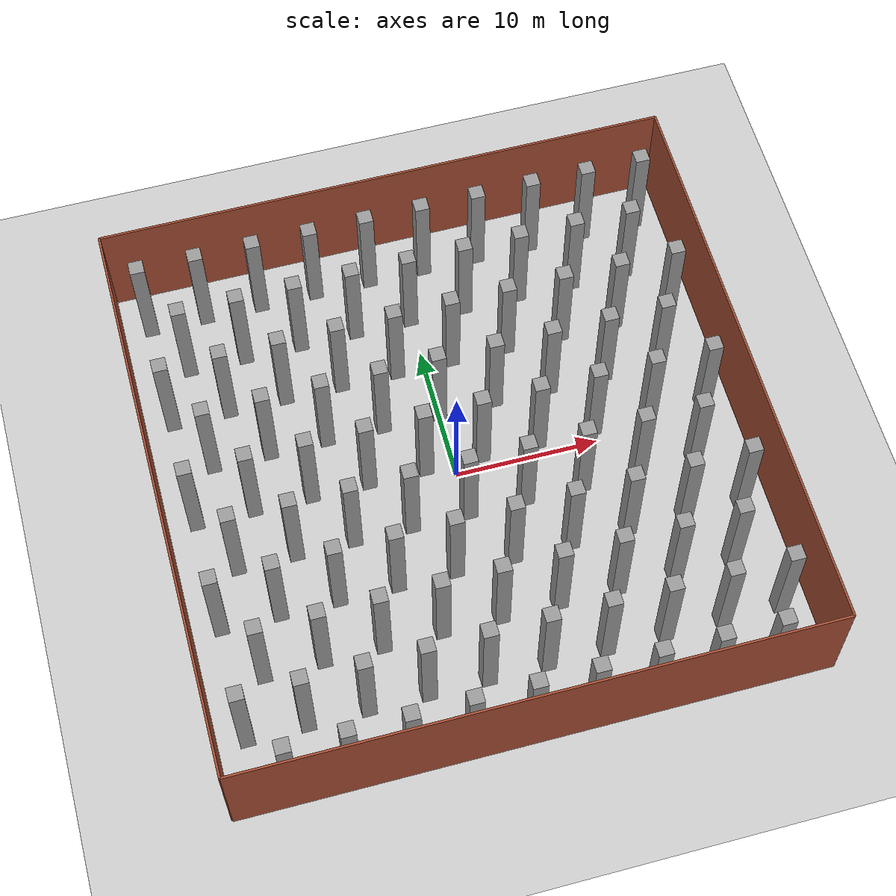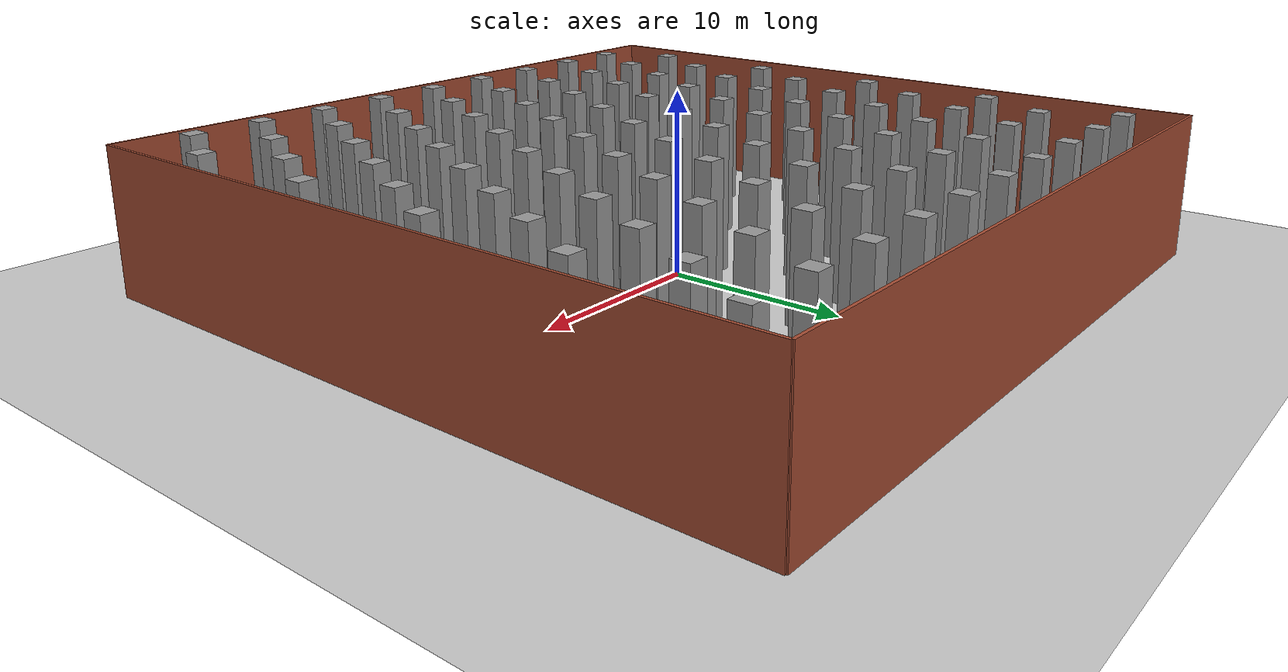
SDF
<sdf version="1.7">
 <world name="default">
  <light name="sun" type="directional">
   <pose>0 0 10 0 -0 0</pose>
   <diffuse>0.8 0.8 0.8 1</diffuse>
   <specular>0.2 0.2 0.2 1</specular>
   <attenuation>
    <range>1000</range>
    <constant>0.9</constant>
    <linear>0.01</linear>
    <quadratic>0.001</quadratic>
   </attenuation>
   <direction>-0.5 0.1 -0.9</direction>
   <spot><inner_angle>0</inner_angle><outer_angle>0</outer_angle><falloff>0</falloff></spot>
  </light>
  <model name="ground_plane">
   <static>1</static>
   <link name="link">
    <collision name="collision">
     <geometry><plane><normal>0 0 1</normal><size>100 100</size></plane></geometry>
     <surface>
      <contact><collide_bitmask>65535</collide_bitmask></contact>
      <friction><ode><mu>100</mu><mu2>50</mu2></ode></friction>
     </surface>
    </collision>
    <visual name="visual">
     <cast_shadows>0</cast_shadows>
     <geometry><plane><normal>0 0 1</normal><size>100 100</size></plane></geometry>
     <material>
      <script><uri>file://media/materials/scripts/gazebo.material</uri><name>Gazebo/Grey</name></script>
     </material>
    </visual>
   </link>
  </model>
  <gravity>0 0 -9.8</gravity>
  <magnetic_field>6e-06 2.3e-05 -4.2e-05</magnetic_field>
  <atmosphere type="adiabatic"/>
  <physics type="ode">
   <max_step_size>0.001</max_step_size>
   <real_time_factor>1</real_time_factor>
   <real_time_update_rate>1000</real_time_update_rate>
  </physics>
  <scene><ambient>0.4 0.4 0.4 1</ambient><background>0.7 0.7 0.7 1</background><shadows>1</shadows></scene>
  <spherical_coordinates>
   <surface_model>EARTH_WGS84</surface_model>
   <latitude_deg>0</latitude_deg>
   <longitude_deg>0</longitude_deg>
   <elevation>0</elevation>
   <heading_deg>0</heading_deg>
  </spherical_coordinates>
  <model name="sim_room_square">
   <link name="Wall_14">
    <collision name="Wall_14_Collision">
     <geometry><box><size>40 0.15 8</size></box></geometry>
     <pose>0 0 4 0 -0 0</pose>
    </collision>
    <visual name="Wall_14_Visual">
     <pose>0 0 4 0 -0 0</pose>
     <geometry><box><size>40 0.15 8</size></box></geometry>
     <material>
      <script><uri>file://media/materials/scripts/gazebo.material</uri><name>Gazebo/Bricks</name></script>
      <ambient>1 1 1 1</ambient>
     </material>
     <meta><layer>0</layer></meta>
    </visual>
    <pose>20 -0 0 0 -0 -1.5708</pose>
   </link>
   <link name="Wall_15">
    <collision name="Wall_15_Collision">
     <geometry><box><size>40 0.15 8</size></box></geometry>
     <pose>0 0 4 0 -0 0</pose>
    </collision>
    <visual name="Wall_15_Visual">
     <pose>0 0 4 0 -0 0</pose>
     <geometry><box><size>40 0.15 8</size></box></geometry>
     <material>
      <script><uri>file://media/materials/scripts/gazebo.material</uri><name>Gazebo/Bricks</name></script>
      <ambient>1 1 1 1</ambient>
     </material>
     <meta><layer>0</layer></meta>
    </visual>
    <pose>0 -20 0 0 -0 3.14159</pose>
   </link>
   <link name="Wall_16">
    <collision name="Wall_16_Collision">
     <geometry><box><size>40 0.15 8</size></box></geometry>
     <pose>0 0 4 0 -0 0</pose>
    </collision>
    <visual name="Wall_16_Visual">
     <pose>0 0 4 0 -0 0</pose>
     <geometry><box><size>40 0.15 8</size></box></geometry>
     <material>
      <script><uri>file://media/materials/scripts/gazebo.material</uri><name>Gazebo/Bricks</name></script>
      <ambient>1 1 1 1</ambient>
     </material>
     <meta><layer>0</layer></meta>
    </visual>
    <pose>-20 -0 0 0 -0 1.5708</pose>
   </link>
   <link name="Wall_19">
    <collision name="Wall_19_Collision">
     <geometry><box><size>40 0.15 8</size></box></geometry>
     <pose>0 0 4 0 -0 0</pose>
    </collision>
    <visual name="Wall_19_Visual">
     <pose>0 0 4 0 -0 0</pose>
     <geometry><box><size>40 0.15 8</size></box></geometry>
     <material>
      <script><uri>file://media/materials/scripts/gazebo.material</uri><name>Gazebo/Bricks</name></script>
      <ambient>1 1 1 1</ambient>
     </material>
     <meta><layer>0</layer></meta>
    </visual>
    <pose>0 20 0 0 -0 0</pose>
   </link>
   <static>1</static>
  </model>
  <model name="unit_box_static1">
   <link name="link">
    <inertial>
     <mass>1</mass>
     <inertia>
      <ixx>0.166667</ixx>
      <ixy>0</ixy>
      <ixz>0</ixz>
      <iyy>0.166667</iyy>
      <iyz>0</iyz>
      <izz>0.166667</izz>
     </inertia>
    </inertial>
    <visual name="visual">
     <geometry><box><size>1 1 8</size></box></geometry>
     <material>
      <script><name>Gazebo/Grey</name><uri>file://media/materials/scripts/gazebo.material</uri></script>
      <shader type="pixel"/>
     </material>
    </visual>
    <collision name="collision">
     <geometry><box><size>1 1 8</size></box></geometry>
     <surface>
      <friction>
       <ode><mu>1</mu><mu2>1</mu2><fdir1>0 0 0</fdir1><slip1>0</slip1><slip2>0</slip2></ode>
       <torsional>
        <coefficient>1</coefficient>
        <patch_radius>0</patch_radius>
        <surface_radius>0</surface_radius>
        <use_patch_radius>1</use_patch_radius>
        <ode><slip>0</slip></ode>
       </torsional>
      </friction>
      <bounce><restitution_coefficient>0</restitution_coefficient><threshold>1e+06</threshold></bounce>
      <contact>
       <collide_without_contact>0</collide_without_contact>
       <collide_without_contact_bitmask>1</collide_without_contact_bitmask>
       <collide_bitmask>1</collide_bitmask>
       <ode>
        <soft_cfm>0</soft_cfm>
        <soft_erp>0.2</soft_erp>
        <kp>1e+13</kp>
        <kd>1</kd>
        <max_vel>0.01</max_vel>
        <min_depth>0</min_depth>
       </ode>
       <bullet>
        <split_impulse>1</split_impulse>
        <split_impulse_penetration_threshold>-0.01</split_impulse_penetration_threshold>
        <soft_cfm>0</soft_cfm>
        <soft_erp>0.2</soft_erp>
        <kp>1e+13</kp>
        <kd>1</kd>
       </bullet>
      </contact>
     </surface>
    </collision>
   </link>
   <static>1</static>
   <pose>-16 -19 4 0 -0 0</pose>
  </model>
  <model name="unit_box_static2">
   <link name="link">
    <inertial>
     <mass>1</mass>
     <inertia>
      <ixx>0.166667</ixx>
      <ixy>0</ixy>
      <ixz>0</ixz>
      <iyy>0.166667</iyy>
      <iyz>0</iyz>
      <izz>0.166667</izz>
     </inertia>
    </inertial>
    <visual name="visual">
     <geometry><box><size>1 1 8</size></box></geometry>
     <material>
      <script><name>Gazebo/Grey</name><uri>file://media/materials/scripts/gazebo.material</uri></script>
      <shader type="pixel"/>
     </material>
    </visual>
    <collision name="collision">
     <geometry><box><size>1 1 8</size></box></geometry>
     <surface>
      <friction>
       <ode><mu>1</mu><mu2>1</mu2><fdir1>0 0 0</fdir1><slip1>0</slip1><slip2>0</slip2></ode>
       <torsional>
        <coefficient>1</coefficient>
        <patch_radius>0</patch_radius>
        <surface_radius>0</surface_radius>
        <use_patch_radius>1</use_patch_radius>
        <ode><slip>0</slip></ode>
       </torsional>
      </friction>
      <bounce><restitution_coefficient>0</restitution_coefficient><threshold>1e+06</threshold></bounce>
      <contact>
       <collide_without_contact>0</collide_without_contact>
       <collide_without_contact_bitmask>1</collide_without_contact_bitmask>
       <collide_bitmask>1</collide_bitmask>
       <ode>
        <soft_cfm>0</soft_cfm>
        <soft_erp>0.2</soft_erp>
        <kp>1e+13</kp>
        <kd>1</kd>
        <max_vel>0.01</max_vel>
        <min_depth>0</min_depth>
       </ode>
       <bullet>
        <split_impulse>1</split_impulse>
        <split_impulse_penetration_threshold>-0.01</split_impulse_penetration_threshold>
        <soft_cfm>0</soft_cfm>
        <soft_erp>0.2</soft_erp>
        <kp>1e+13</kp>
        <kd>1</kd>
       </bullet>
      </contact>
     </surface>
    </collision>
   </link>
   <static>1</static>
   <pose>-12 -19 4 0 -0 0</pose>
  </model>
  <model name="unit_box_static3">
   <link name="link">
    <inertial>
     <mass>1</mass>
     <inertia>
      <ixx>0.166667</ixx>
      <ixy>0</ixy>
      <ixz>0</ixz>
      <iyy>0.166667</iyy>
      <iyz>0</iyz>
      <izz>0.166667</izz>
     </inertia>
    </inertial>
    <visual name="visual">
     <geometry><box><size>1 1 8</size></box></geometry>
     <material>
      <script><name>Gazebo/Grey</name><uri>file://media/materials/scripts/gazebo.material</uri></script>
      <shader type="pixel"/>
     </material>
    </visual>
    <collision name="collision">
     <geometry><box><size>1 1 8</size></box></geometry>
     <surface>
      <friction>
       <ode><mu>1</mu><mu2>1</mu2><fdir1>0 0 0</fdir1><slip1>0</slip1><slip2>0</slip2></ode>
       <torsional>
        <coefficient>1</coefficient>
        <patch_radius>0</patch_radius>
        <surface_radius>0</surface_radius>
        <use_patch_radius>1</use_patch_radius>
        <ode><slip>0</slip></ode>
       </torsional>
      </friction>
      <bounce><restitution_coefficient>0</restitution_coefficient><threshold>1e+06</threshold></bounce>
      <contact>
       <collide_without_contact>0</collide_without_contact>
       <collide_without_contact_bitmask>1</collide_without_contact_bitmask>
       <collide_bitmask>1</collide_bitmask>
       <ode>
        <soft_cfm>0</soft_cfm>
        <soft_erp>0.2</soft_erp>
        <kp>1e+13</kp>
        <kd>1</kd>
        <max_vel>0.01</max_vel>
        <min_depth>0</min_depth>
       </ode>
       <bullet>
        <split_impulse>1</split_impulse>
        <split_impulse_penetration_threshold>-0.01</split_impulse_penetration_threshold>
        <soft_cfm>0</soft_cfm>
        <soft_erp>0.2</soft_erp>
        <kp>1e+13</kp>
        <kd>1</kd>
       </bullet>
      </contact>
     </surface>
    </collision>
   </link>
   <static>1</static>
   <pose>-8 -19 4 0 -0 0</pose>
  </model>
  <model name="unit_box_static4">
   <link name="link">
    <inertial>
     <mass>1</mass>
     <inertia>
      <ixx>0.166667</ixx>
      <ixy>0</ixy>
      <ixz>0</ixz>
      <iyy>0.166667</iyy>
      <iyz>0</iyz>
      <izz>0.166667</izz>
     </inertia>
    </inertial>
    <visual name="visual">
     <geometry><box><size>1 1 8</size></box></geometry>
     <material>
      <script><name>Gazebo/Grey</name><uri>file://media/materials/scripts/gazebo.material</uri></script>
      <shader type="pixel"/>
     </material>
    </visual>
    <collision name="collision">
     <geometry><box><size>1 1 8</size></box></geometry>
     <surface>
      <friction>
       <ode><mu>1</mu><mu2>1</mu2><fdir1>0 0 0</fdir1><slip1>0</slip1><slip2>0</slip2></ode>
       <torsional>
        <coefficient>1</coefficient>
        <patch_radius>0</patch_radius>
        <surface_radius>0</surface_radius>
        <use_patch_radius>1</use_patch_radius>
        <ode><slip>0</slip></ode>
       </torsional>
      </friction>
      <bounce><restitution_coefficient>0</restitution_coefficient><threshold>1e+06</threshold></bounce>
      <contact>
       <collide_without_contact>0</collide_without_contact>
       <collide_without_contact_bitmask>1</collide_without_contact_bitmask>
       <collide_bitmask>1</collide_bitmask>
       <ode>
        <soft_cfm>0</soft_cfm>
        <soft_erp>0.2</soft_erp>
        <kp>1e+13</kp>
        <kd>1</kd>
        <max_vel>0.01</max_vel>
        <min_depth>0</min_depth>
       </ode>
       <bullet>
        <split_impulse>1</split_impulse>
        <split_impulse_penetration_threshold>-0.01</split_impulse_penetration_threshold>
        <soft_cfm>0</soft_cfm>
        <soft_erp>0.2</soft_erp>
        <kp>1e+13</kp>
        <kd>1</kd>
       </bullet>
      </contact>
     </surface>
    </collision>
   </link>
   <static>1</static>
   <pose>-4 -19 4 0 -0 0</pose>
  </model>
  <model name="unit_box_static5">
   <link name="link">
    <inertial>
     <mass>1</mass>
     <inertia>
      <ixx>0.166667</ixx>
      <ixy>0</ixy>
      <ixz>0</ixz>
      <iyy>0.166667</iyy>
      <iyz>0</iyz>
      <izz>0.166667</izz>
     </inertia>
    </inertial>
    <visual name="visual">
     <geometry><box><size>1 1 8</size></box></geometry>
     <material>
      <script><name>Gazebo/Grey</name><uri>file://media/materials/scripts/gazebo.material</uri></script>
      <shader type="pixel"/>
     </material>
    </visual>
    <collision name="collision">
     <geometry><box><size>1 1 8</size></box></geometry>
     <surface>
      <friction>
       <ode><mu>1</mu><mu2>1</mu2><fdir1>0 0 0</fdir1><slip1>0</slip1><slip2>0</slip2></ode>
       <torsional>
        <coefficient>1</coefficient>
        <patch_radius>0</patch_radius>
        <surface_radius>0</surface_radius>
        <use_patch_radius>1</use_patch_radius>
        <ode><slip>0</slip></ode>
       </torsional>
      </friction>
      <bounce><restitution_coefficient>0</restitution_coefficient><threshold>1e+06</threshold></bounce>
      <contact>
       <collide_without_contact>0</collide_without_contact>
       <collide_without_contact_bitmask>1</collide_without_contact_bitmask>
       <collide_bitmask>1</collide_bitmask>
       <ode>
        <soft_cfm>0</soft_cfm>
        <soft_erp>0.2</soft_erp>
        <kp>1e+13</kp>
        <kd>1</kd>
        <max_vel>0.01</max_vel>
        <min_depth>0</min_depth>
       </ode>
       <bullet>
        <split_impulse>1</split_impulse>
        <split_impulse_penetration_threshold>-0.01</split_impulse_penetration_threshold>
        <soft_cfm>0</soft_cfm>
        <soft_erp>0.2</soft_erp>
        <kp>1e+13</kp>
        <kd>1</kd>
       </bullet>
      </contact>
     </surface>
    </collision>
   </link>
   <static>1</static>
   <pose>0 -19 4 0 -0 0</pose>
  </model>
  <model name="unit_box_static6">
   <link name="link">
    <inertial>
     <mass>1</mass>
     <inertia>
      <ixx>0.166667</ixx>
      <ixy>0</ixy>
      <ixz>0</ixz>
      <iyy>0.166667</iyy>
      <iyz>0</iyz>
      <izz>0.166667</izz>
     </inertia>
    </inertial>
    <visual name="visual">
     <geometry><box><size>1 1 8</size></box></geometry>
     <material>
      <script><name>Gazebo/Grey</name><uri>file://media/materials/scripts/gazebo.material</uri></script>
      <shader type="pixel"/>
     </material>
    </visual>
    <collision name="collision">
     <geometry><box><size>1 1 8</size></box></geometry>
     <surface>
      <friction>
       <ode><mu>1</mu><mu2>1</mu2><fdir1>0 0 0</fdir1><slip1>0</slip1><slip2>0</slip2></ode>
       <torsional>
        <coefficient>1</coefficient>
        <patch_radius>0</patch_radius>
        <surface_radius>0</surface_radius>
        <use_patch_radius>1</use_patch_radius>
        <ode><slip>0</slip></ode>
       </torsional>
      </friction>
      <bounce><restitution_coefficient>0</restitution_coefficient><threshold>1e+06</threshold></bounce>
      <contact>
       <collide_without_contact>0</collide_without_contact>
       <collide_without_contact_bitmask>1</collide_without_contact_bitmask>
       <collide_bitmask>1</collide_bitmask>
       <ode>
        <soft_cfm>0</soft_cfm>
        <soft_erp>0.2</soft_erp>
        <kp>1e+13</kp>
        <kd>1</kd>
        <max_vel>0.01</max_vel>
        <min_depth>0</min_depth>
       </ode>
       <bullet>
        <split_impulse>1</split_impulse>
        <split_impulse_penetration_threshold>-0.01</split_impulse_penetration_threshold>
        <soft_cfm>0</soft_cfm>
        <soft_erp>0.2</soft_erp>
        <kp>1e+13</kp>
        <kd>1</kd>
       </bullet>
      </contact>
     </surface>
    </collision>
   </link>
   <static>1</static>
   <pose>4 -19 4 0 -0 0</pose>
  </model>
  <model name="unit_box_static7">
   <link name="link">
    <inertial>
     <mass>1</mass>
     <inertia>
      <ixx>0.166667</ixx>
      <ixy>0</ixy>
      <ixz>0</ixz>
      <iyy>0.166667</iyy>
      <iyz>0</iyz>
      <izz>0.166667</izz>
     </inertia>
    </inertial>
    <visual name="visual">
     <geometry><box><size>1 1 8</size></box></geometry>
     <material>
      <script><name>Gazebo/Grey</name><uri>file://media/materials/scripts/gazebo.material</uri></script>
      <shader type="pixel"/>
     </material>
    </visual>
    <collision name="collision">
     <geometry><box><size>1 1 8</size></box></geometry>
     <surface>
      <friction>
       <ode><mu>1</mu><mu2>1</mu2><fdir1>0 0 0</fdir1><slip1>0</slip1><slip2>0</slip2></ode>
       <torsional>
        <coefficient>1</coefficient>
        <patch_radius>0</patch_radius>
        <surface_radius>0</surface_radius>
        <use_patch_radius>1</use_patch_radius>
        <ode><slip>0</slip></ode>
       </torsional>
      </friction>
      <bounce><restitution_coefficient>0</restitution_coefficient><threshold>1e+06</threshold></bounce>
      <contact>
       <collide_without_contact>0</collide_without_contact>
       <collide_without_contact_bitmask>1</collide_without_contact_bitmask>
       <collide_bitmask>1</collide_bitmask>
       <ode>
        <soft_cfm>0</soft_cfm>
        <soft_erp>0.2</soft_erp>
        <kp>1e+13</kp>
        <kd>1</kd>
        <max_vel>0.01</max_vel>
        <min_depth>0</min_depth>
       </ode>
       <bullet>
        <split_impulse>1</split_impulse>
        <split_impulse_penetration_threshold>-0.01</split_impulse_penetration_threshold>
        <soft_cfm>0</soft_cfm>
        <soft_erp>0.2</soft_erp>
        <kp>1e+13</kp>
        <kd>1</kd>
       </bullet>
      </contact>
     </surface>
    </collision>
   </link>
   <static>1</static>
   <pose>8 -19 4 0 -0 0</pose>
  </model>
  <model name="unit_box_static8">
   <link name="link">
    <inertial>
     <mass>1</mass>
     <inertia>
      <ixx>0.166667</ixx>
      <ixy>0</ixy>
      <ixz>0</ixz>
      <iyy>0.166667</iyy>
      <iyz>0</iyz>
      <izz>0.166667</izz>
     </inertia>
    </inertial>
    <visual name="visual">
     <geometry><box><size>1 1 8</size></box></geometry>
     <material>
      <script><name>Gazebo/Grey</name><uri>file://media/materials/scripts/gazebo.material</uri></script>
      <shader type="pixel"/>
     </material>
    </visual>
    <collision name="collision">
     <geometry><box><size>1 1 8</size></box></geometry>
     <surface>
      <friction>
       <ode><mu>1</mu><mu2>1</mu2><fdir1>0 0 0</fdir1><slip1>0</slip1><slip2>0</slip2></ode>
       <torsional>
        <coefficient>1</coefficient>
        <patch_radius>0</patch_radius>
        <surface_radius>0</surface_radius>
        <use_patch_radius>1</use_patch_radius>
        <ode><slip>0</slip></ode>
       </torsional>
      </friction>
      <bounce><restitution_coefficient>0</restitution_coefficient><threshold>1e+06</threshold></bounce>
      <contact>
       <collide_without_contact>0</collide_without_contact>
       <collide_without_contact_bitmask>1</collide_without_contact_bitmask>
       <collide_bitmask>1</collide_bitmask>
       <ode>
        <soft_cfm>0</soft_cfm>
        <soft_erp>0.2</soft_erp>
        <kp>1e+13</kp>
        <kd>1</kd>
        <max_vel>0.01</max_vel>
        <min_depth>0</min_depth>
       </ode>
       <bullet>
        <split_impulse>1</split_impulse>
        <split_impulse_penetration_threshold>-0.01</split_impulse_penetration_threshold>
        <soft_cfm>0</soft_cfm>
        <soft_erp>0.2</soft_erp>
        <kp>1e+13</kp>
        <kd>1</kd>
       </bullet>
      </contact>
     </surface>
    </collision>
   </link>
   <static>1</static>
   <pose>12 -19 4 0 -0 0</pose>
  </model>
  <model name="unit_box_static9">
   <link name="link">
    <inertial>
     <mass>1</mass>
     <inertia>
      <ixx>0.166667</ixx>
      <ixy>0</ixy>
      <ixz>0</ixz>
      <iyy>0.166667</iyy>
      <iyz>0</iyz>
      <izz>0.166667</izz>
     </inertia>
    </inertial>
    <visual name="visual">
     <geometry><box><size>1 1 8</size></box></geometry>
     <material>
      <script><name>Gazebo/Grey</name><uri>file://media/materials/scripts/gazebo.material</uri></script>
      <shader type="pixel"/>
     </material>
    </visual>
    <collision name="collision">
     <geometry><box><size>1 1 8</size></box></geometry>
     <surface>
      <friction>
       <ode><mu>1</mu><mu2>1</mu2><fdir1>0 0 0</fdir1><slip1>0</slip1><slip2>0</slip2></ode>
       <torsional>
        <coefficient>1</coefficient>
        <patch_radius>0</patch_radius>
        <surface_radius>0</surface_radius>
        <use_patch_radius>1</use_patch_radius>
        <ode><slip>0</slip></ode>
       </torsional>
      </friction>
      <bounce><restitution_coefficient>0</restitution_coefficient><threshold>1e+06</threshold></bounce>
      <contact>
       <collide_without_contact>0</collide_without_contact>
       <collide_without_contact_bitmask>1</collide_without_contact_bitmask>
       <collide_bitmask>1</collide_bitmask>
       <ode>
        <soft_cfm>0</soft_cfm>
        <soft_erp>0.2</soft_erp>
        <kp>1e+13</kp>
        <kd>1</kd>
        <max_vel>0.01</max_vel>
        <min_depth>0</min_depth>
       </ode>
       <bullet>
        <split_impulse>1</split_impulse>
        <split_impulse_penetration_threshold>-0.01</split_impulse_penetration_threshold>
        <soft_cfm>0</soft_cfm>
        <soft_erp>0.2</soft_erp>
        <kp>1e+13</kp>
        <kd>1</kd>
       </bullet>
      </contact>
     </surface>
    </collision>
   </link>
   <static>1</static>
   <pose>16 -19 4 0 -0 0</pose>
  </model>
  <model name="unit_box_static10">
   <link name="link">
    <inertial>
     <mass>1</mass>
     <inertia>
      <ixx>0.166667</ixx>
      <ixy>0</ixy>
      <ixz>0</ixz>
      <iyy>0.166667</iyy>
      <iyz>0</iyz>
      <izz>0.166667</izz>
     </inertia>
    </inertial>
    <visual name="visual">
     <geometry><box><size>1 1 8</size></box></geometry>
     <material>
      <script><name>Gazebo/Grey</name><uri>file://media/materials/scripts/gazebo.material</uri></script>
      <shader type="pixel"/>
     </material>
    </visual>
    <collision name="collision">
     <geometry><box><size>1 1 8</size></box></geometry>
     <surface>
      <friction>
       <ode><mu>1</mu><mu2>1</mu2><fdir1>0 0 0</fdir1><slip1>0</slip1><slip2>0</slip2></ode>
       <torsional>
        <coefficient>1</coefficient>
        <patch_radius>0</patch_radius>
        <surface_radius>0</surface_radius>
        <use_patch_radius>1</use_patch_radius>
        <ode><slip>0</slip></ode>
       </torsional>
      </friction>
      <bounce><restitution_coefficient>0</restitution_coefficient><threshold>1e+06</threshold></bounce>
      <contact>
       <collide_without_contact>0</collide_without_contact>
       <collide_without_contact_bitmask>1</collide_without_contact_bitmask>
       <collide_bitmask>1</collide_bitmask>
       <ode>
        <soft_cfm>0</soft_cfm>
        <soft_erp>0.2</soft_erp>
        <kp>1e+13</kp>
        <kd>1</kd>
        <max_vel>0.01</max_vel>
        <min_depth>0</min_depth>
       </ode>
       <bullet>
        <split_impulse>1</split_impulse>
        <split_impulse_penetration_threshold>-0.01</split_impulse_penetration_threshold>
        <soft_cfm>0</soft_cfm>
        <soft_erp>0.2</soft_erp>
        <kp>1e+13</kp>
        <kd>1</kd>
       </bullet>
      </contact>
     </surface>
    </collision>
   </link>
   <static>1</static>
   <pose>-18 -15 4 0 -0 0</pose>
  </model>
  <model name="unit_box_static11">
   <link name="link">
    <inertial>
     <mass>1</mass>
     <inertia>
      <ixx>0.166667</ixx>
      <ixy>0</ixy>
      <ixz>0</ixz>
      <iyy>0.166667</iyy>
      <iyz>0</iyz>
      <izz>0.166667</izz>
     </inertia>
    </inertial>
    <visual name="visual">
     <geometry><box><size>1 1 8</size></box></geometry>
     <material>
      <script><name>Gazebo/Grey</name><uri>file://media/materials/scripts/gazebo.material</uri></script>
      <shader type="pixel"/>
     </material>
    </visual>
    <collision name="collision">
     <geometry><box><size>1 1 8</size></box></geometry>
     <surface>
      <friction>
       <ode><mu>1</mu><mu2>1</mu2><fdir1>0 0 0</fdir1><slip1>0</slip1><slip2>0</slip2></ode>
       <torsional>
        <coefficient>1</coefficient>
        <patch_radius>0</patch_radius>
        <surface_radius>0</surface_radius>
        <use_patch_radius>1</use_patch_radius>
        <ode><slip>0</slip></ode>
       </torsional>
      </friction>
      <bounce><restitution_coefficient>0</restitution_coefficient><threshold>1e+06</threshold></bounce>
      <contact>
       <collide_without_contact>0</collide_without_contact>
       <collide_without_contact_bitmask>1</collide_without_contact_bitmask>
       <collide_bitmask>1</collide_bitmask>
       <ode>
        <soft_cfm>0</soft_cfm>
        <soft_erp>0.2</soft_erp>
        <kp>1e+13</kp>
        <kd>1</kd>
        <max_vel>0.01</max_vel>
        <min_depth>0</min_depth>
       </ode>
       <bullet>
        <split_impulse>1</split_impulse>
        <split_impulse_penetration_threshold>-0.01</split_impulse_penetration_threshold>
        <soft_cfm>0</soft_cfm>
        <soft_erp>0.2</soft_erp>
        <kp>1e+13</kp>
        <kd>1</kd>
       </bullet>
      </contact>
     </surface>
    </collision>
   </link>
   <static>1</static>
   <pose>-14 -15 4 0 -0 0</pose>
  </model>
  <model name="unit_box_static12">
   <link name="link">
    <inertial>
     <mass>1</mass>
     <inertia>
      <ixx>0.166667</ixx>
      <ixy>0</ixy>
      <ixz>0</ixz>
      <iyy>0.166667</iyy>
      <iyz>0</iyz>
      <izz>0.166667</izz>
     </inertia>
    </inertial>
    <visual name="visual">
     <geometry><box><size>1 1 8</size></box></geometry>
     <material>
      <script><name>Gazebo/Grey</name><uri>file://media/materials/scripts/gazebo.material</uri></script>
      <shader type="pixel"/>
     </material>
    </visual>
    <collision name="collision">
     <geometry><box><size>1 1 8</size></box></geometry>
     <surface>
      <friction>
       <ode><mu>1</mu><mu2>1</mu2><fdir1>0 0 0</fdir1><slip1>0</slip1><slip2>0</slip2></ode>
       <torsional>
        <coefficient>1</coefficient>
        <patch_radius>0</patch_radius>
        <surface_radius>0</surface_radius>
        <use_patch_radius>1</use_patch_radius>
        <ode><slip>0</slip></ode>
       </torsional>
      </friction>
      <bounce><restitution_coefficient>0</restitution_coefficient><threshold>1e+06</threshold></bounce>
      <contact>
       <collide_without_contact>0</collide_without_contact>
       <collide_without_contact_bitmask>1</collide_without_contact_bitmask>
       <collide_bitmask>1</collide_bitmask>
       <ode>
        <soft_cfm>0</soft_cfm>
        <soft_erp>0.2</soft_erp>
        <kp>1e+13</kp>
        <kd>1</kd>
        <max_vel>0.01</max_vel>
        <min_depth>0</min_depth>
       </ode>
       <bullet>
        <split_impulse>1</split_impulse>
        <split_impulse_penetration_threshold>-0.01</split_impulse_penetration_threshold>
        <soft_cfm>0</soft_cfm>
        <soft_erp>0.2</soft_erp>
        <kp>1e+13</kp>
        <kd>1</kd>
       </bullet>
      </contact>
     </surface>
    </collision>
   </link>
   <static>1</static>
   <pose>-10 -15 4 0 -0 0</pose>
  </model>
  <model name="unit_box_static13">
   <link name="link">
    <inertial>
     <mass>1</mass>
     <inertia>
      <ixx>0.166667</ixx>
      <ixy>0</ixy>
      <ixz>0</ixz>
      <iyy>0.166667</iyy>
      <iyz>0</iyz>
      <izz>0.166667</izz>
     </inertia>
    </inertial>
    <visual name="visual">
     <geometry><box><size>1 1 8</size></box></geometry>
     <material>
      <script><name>Gazebo/Grey</name><uri>file://media/materials/scripts/gazebo.material</uri></script>
      <shader type="pixel"/>
     </material>
    </visual>
    <collision name="collision">
     <geometry><box><size>1 1 8</size></box></geometry>
     <surface>
      <friction>
       <ode><mu>1</mu><mu2>1</mu2><fdir1>0 0 0</fdir1><slip1>0</slip1><slip2>0</slip2></ode>
       <torsional>
        <coefficient>1</coefficient>
        <patch_radius>0</patch_radius>
        <surface_radius>0</surface_radius>
        <use_patch_radius>1</use_patch_radius>
        <ode><slip>0</slip></ode>
       </torsional>
      </friction>
      <bounce><restitution_coefficient>0</restitution_coefficient><threshold>1e+06</threshold></bounce>
      <contact>
       <collide_without_contact>0</collide_without_contact>
       <collide_without_contact_bitmask>1</collide_without_contact_bitmask>
       <collide_bitmask>1</collide_bitmask>
       <ode>
        <soft_cfm>0</soft_cfm>
        <soft_erp>0.2</soft_erp>
        <kp>1e+13</kp>
        <kd>1</kd>
        <max_vel>0.01</max_vel>
        <min_depth>0</min_depth>
       </ode>
       <bullet>
        <split_impulse>1</split_impulse>
        <split_impulse_penetration_threshold>-0.01</split_impulse_penetration_threshold>
        <soft_cfm>0</soft_cfm>
        <soft_erp>0.2</soft_erp>
        <kp>1e+13</kp>
        <kd>1</kd>
       </bullet>
      </contact>
     </surface>
    </collision>
   </link>
   <static>1</static>
   <pose>-6 -15 4 0 -0 0</pose>
  </model>
  <model name="unit_box_static14">
   <link name="link">
    <inertial>
     <mass>1</mass>
     <inertia>
      <ixx>0.166667</ixx>
      <ixy>0</ixy>
      <ixz>0</ixz>
      <iyy>0.166667</iyy>
      <iyz>0</iyz>
      <izz>0.166667</izz>
     </inertia>
    </inertial>
    <visual name="visual">
     <geometry><box><size>1 1 8</size></box></geometry>
     <material>
      <script><name>Gazebo/Grey</name><uri>file://media/materials/scripts/gazebo.material</uri></script>
      <shader type="pixel"/>
     </material>
    </visual>
    <collision name="collision">
     <geometry><box><size>1 1 8</size></box></geometry>
     <surface>
      <friction>
       <ode><mu>1</mu><mu2>1</mu2><fdir1>0 0 0</fdir1><slip1>0</slip1><slip2>0</slip2></ode>
       <torsional>
        <coefficient>1</coefficient>
        <patch_radius>0</patch_radius>
        <surface_radius>0</surface_radius>
        <use_patch_radius>1</use_patch_radius>
        <ode><slip>0</slip></ode>
       </torsional>
      </friction>
      <bounce><restitution_coefficient>0</restitution_coefficient><threshold>1e+06</threshold></bounce>
      <contact>
       <collide_without_contact>0</collide_without_contact>
       <collide_without_contact_bitmask>1</collide_without_contact_bitmask>
       <collide_bitmask>1</collide_bitmask>
       <ode>
        <soft_cfm>0</soft_cfm>
        <soft_erp>0.2</soft_erp>
        <kp>1e+13</kp>
        <kd>1</kd>
        <max_vel>0.01</max_vel>
        <min_depth>0</min_depth>
       </ode>
       <bullet>
        <split_impulse>1</split_impulse>
        <split_impulse_penetration_threshold>-0.01</split_impulse_penetration_threshold>
        <soft_cfm>0</soft_cfm>
        <soft_erp>0.2</soft_erp>
        <kp>1e+13</kp>
        <kd>1</kd>
       </bullet>
      </contact>
     </surface>
    </collision>
   </link>
   <static>1</static>
   <pose>-2 -15 4 0 -0 0</pose>
  </model>
  <model name="unit_box_static15">
   <link name="link">
    <inertial>
     <mass>1</mass>
     <inertia>
      <ixx>0.166667</ixx>
      <ixy>0</ixy>
      <ixz>0</ixz>
      <iyy>0.166667</iyy>
      <iyz>0</iyz>
      <izz>0.166667</izz>
     </inertia>
    </inertial>
    <visual name="visual">
     <geometry><box><size>1 1 8</size></box></geometry>
     <material>
      <script><name>Gazebo/Grey</name><uri>file://media/materials/scripts/gazebo.material</uri></script>
      <shader type="pixel"/>
     </material>
    </visual>
    <collision name="collision">
     <geometry><box><size>1 1 8</size></box></geometry>
     <surface>
      <friction>
       <ode><mu>1</mu><mu2>1</mu2><fdir1>0 0 0</fdir1><slip1>0</slip1><slip2>0</slip2></ode>
       <torsional>
        <coefficient>1</coefficient>
        <patch_radius>0</patch_radius>
        <surface_radius>0</surface_radius>
        <use_patch_radius>1</use_patch_radius>
        <ode><slip>0</slip></ode>
       </torsional>
      </friction>
      <bounce><restitution_coefficient>0</restitution_coefficient><threshold>1e+06</threshold></bounce>
      <contact>
       <collide_without_contact>0</collide_without_contact>
       <collide_without_contact_bitmask>1</collide_without_contact_bitmask>
       <collide_bitmask>1</collide_bitmask>
       <ode>
        <soft_cfm>0</soft_cfm>
        <soft_erp>0.2</soft_erp>
        <kp>1e+13</kp>
        <kd>1</kd>
        <max_vel>0.01</max_vel>
        <min_depth>0</min_depth>
       </ode>
       <bullet>
        <split_impulse>1</split_impulse>
        <split_impulse_penetration_threshold>-0.01</split_impulse_penetration_threshold>
        <soft_cfm>0</soft_cfm>
        <soft_erp>0.2</soft_erp>
        <kp>1e+13</kp>
        <kd>1</kd>
       </bullet>
      </contact>
     </surface>
    </collision>
   </link>
   <static>1</static>
   <pose>2 -15 4 0 -0 0</pose>
  </model>
  <model name="unit_box_static16">
   <link name="link">
    <inertial>
     <mass>1</mass>
     <inertia>
      <ixx>0.166667</ixx>
      <ixy>0</ixy>
      <ixz>0</ixz>
      <iyy>0.166667</iyy>
      <iyz>0</iyz>
      <izz>0.166667</izz>
     </inertia>
    </inertial>
    <visual name="visual">
     <geometry><box><size>1 1 8</size></box></geometry>
     <material>
      <script><name>Gazebo/Grey</name><uri>file://media/materials/scripts/gazebo.material</uri></script>
      <shader type="pixel"/>
     </material>
    </visual>
    <collision name="collision">
     <geometry><box><size>1 1 8</size></box></geometry>
     <surface>
      <friction>
       <ode><mu>1</mu><mu2>1</mu2><fdir1>0 0 0</fdir1><slip1>0</slip1><slip2>0</slip2></ode>
       <torsional>
        <coefficient>1</coefficient>
        <patch_radius>0</patch_radius>
        <surface_radius>0</surface_radius>
        <use_patch_radius>1</use_patch_radius>
        <ode><slip>0</slip></ode>
       </torsional>
      </friction>
      <bounce><restitution_coefficient>0</restitution_coefficient><threshold>1e+06</threshold></bounce>
      <contact>
       <collide_without_contact>0</collide_without_contact>
       <collide_without_contact_bitmask>1</collide_without_contact_bitmask>
       <collide_bitmask>1</collide_bitmask>
       <ode>
        <soft_cfm>0</soft_cfm>
        <soft_erp>0.2</soft_erp>
        <kp>1e+13</kp>
        <kd>1</kd>
        <max_vel>0.01</max_vel>
        <min_depth>0</min_depth>
       </ode>
       <bullet>
        <split_impulse>1</split_impulse>
        <split_impulse_penetration_threshold>-0.01</split_impulse_penetration_threshold>
        <soft_cfm>0</soft_cfm>
        <soft_erp>0.2</soft_erp>
        <kp>1e+13</kp>
        <kd>1</kd>
       </bullet>
      </contact>
     </surface>
    </collision>
   </link>
   <static>1</static>
   <pose>6 -15 4 0 -0 0</pose>
  </model>
  <model name="unit_box_static17">
   <link name="link">
    <inertial>
     <mass>1</mass>
     <inertia>
      <ixx>0.166667</ixx>
      <ixy>0</ixy>
      <ixz>0</ixz>
      <iyy>0.166667</iyy>
      <iyz>0</iyz>
      <izz>0.166667</izz>
     </inertia>
    </inertial>
    <visual name="visual">
     <geometry><box><size>1 1 8</size></box></geometry>
     <material>
      <script><name>Gazebo/Grey</name><uri>file://media/materials/scripts/gazebo.material</uri></script>
      <shader type="pixel"/>
     </material>
    </visual>
    <collision name="collision">
     <geometry><box><size>1 1 8</size></box></geometry>
     <surface>
      <friction>
       <ode><mu>1</mu><mu2>1</mu2><fdir1>0 0 0</fdir1><slip1>0</slip1><slip2>0</slip2></ode>
       <torsional>
        <coefficient>1</coefficient>
        <patch_radius>0</patch_radius>
        <surface_radius>0</surface_radius>
        <use_patch_radius>1</use_patch_radius>
        <ode><slip>0</slip></ode>
       </torsional>
      </friction>
      <bounce><restitution_coefficient>0</restitution_coefficient><threshold>1e+06</threshold></bounce>
      <contact>
       <collide_without_contact>0</collide_without_contact>
       <collide_without_contact_bitmask>1</collide_without_contact_bitmask>
       <collide_bitmask>1</collide_bitmask>
       <ode>
        <soft_cfm>0</soft_cfm>
        <soft_erp>0.2</soft_erp>
        <kp>1e+13</kp>
        <kd>1</kd>
        <max_vel>0.01</max_vel>
        <min_depth>0</min_depth>
       </ode>
       <bullet>
        <split_impulse>1</split_impulse>
        <split_impulse_penetration_threshold>-0.01</split_impulse_penetration_threshold>
        <soft_cfm>0</soft_cfm>
        <soft_erp>0.2</soft_erp>
        <kp>1e+13</kp>
        <kd>1</kd>
       </bullet>
      </contact>
     </surface>
    </collision>
   </link>
   <static>1</static>
   <pose>10 -15 4 0 -0 0</pose>
  </model>
  <model name="unit_box_static18">
   <link name="link">
    <inertial>
     <mass>1</mass>
     <inertia>
      <ixx>0.166667</ixx>
      <ixy>0</ixy>
      <ixz>0</ixz>
      <iyy>0.166667</iyy>
      <iyz>0</iyz>
      <izz>0.166667</izz>
     </inertia>
    </inertial>
    <visual name="visual">
     <geometry><box><size>1 1 8</size></box></geometry>
     <material>
      <script><name>Gazebo/Grey</name><uri>file://media/materials/scripts/gazebo.material</uri></script>
      <shader type="pixel"/>
     </material>
    </visual>
    <collision name="collision">
     <geometry><box><size>1 1 8</size></box></geometry>
     <surface>
      <friction>
       <ode><mu>1</mu><mu2>1</mu2><fdir1>0 0 0</fdir1><slip1>0</slip1><slip2>0</slip2></ode>
       <torsional>
        <coefficient>1</coefficient>
        <patch_radius>0</patch_radius>
        <surface_radius>0</surface_radius>
        <use_patch_radius>1</use_patch_radius>
        <ode><slip>0</slip></ode>
       </torsional>
      </friction>
      <bounce><restitution_coefficient>0</restitution_coefficient><threshold>1e+06</threshold></bounce>
      <contact>
       <collide_without_contact>0</collide_without_contact>
       <collide_without_contact_bitmask>1</collide_without_contact_bitmask>
       <collide_bitmask>1</collide_bitmask>
       <ode>
        <soft_cfm>0</soft_cfm>
        <soft_erp>0.2</soft_erp>
        <kp>1e+13</kp>
        <kd>1</kd>
        <max_vel>0.01</max_vel>
        <min_depth>0</min_depth>
       </ode>
       <bullet>
        <split_impulse>1</split_impulse>
        <split_impulse_penetration_threshold>-0.01</split_impulse_penetration_threshold>
        <soft_cfm>0</soft_cfm>
        <soft_erp>0.2</soft_erp>
        <kp>1e+13</kp>
        <kd>1</kd>
       </bullet>
      </contact>
     </surface>
    </collision>
   </link>
   <static>1</static>
   <pose>14 -15 4 0 -0 0</pose>
  </model>
  <model name="unit_box_static19">
   <link name="link">
    <inertial>
     <mass>1</mass>
     <inertia>
      <ixx>0.166667</ixx>
      <ixy>0</ixy>
      <ixz>0</ixz>
      <iyy>0.166667</iyy>
      <iyz>0</iyz>
      <izz>0.166667</izz>
     </inertia>
    </inertial>
    <visual name="visual">
     <geometry><box><size>1 1 8</size></box></geometry>
     <material>
      <script><name>Gazebo/Grey</name><uri>file://media/materials/scripts/gazebo.material</uri></script>
      <shader type="pixel"/>
     </material>
    </visual>
    <collision name="collision">
     <geometry><box><size>1 1 8</size></box></geometry>
     <surface>
      <friction>
       <ode><mu>1</mu><mu2>1</mu2><fdir1>0 0 0</fdir1><slip1>0</slip1><slip2>0</slip2></ode>
       <torsional>
        <coefficient>1</coefficient>
        <patch_radius>0</patch_radius>
        <surface_radius>0</surface_radius>
        <use_patch_radius>1</use_patch_radius>
        <ode><slip>0</slip></ode>
       </torsional>
      </friction>
      <bounce><restitution_coefficient>0</restitution_coefficient><threshold>1e+06</threshold></bounce>
      <contact>
       <collide_without_contact>0</collide_without_contact>
       <collide_without_contact_bitmask>1</collide_without_contact_bitmask>
       <collide_bitmask>1</collide_bitmask>
       <ode>
        <soft_cfm>0</soft_cfm>
        <soft_erp>0.2</soft_erp>
        <kp>1e+13</kp>
        <kd>1</kd>
        <max_vel>0.01</max_vel>
        <min_depth>0</min_depth>
       </ode>
       <bullet>
        <split_impulse>1</split_impulse>
        <split_impulse_penetration_threshold>-0.01</split_impulse_penetration_threshold>
        <soft_cfm>0</soft_cfm>
        <soft_erp>0.2</soft_erp>
        <kp>1e+13</kp>
        <kd>1</kd>
       </bullet>
      </contact>
     </surface>
    </collision>
   </link>
   <static>1</static>
   <pose>18 -15 4 0 -0 0</pose>
  </model>
  <model name="unit_box_static20">
   <link name="link">
    <inertial>
     <mass>1</mass>
     <inertia>
      <ixx>0.166667</ixx>
      <ixy>0</ixy>
      <ixz>0</ixz>
      <iyy>0.166667</iyy>
      <iyz>0</iyz>
      <izz>0.166667</izz>
     </inertia>
    </inertial>
    <visual name="visual">
     <geometry><box><size>1 1 8</size></box></geometry>
     <material>
      <script><name>Gazebo/Grey</name><uri>file://media/materials/scripts/gazebo.material</uri></script>
      <shader type="pixel"/>
     </material>
    </visual>
    <collision name="collision">
     <geometry><box><size>1 1 8</size></box></geometry>
     <surface>
      <friction>
       <ode><mu>1</mu><mu2>1</mu2><fdir1>0 0 0</fdir1><slip1>0</slip1><slip2>0</slip2></ode>
       <torsional>
        <coefficient>1</coefficient>
        <patch_radius>0</patch_radius>
        <surface_radius>0</surface_radius>
        <use_patch_radius>1</use_patch_radius>
        <ode><slip>0</slip></ode>
       </torsional>
      </friction>
      <bounce><restitution_coefficient>0</restitution_coefficient><threshold>1e+06</threshold></bounce>
      <contact>
       <collide_without_contact>0</collide_without_contact>
       <collide_without_contact_bitmask>1</collide_without_contact_bitmask>
       <collide_bitmask>1</collide_bitmask>
       <ode>
        <soft_cfm>0</soft_cfm>
        <soft_erp>0.2</soft_erp>
        <kp>1e+13</kp>
        <kd>1</kd>
        <max_vel>0.01</max_vel>
        <min_depth>0</min_depth>
       </ode>
       <bullet>
        <split_impulse>1</split_impulse>
        <split_impulse_penetration_threshold>-0.01</split_impulse_penetration_threshold>
        <soft_cfm>0</soft_cfm>
        <soft_erp>0.2</soft_erp>
        <kp>1e+13</kp>
        <kd>1</kd>
       </bullet>
      </contact>
     </surface>
    </collision>
   </link>
   <static>1</static>
   <pose>-16 -11 4 0 -0 0</pose>
  </model>
  <model name="unit_box_static21">
   <link name="link">
    <inertial>
     <mass>1</mass>
     <inertia>
      <ixx>0.166667</ixx>
      <ixy>0</ixy>
      <ixz>0</ixz>
      <iyy>0.166667</iyy>
      <iyz>0</iyz>
      <izz>0.166667</izz>
     </inertia>
    </inertial>
    <visual name="visual">
     <geometry><box><size>1 1 8</size></box></geometry>
     <material>
      <script><name>Gazebo/Grey</name><uri>file://media/materials/scripts/gazebo.material</uri></script>
      <shader type="pixel"/>
     </material>
    </visual>
    <collision name="collision">
     <geometry><box><size>1 1 8</size></box></geometry>
     <surface>
      <friction>
       <ode><mu>1</mu><mu2>1</mu2><fdir1>0 0 0</fdir1><slip1>0</slip1><slip2>0</slip2></ode>
       <torsional>
        <coefficient>1</coefficient>
        <patch_radius>0</patch_radius>
        <surface_radius>0</surface_radius>
        <use_patch_radius>1</use_patch_radius>
        <ode><slip>0</slip></ode>
       </torsional>
      </friction>
      <bounce><restitution_coefficient>0</restitution_coefficient><threshold>1e+06</threshold></bounce>
      <contact>
       <collide_without_contact>0</collide_without_contact>
       <collide_without_contact_bitmask>1</collide_without_contact_bitmask>
       <collide_bitmask>1</collide_bitmask>
       <ode>
        <soft_cfm>0</soft_cfm>
        <soft_erp>0.2</soft_erp>
        <kp>1e+13</kp>
        <kd>1</kd>
        <max_vel>0.01</max_vel>
        <min_depth>0</min_depth>
       </ode>
       <bullet>
        <split_impulse>1</split_impulse>
        <split_impulse_penetration_threshold>-0.01</split_impulse_penetration_threshold>
        <soft_cfm>0</soft_cfm>
        <soft_erp>0.2</soft_erp>
        <kp>1e+13</kp>
        <kd>1</kd>
       </bullet>
      </contact>
     </surface>
    </collision>
   </link>
   <static>1</static>
   <pose>-12 -11 4 0 -0 0</pose>
  </model>
  <model name="unit_box_static22">
   <link name="link">
    <inertial>
     <mass>1</mass>
     <inertia>
      <ixx>0.166667</ixx>
      <ixy>0</ixy>
      <ixz>0</ixz>
      <iyy>0.166667</iyy>
      <iyz>0</iyz>
      <izz>0.166667</izz>
     </inertia>
    </inertial>
    <visual name="visual">
     <geometry><box><size>1 1 8</size></box></geometry>
     <material>
      <script><name>Gazebo/Grey</name><uri>file://media/materials/scripts/gazebo.material</uri></script>
      <shader type="pixel"/>
     </material>
    </visual>
    <collision name="collision">
     <geometry><box><size>1 1 8</size></box></geometry>
     <surface>
      <friction>
       <ode><mu>1</mu><mu2>1</mu2><fdir1>0 0 0</fdir1><slip1>0</slip1><slip2>0</slip2></ode>
       <torsional>
        <coefficient>1</coefficient>
        <patch_radius>0</patch_radius>
        <surface_radius>0</surface_radius>
        <use_patch_radius>1</use_patch_radius>
        <ode><slip>0</slip></ode>
       </torsional>
      </friction>
      <bounce><restitution_coefficient>0</restitution_coefficient><threshold>1e+06</threshold></bounce>
      <contact>
       <collide_without_contact>0</collide_without_contact>
       <collide_without_contact_bitmask>1</collide_without_contact_bitmask>
       <collide_bitmask>1</collide_bitmask>
       <ode>
        <soft_cfm>0</soft_cfm>
        <soft_erp>0.2</soft_erp>
        <kp>1e+13</kp>
        <kd>1</kd>
        <max_vel>0.01</max_vel>
        <min_depth>0</min_depth>
       </ode>
       <bullet>
        <split_impulse>1</split_impulse>
        <split_impulse_penetration_threshold>-0.01</split_impulse_penetration_threshold>
        <soft_cfm>0</soft_cfm>
        <soft_erp>0.2</soft_erp>
        <kp>1e+13</kp>
        <kd>1</kd>
       </bullet>
      </contact>
     </surface>
    </collision>
   </link>
   <static>1</static>
   <pose>-8 -11 4 0 -0 0</pose>
  </model>
  <model name="unit_box_static23">
   <link name="link">
    <inertial>
     <mass>1</mass>
     <inertia>
      <ixx>0.166667</ixx>
      <ixy>0</ixy>
      <ixz>0</ixz>
      <iyy>0.166667</iyy>
      <iyz>0</iyz>
      <izz>0.166667</izz>
     </inertia>
    </inertial>
    <visual name="visual">
     <geometry><box><size>1 1 8</size></box></geometry>
     <material>
      <script><name>Gazebo/Grey</name><uri>file://media/materials/scripts/gazebo.material</uri></script>
      <shader type="pixel"/>
     </material>
    </visual>
    <collision name="collision">
     <geometry><box><size>1 1 8</size></box></geometry>
     <surface>
      <friction>
       <ode><mu>1</mu><mu2>1</mu2><fdir1>0 0 0</fdir1><slip1>0</slip1><slip2>0</slip2></ode>
       <torsional>
        <coefficient>1</coefficient>
        <patch_radius>0</patch_radius>
        <surface_radius>0</surface_radius>
        <use_patch_radius>1</use_patch_radius>
        <ode><slip>0</slip></ode>
       </torsional>
      </friction>
      <bounce><restitution_coefficient>0</restitution_coefficient><threshold>1e+06</threshold></bounce>
      <contact>
       <collide_without_contact>0</collide_without_contact>
       <collide_without_contact_bitmask>1</collide_without_contact_bitmask>
       <collide_bitmask>1</collide_bitmask>
       <ode>
        <soft_cfm>0</soft_cfm>
        <soft_erp>0.2</soft_erp>
        <kp>1e+13</kp>
        <kd>1</kd>
        <max_vel>0.01</max_vel>
        <min_depth>0</min_depth>
       </ode>
       <bullet>
        <split_impulse>1</split_impulse>
        <split_impulse_penetration_threshold>-0.01</split_impulse_penetration_threshold>
        <soft_cfm>0</soft_cfm>
        <soft_erp>0.2</soft_erp>
        <kp>1e+13</kp>
        <kd>1</kd>
       </bullet>
      </contact>
     </surface>
    </collision>
   </link>
   <static>1</static>
   <pose>-4 -11 4 0 -0 0</pose>
  </model>
  <model name="unit_box_static24">
   <link name="link">
    <inertial>
     <mass>1</mass>
     <inertia>
      <ixx>0.166667</ixx>
      <ixy>0</ixy>
      <ixz>0</ixz>
      <iyy>0.166667</iyy>
      <iyz>0</iyz>
      <izz>0.166667</izz>
     </inertia>
    </inertial>
    <visual name="visual">
     <geometry><box><size>1 1 8</size></box></geometry>
     <material>
      <script><name>Gazebo/Grey</name><uri>file://media/materials/scripts/gazebo.material</uri></script>
      <shader type="pixel"/>
     </material>
    </visual>
    <collision name="collision">
     <geometry><box><size>1 1 8</size></box></geometry>
     <surface>
      <friction>
       <ode><mu>1</mu><mu2>1</mu2><fdir1>0 0 0</fdir1><slip1>0</slip1><slip2>0</slip2></ode>
       <torsional>
        <coefficient>1</coefficient>
        <patch_radius>0</patch_radius>
        <surface_radius>0</surface_radius>
        <use_patch_radius>1</use_patch_radius>
        <ode><slip>0</slip></ode>
       </torsional>
      </friction>
      <bounce><restitution_coefficient>0</restitution_coefficient><threshold>1e+06</threshold></bounce>
      <contact>
       <collide_without_contact>0</collide_without_contact>
       <collide_without_contact_bitmask>1</collide_without_contact_bitmask>
       <collide_bitmask>1</collide_bitmask>
       <ode>
        <soft_cfm>0</soft_cfm>
        <soft_erp>0.2</soft_erp>
        <kp>1e+13</kp>
        <kd>1</kd>
        <max_vel>0.01</max_vel>
        <min_depth>0</min_depth>
       </ode>
       <bullet>
        <split_impulse>1</split_impulse>
        <split_impulse_penetration_threshold>-0.01</split_impulse_penetration_threshold>
        <soft_cfm>0</soft_cfm>
        <soft_erp>0.2</soft_erp>
        <kp>1e+13</kp>
        <kd>1</kd>
       </bullet>
      </contact>
     </surface>
    </collision>
   </link>
   <static>1</static>
   <pose>0 -11 4 0 -0 0</pose>
  </model>
  <model name="unit_box_static25">
   <link name="link">
    <inertial>
     <mass>1</mass>
     <inertia>
      <ixx>0.166667</ixx>
      <ixy>0</ixy>
      <ixz>0</ixz>
      <iyy>0.166667</iyy>
      <iyz>0</iyz>
      <izz>0.166667</izz>
     </inertia>
    </inertial>
    <visual name="visual">
     <geometry><box><size>1 1 8</size></box></geometry>
     <material>
      <script><name>Gazebo/Grey</name><uri>file://media/materials/scripts/gazebo.material</uri></script>
      <shader type="pixel"/>
     </material>
    </visual>
    <collision name="collision">
     <geometry><box><size>1 1 8</size></box></geometry>
     <surface>
      <friction>
       <ode><mu>1</mu><mu2>1</mu2><fdir1>0 0 0</fdir1><slip1>0</slip1><slip2>0</slip2></ode>
       <torsional>
        <coefficient>1</coefficient>
        <patch_radius>0</patch_radius>
        <surface_radius>0</surface_radius>
        <use_patch_radius>1</use_patch_radius>
        <ode><slip>0</slip></ode>
       </torsional>
      </friction>
      <bounce><restitution_coefficient>0</restitution_coefficient><threshold>1e+06</threshold></bounce>
      <contact>
       <collide_without_contact>0</collide_without_contact>
       <collide_without_contact_bitmask>1</collide_without_contact_bitmask>
       <collide_bitmask>1</collide_bitmask>
       <ode>
        <soft_cfm>0</soft_cfm>
        <soft_erp>0.2</soft_erp>
        <kp>1e+13</kp>
        <kd>1</kd>
        <max_vel>0.01</max_vel>
        <min_depth>0</min_depth>
       </ode>
       <bullet>
        <split_impulse>1</split_impulse>
        <split_impulse_penetration_threshold>-0.01</split_impulse_penetration_threshold>
        <soft_cfm>0</soft_cfm>
        <soft_erp>0.2</soft_erp>
        <kp>1e+13</kp>
        <kd>1</kd>
       </bullet>
      </contact>
     </surface>
    </collision>
   </link>
   <static>1</static>
   <pose>4 -11 4 0 -0 0</pose>
  </model>
  <model name="unit_box_static26">
   <link name="link">
    <inertial>
     <mass>1</mass>
     <inertia>
      <ixx>0.166667</ixx>
      <ixy>0</ixy>
      <ixz>0</ixz>
      <iyy>0.166667</iyy>
      <iyz>0</iyz>
      <izz>0.166667</izz>
     </inertia>
    </inertial>
    <visual name="visual">
     <geometry><box><size>1 1 8</size></box></geometry>
     <material>
      <script><name>Gazebo/Grey</name><uri>file://media/materials/scripts/gazebo.material</uri></script>
      <shader type="pixel"/>
     </material>
    </visual>
    <collision name="collision">
     <geometry><box><size>1 1 8</size></box></geometry>
     <surface>
      <friction>
       <ode><mu>1</mu><mu2>1</mu2><fdir1>0 0 0</fdir1><slip1>0</slip1><slip2>0</slip2></ode>
       <torsional>
        <coefficient>1</coefficient>
        <patch_radius>0</patch_radius>
        <surface_radius>0</surface_radius>
        <use_patch_radius>1</use_patch_radius>
        <ode><slip>0</slip></ode>
       </torsional>
      </friction>
      <bounce><restitution_coefficient>0</restitution_coefficient><threshold>1e+06</threshold></bounce>
      <contact>
       <collide_without_contact>0</collide_without_contact>
       <collide_without_contact_bitmask>1</collide_without_contact_bitmask>
       <collide_bitmask>1</collide_bitmask>
       <ode>
        <soft_cfm>0</soft_cfm>
        <soft_erp>0.2</soft_erp>
        <kp>1e+13</kp>
        <kd>1</kd>
        <max_vel>0.01</max_vel>
        <min_depth>0</min_depth>
       </ode>
       <bullet>
        <split_impulse>1</split_impulse>
        <split_impulse_penetration_threshold>-0.01</split_impulse_penetration_threshold>
        <soft_cfm>0</soft_cfm>
        <soft_erp>0.2</soft_erp>
        <kp>1e+13</kp>
        <kd>1</kd>
       </bullet>
      </contact>
     </surface>
    </collision>
   </link>
   <static>1</static>
   <pose>8 -11 4 0 -0 0</pose>
  </model>
  <model name="unit_box_static27">
   <link name="link">
    <inertial>
     <mass>1</mass>
     <inertia>
      <ixx>0.166667</ixx>
      <ixy>0</ixy>
      <ixz>0</ixz>
      <iyy>0.166667</iyy>
      <iyz>0</iyz>
      <izz>0.166667</izz>
     </inertia>
    </inertial>
    <visual name="visual">
     <geometry><box><size>1 1 8</size></box></geometry>
     <material>
      <script><name>Gazebo/Grey</name><uri>file://media/materials/scripts/gazebo.material</uri></script>
      <shader type="pixel"/>
     </material>
    </visual>
    <collision name="collision">
     <geometry><box><size>1 1 8</size></box></geometry>
     <surface>
      <friction>
       <ode><mu>1</mu><mu2>1</mu2><fdir1>0 0 0</fdir1><slip1>0</slip1><slip2>0</slip2></ode>
       <torsional>
        <coefficient>1</coefficient>
        <patch_radius>0</patch_radius>
        <surface_radius>0</surface_radius>
        <use_patch_radius>1</use_patch_radius>
        <ode><slip>0</slip></ode>
       </torsional>
      </friction>
      <bounce><restitution_coefficient>0</restitution_coefficient><threshold>1e+06</threshold></bounce>
      <contact>
       <collide_without_contact>0</collide_without_contact>
       <collide_without_contact_bitmask>1</collide_without_contact_bitmask>
       <collide_bitmask>1</collide_bitmask>
       <ode>
        <soft_cfm>0</soft_cfm>
        <soft_erp>0.2</soft_erp>
        <kp>1e+13</kp>
        <kd>1</kd>
        <max_vel>0.01</max_vel>
        <min_depth>0</min_depth>
       </ode>
       <bullet>
        <split_impulse>1</split_impulse>
        <split_impulse_penetration_threshold>-0.01</split_impulse_penetration_threshold>
        <soft_cfm>0</soft_cfm>
        <soft_erp>0.2</soft_erp>
        <kp>1e+13</kp>
        <kd>1</kd>
       </bullet>
      </contact>
     </surface>
    </collision>
   </link>
   <static>1</static>
   <pose>12 -11 4 0 -0 0</pose>
  </model>
  <model name="unit_box_static28">
   <link name="link">
    <inertial>
     <mass>1</mass>
     <inertia>
      <ixx>0.166667</ixx>
      <ixy>0</ixy>
      <ixz>0</ixz>
      <iyy>0.166667</iyy>
      <iyz>0</iyz>
      <izz>0.166667</izz>
     </inertia>
    </inertial>
    <visual name="visual">
     <geometry><box><size>1 1 8</size></box></geometry>
     <material>
      <script><name>Gazebo/Grey</name><uri>file://media/materials/scripts/gazebo.material</uri></script>
      <shader type="pixel"/>
     </material>
    </visual>
    <collision name="collision">
     <geometry><box><size>1 1 8</size></box></geometry>
     <surface>
      <friction>
       <ode><mu>1</mu><mu2>1</mu2><fdir1>0 0 0</fdir1><slip1>0</slip1><slip2>0</slip2></ode>
       <torsional>
        <coefficient>1</coefficient>
        <patch_radius>0</patch_radius>
        <surface_radius>0</surface_radius>
        <use_patch_radius>1</use_patch_radius>
        <ode><slip>0</slip></ode>
       </torsional>
      </friction>
      <bounce><restitution_coefficient>0</restitution_coefficient><threshold>1e+06</threshold></bounce>
      <contact>
       <collide_without_contact>0</collide_without_contact>
       <collide_without_contact_bitmask>1</collide_without_contact_bitmask>
       <collide_bitmask>1</collide_bitmask>
       <ode>
        <soft_cfm>0</soft_cfm>
        <soft_erp>0.2</soft_erp>
        <kp>1e+13</kp>
        <kd>1</kd>
        <max_vel>0.01</max_vel>
        <min_depth>0</min_depth>
       </ode>
       <bullet>
        <split_impulse>1</split_impulse>
        <split_impulse_penetration_threshold>-0.01</split_impulse_penetration_threshold>
        <soft_cfm>0</soft_cfm>
        <soft_erp>0.2</soft_erp>
        <kp>1e+13</kp>
        <kd>1</kd>
       </bullet>
      </contact>
     </surface>
    </collision>
   </link>
   <static>1</static>
   <pose>16 -11 4 0 -0 0</pose>
  </model>
  <model name="unit_box_static29">
   <link name="link">
    <inertial>
     <mass>1</mass>
     <inertia>
      <ixx>0.166667</ixx>
      <ixy>0</ixy>
      <ixz>0</ixz>
      <iyy>0.166667</iyy>
      <iyz>0</iyz>
      <izz>0.166667</izz>
     </inertia>
    </inertial>
    <visual name="visual">
     <geometry><box><size>1 1 8</size></box></geometry>
     <material>
      <script><name>Gazebo/Grey</name><uri>file://media/materials/scripts/gazebo.material</uri></script>
      <shader type="pixel"/>
     </material>
    </visual>
    <collision name="collision">
     <geometry><box><size>1 1 8</size></box></geometry>
     <surface>
      <friction>
       <ode><mu>1</mu><mu2>1</mu2><fdir1>0 0 0</fdir1><slip1>0</slip1><slip2>0</slip2></ode>
       <torsional>
        <coefficient>1</coefficient>
        <patch_radius>0</patch_radius>
        <surface_radius>0</surface_radius>
        <use_patch_radius>1</use_patch_radius>
        <ode><slip>0</slip></ode>
       </torsional>
      </friction>
      <bounce><restitution_coefficient>0</restitution_coefficient><threshold>1e+06</threshold></bounce>
      <contact>
       <collide_without_contact>0</collide_without_contact>
       <collide_without_contact_bitmask>1</collide_without_contact_bitmask>
       <collide_bitmask>1</collide_bitmask>
       <ode>
        <soft_cfm>0</soft_cfm>
        <soft_erp>0.2</soft_erp>
        <kp>1e+13</kp>
        <kd>1</kd>
        <max_vel>0.01</max_vel>
        <min_depth>0</min_depth>
       </ode>
       <bullet>
        <split_impulse>1</split_impulse>
        <split_impulse_penetration_threshold>-0.01</split_impulse_penetration_threshold>
        <soft_cfm>0</soft_cfm>
        <soft_erp>0.2</soft_erp>
        <kp>1e+13</kp>
        <kd>1</kd>
       </bullet>
      </contact>
     </surface>
    </collision>
   </link>
   <static>1</static>
   <pose>-18 -7 4 0 -0 0</pose>
  </model>
  <model name="unit_box_static30">
   <link name="link">
    <inertial>
     <mass>1</mass>
     <inertia>
      <ixx>0.166667</ixx>
      <ixy>0</ixy>
      <ixz>0</ixz>
      <iyy>0.166667</iyy>
      <iyz>0</iyz>
      <izz>0.166667</izz>
     </inertia>
    </inertial>
    <visual name="visual">
     <geometry><box><size>1 1 8</size></box></geometry>
     <material>
      <script><name>Gazebo/Grey</name><uri>file://media/materials/scripts/gazebo.material</uri></script>
      <shader type="pixel"/>
     </material>
    </visual>
    <collision name="collision">
     <geometry><box><size>1 1 8</size></box></geometry>
     <surface>
      <friction>
       <ode><mu>1</mu><mu2>1</mu2><fdir1>0 0 0</fdir1><slip1>0</slip1><slip2>0</slip2></ode>
       <torsional>
        <coefficient>1</coefficient>
        <patch_radius>0</patch_radius>
        <surface_radius>0</surface_radius>
        <use_patch_radius>1</use_patch_radius>
        <ode><slip>0</slip></ode>
       </torsional>
      </friction>
      <bounce><restitution_coefficient>0</restitution_coefficient><threshold>1e+06</threshold></bounce>
      <contact>
       <collide_without_contact>0</collide_without_contact>
       <collide_without_contact_bitmask>1</collide_without_contact_bitmask>
       <collide_bitmask>1</collide_bitmask>
       <ode>
        <soft_cfm>0</soft_cfm>
        <soft_erp>0.2</soft_erp>
        <kp>1e+13</kp>
        <kd>1</kd>
        <max_vel>0.01</max_vel>
        <min_depth>0</min_depth>
       </ode>
       <bullet>
        <split_impulse>1</split_impulse>
        <split_impulse_penetration_threshold>-0.01</split_impulse_penetration_threshold>
        <soft_cfm>0</soft_cfm>
        <soft_erp>0.2</soft_erp>
        <kp>1e+13</kp>
        <kd>1</kd>
       </bullet>
      </contact>
     </surface>
    </collision>
   </link>
   <static>1</static>
   <pose>-14 -7 4 0 -0 0</pose>
  </model>
  <model name="unit_box_static31">
   <link name="link">
    <inertial>
     <mass>1</mass>
     <inertia>
      <ixx>0.166667</ixx>
      <ixy>0</ixy>
      <ixz>0</ixz>
      <iyy>0.166667</iyy>
      <iyz>0</iyz>
      <izz>0.166667</izz>
     </inertia>
    </inertial>
    <visual name="visual">
     <geometry><box><size>1 1 8</size></box></geometry>
     <material>
      <script><name>Gazebo/Grey</name><uri>file://media/materials/scripts/gazebo.material</uri></script>
      <shader type="pixel"/>
     </material>
    </visual>
    <collision name="collision">
     <geometry><box><size>1 1 8</size></box></geometry>
     <surface>
      <friction>
       <ode><mu>1</mu><mu2>1</mu2><fdir1>0 0 0</fdir1><slip1>0</slip1><slip2>0</slip2></ode>
       <torsional>
        <coefficient>1</coefficient>
        <patch_radius>0</patch_radius>
        <surface_radius>0</surface_radius>
        <use_patch_radius>1</use_patch_radius>
        <ode><slip>0</slip></ode>
       </torsional>
      </friction>
      <bounce><restitution_coefficient>0</restitution_coefficient><threshold>1e+06</threshold></bounce>
      <contact>
       <collide_without_contact>0</collide_without_contact>
       <collide_without_contact_bitmask>1</collide_without_contact_bitmask>
       <collide_bitmask>1</collide_bitmask>
       <ode>
        <soft_cfm>0</soft_cfm>
        <soft_erp>0.2</soft_erp>
        <kp>1e+13</kp>
        <kd>1</kd>
        <max_vel>0.01</max_vel>
        <min_depth>0</min_depth>
       </ode>
       <bullet>
        <split_impulse>1</split_impulse>
        <split_impulse_penetration_threshold>-0.01</split_impulse_penetration_threshold>
        <soft_cfm>0</soft_cfm>
        <soft_erp>0.2</soft_erp>
        <kp>1e+13</kp>
        <kd>1</kd>
       </bullet>
      </contact>
     </surface>
    </collision>
   </link>
   <static>1</static>
   <pose>-10 -7 4 0 -0 0</pose>
  </model>
  <model name="unit_box_static32">
   <link name="link">
    <inertial>
     <mass>1</mass>
     <inertia>
      <ixx>0.166667</ixx>
      <ixy>0</ixy>
      <ixz>0</ixz>
      <iyy>0.166667</iyy>
      <iyz>0</iyz>
      <izz>0.166667</izz>
     </inertia>
    </inertial>
    <visual name="visual">
     <geometry><box><size>1 1 8</size></box></geometry>
     <material>
      <script><name>Gazebo/Grey</name><uri>file://media/materials/scripts/gazebo.material</uri></script>
      <shader type="pixel"/>
     </material>
    </visual>
    <collision name="collision">
     <geometry><box><size>1 1 8</size></box></geometry>
     <surface>
      <friction>
       <ode><mu>1</mu><mu2>1</mu2><fdir1>0 0 0</fdir1><slip1>0</slip1><slip2>0</slip2></ode>
       <torsional>
        <coefficient>1</coefficient>
        <patch_radius>0</patch_radius>
        <surface_radius>0</surface_radius>
        <use_patch_radius>1</use_patch_radius>
        <ode><slip>0</slip></ode>
       </torsional>
      </friction>
      <bounce><restitution_coefficient>0</restitution_coefficient><threshold>1e+06</threshold></bounce>
      <contact>
       <collide_without_contact>0</collide_without_contact>
       <collide_without_contact_bitmask>1</collide_without_contact_bitmask>
       <collide_bitmask>1</collide_bitmask>
       <ode>
        <soft_cfm>0</soft_cfm>
        <soft_erp>0.2</soft_erp>
        <kp>1e+13</kp>
        <kd>1</kd>
        <max_vel>0.01</max_vel>
        <min_depth>0</min_depth>
       </ode>
       <bullet>
        <split_impulse>1</split_impulse>
        <split_impulse_penetration_threshold>-0.01</split_impulse_penetration_threshold>
        <soft_cfm>0</soft_cfm>
        <soft_erp>0.2</soft_erp>
        <kp>1e+13</kp>
        <kd>1</kd>
       </bullet>
      </contact>
     </surface>
    </collision>
   </link>
   <static>1</static>
   <pose>-6 -7 4 0 -0 0</pose>
  </model>
  <model name="unit_box_static33">
   <link name="link">
    <inertial>
     <mass>1</mass>
     <inertia>
      <ixx>0.166667</ixx>
      <ixy>0</ixy>
      <ixz>0</ixz>
      <iyy>0.166667</iyy>
      <iyz>0</iyz>
      <izz>0.166667</izz>
     </inertia>
    </inertial>
    <visual name="visual">
     <geometry><box><size>1 1 8</size></box></geometry>
     <material>
      <script><name>Gazebo/Grey</name><uri>file://media/materials/scripts/gazebo.material</uri></script>
      <shader type="pixel"/>
     </material>
    </visual>
    <collision name="collision">
     <geometry><box><size>1 1 8</size></box></geometry>
     <surface>
      <friction>
       <ode><mu>1</mu><mu2>1</mu2><fdir1>0 0 0</fdir1><slip1>0</slip1><slip2>0</slip2></ode>
       <torsional>
        <coefficient>1</coefficient>
        <patch_radius>0</patch_radius>
        <surface_radius>0</surface_radius>
        <use_patch_radius>1</use_patch_radius>
        <ode><slip>0</slip></ode>
       </torsional>
      </friction>
      <bounce><restitution_coefficient>0</restitution_coefficient><threshold>1e+06</threshold></bounce>
      <contact>
       <collide_without_contact>0</collide_without_contact>
       <collide_without_contact_bitmask>1</collide_without_contact_bitmask>
       <collide_bitmask>1</collide_bitmask>
       <ode>
        <soft_cfm>0</soft_cfm>
        <soft_erp>0.2</soft_erp>
        <kp>1e+13</kp>
        <kd>1</kd>
        <max_vel>0.01</max_vel>
        <min_depth>0</min_depth>
       </ode>
       <bullet>
        <split_impulse>1</split_impulse>
        <split_impulse_penetration_threshold>-0.01</split_impulse_penetration_threshold>
        <soft_cfm>0</soft_cfm>
        <soft_erp>0.2</soft_erp>
        <kp>1e+13</kp>
        <kd>1</kd>
       </bullet>
      </contact>
     </surface>
    </collision>
   </link>
   <static>1</static>
   <pose>-2 -7 4 0 -0 0</pose>
  </model>
  <model name="unit_box_static34">
   <link name="link">
    <inertial>
     <mass>1</mass>
     <inertia>
      <ixx>0.166667</ixx>
      <ixy>0</ixy>
      <ixz>0</ixz>
      <iyy>0.166667</iyy>
      <iyz>0</iyz>
      <izz>0.166667</izz>
     </inertia>
    </inertial>
    <visual name="visual">
     <geometry><box><size>1 1 8</size></box></geometry>
     <material>
      <script><name>Gazebo/Grey</name><uri>file://media/materials/scripts/gazebo.material</uri></script>
      <shader type="pixel"/>
     </material>
    </visual>
    <collision name="collision">
     <geometry><box><size>1 1 8</size></box></geometry>
     <surface>
      <friction>
       <ode><mu>1</mu><mu2>1</mu2><fdir1>0 0 0</fdir1><slip1>0</slip1><slip2>0</slip2></ode>
       <torsional>
        <coefficient>1</coefficient>
        <patch_radius>0</patch_radius>
        <surface_radius>0</surface_radius>
        <use_patch_radius>1</use_patch_radius>
        <ode><slip>0</slip></ode>
       </torsional>
      </friction>
      <bounce><restitution_coefficient>0</restitution_coefficient><threshold>1e+06</threshold></bounce>
      <contact>
       <collide_without_contact>0</collide_without_contact>
       <collide_without_contact_bitmask>1</collide_without_contact_bitmask>
       <collide_bitmask>1</collide_bitmask>
       <ode>
        <soft_cfm>0</soft_cfm>
        <soft_erp>0.2</soft_erp>
        <kp>1e+13</kp>
        <kd>1</kd>
        <max_vel>0.01</max_vel>
        <min_depth>0</min_depth>
       </ode>
       <bullet>
        <split_impulse>1</split_impulse>
        <split_impulse_penetration_threshold>-0.01</split_impulse_penetration_threshold>
        <soft_cfm>0</soft_cfm>
        <soft_erp>0.2</soft_erp>
        <kp>1e+13</kp>
        <kd>1</kd>
       </bullet>
      </contact>
     </surface>
    </collision>
   </link>
   <static>1</static>
   <pose>2 -7 4 0 -0 0</pose>
  </model>
  <model name="unit_box_static35">
   <link name="link">
    <inertial>
     <mass>1</mass>
     <inertia>
      <ixx>0.166667</ixx>
      <ixy>0</ixy>
      <ixz>0</ixz>
      <iyy>0.166667</iyy>
      <iyz>0</iyz>
      <izz>0.166667</izz>
     </inertia>
    </inertial>
    <visual name="visual">
     <geometry><box><size>1 1 8</size></box></geometry>
     <material>
      <script><name>Gazebo/Grey</name><uri>file://media/materials/scripts/gazebo.material</uri></script>
      <shader type="pixel"/>
     </material>
    </visual>
    <collision name="collision">
     <geometry><box><size>1 1 8</size></box></geometry>
     <surface>
      <friction>
       <ode><mu>1</mu><mu2>1</mu2><fdir1>0 0 0</fdir1><slip1>0</slip1><slip2>0</slip2></ode>
       <torsional>
        <coefficient>1</coefficient>
        <patch_radius>0</patch_radius>
        <surface_radius>0</surface_radius>
        <use_patch_radius>1</use_patch_radius>
        <ode><slip>0</slip></ode>
       </torsional>
      </friction>
      <bounce><restitution_coefficient>0</restitution_coefficient><threshold>1e+06</threshold></bounce>
      <contact>
       <collide_without_contact>0</collide_without_contact>
       <collide_without_contact_bitmask>1</collide_without_contact_bitmask>
       <collide_bitmask>1</collide_bitmask>
       <ode>
        <soft_cfm>0</soft_cfm>
        <soft_erp>0.2</soft_erp>
        <kp>1e+13</kp>
        <kd>1</kd>
        <max_vel>0.01</max_vel>
        <min_depth>0</min_depth>
       </ode>
       <bullet>
        <split_impulse>1</split_impulse>
        <split_impulse_penetration_threshold>-0.01</split_impulse_penetration_threshold>
        <soft_cfm>0</soft_cfm>
        <soft_erp>0.2</soft_erp>
        <kp>1e+13</kp>
        <kd>1</kd>
       </bullet>
      </contact>
     </surface>
    </collision>
   </link>
   <static>1</static>
   <pose>6 -7 4 0 -0 0</pose>
  </model>
  <model name="unit_box_static36">
   <link name="link">
    <inertial>
     <mass>1</mass>
     <inertia>
      <ixx>0.166667</ixx>
      <ixy>0</ixy>
      <ixz>0</ixz>
      <iyy>0.166667</iyy>
      <iyz>0</iyz>
      <izz>0.166667</izz>
     </inertia>
    </inertial>
    <visual name="visual">
     <geometry><box><size>1 1 8</size></box></geometry>
     <material>
      <script><name>Gazebo/Grey</name><uri>file://media/materials/scripts/gazebo.material</uri></script>
      <shader type="pixel"/>
     </material>
    </visual>
    <collision name="collision">
     <geometry><box><size>1 1 8</size></box></geometry>
     <surface>
      <friction>
       <ode><mu>1</mu><mu2>1</mu2><fdir1>0 0 0</fdir1><slip1>0</slip1><slip2>0</slip2></ode>
       <torsional>
        <coefficient>1</coefficient>
        <patch_radius>0</patch_radius>
        <surface_radius>0</surface_radius>
        <use_patch_radius>1</use_patch_radius>
        <ode><slip>0</slip></ode>
       </torsional>
      </friction>
      <bounce><restitution_coefficient>0</restitution_coefficient><threshold>1e+06</threshold></bounce>
      <contact>
       <collide_without_contact>0</collide_without_contact>
       <collide_without_contact_bitmask>1</collide_without_contact_bitmask>
       <collide_bitmask>1</collide_bitmask>
       <ode>
        <soft_cfm>0</soft_cfm>
        <soft_erp>0.2</soft_erp>
        <kp>1e+13</kp>
        <kd>1</kd>
        <max_vel>0.01</max_vel>
        <min_depth>0</min_depth>
       </ode>
       <bullet>
        <split_impulse>1</split_impulse>
        <split_impulse_penetration_threshold>-0.01</split_impulse_penetration_threshold>
        <soft_cfm>0</soft_cfm>
        <soft_erp>0.2</soft_erp>
        <kp>1e+13</kp>
        <kd>1</kd>
       </bullet>
      </contact>
     </surface>
    </collision>
   </link>
   <static>1</static>
   <pose>10 -7 4 0 -0 0</pose>
  </model>
  <model name="unit_box_static37">
   <link name="link">
    <inertial>
     <mass>1</mass>
     <inertia>
      <ixx>0.166667</ixx>
      <ixy>0</ixy>
      <ixz>0</ixz>
      <iyy>0.166667</iyy>
      <iyz>0</iyz>
      <izz>0.166667</izz>
     </inertia>
    </inertial>
    <visual name="visual">
     <geometry><box><size>1 1 8</size></box></geometry>
     <material>
      <script><name>Gazebo/Grey</name><uri>file://media/materials/scripts/gazebo.material</uri></script>
      <shader type="pixel"/>
     </material>
    </visual>
    <collision name="collision">
     <geometry><box><size>1 1 8</size></box></geometry>
     <surface>
      <friction>
       <ode><mu>1</mu><mu2>1</mu2><fdir1>0 0 0</fdir1><slip1>0</slip1><slip2>0</slip2></ode>
       <torsional>
        <coefficient>1</coefficient>
        <patch_radius>0</patch_radius>
        <surface_radius>0</surface_radius>
        <use_patch_radius>1</use_patch_radius>
        <ode><slip>0</slip></ode>
       </torsional>
      </friction>
      <bounce><restitution_coefficient>0</restitution_coefficient><threshold>1e+06</threshold></bounce>
      <contact>
       <collide_without_contact>0</collide_without_contact>
       <collide_without_contact_bitmask>1</collide_without_contact_bitmask>
       <collide_bitmask>1</collide_bitmask>
       <ode>
        <soft_cfm>0</soft_cfm>
        <soft_erp>0.2</soft_erp>
        <kp>1e+13</kp>
        <kd>1</kd>
        <max_vel>0.01</max_vel>
        <min_depth>0</min_depth>
       </ode>
       <bullet>
        <split_impulse>1</split_impulse>
        <split_impulse_penetration_threshold>-0.01</split_impulse_penetration_threshold>
        <soft_cfm>0</soft_cfm>
        <soft_erp>0.2</soft_erp>
        <kp>1e+13</kp>
        <kd>1</kd>
       </bullet>
      </contact>
     </surface>
    </collision>
   </link>
   <static>1</static>
   <pose>14 -7 4 0 -0 0</pose>
  </model>
  <model name="unit_box_static38">
   <link name="link">
    <inertial>
     <mass>1</mass>
     <inertia>
      <ixx>0.166667</ixx>
      <ixy>0</ixy>
      <ixz>0</ixz>
      <iyy>0.166667</iyy>
      <iyz>0</iyz>
      <izz>0.166667</izz>
     </inertia>
    </inertial>
    <visual name="visual">
     <geometry><box><size>1 1 8</size></box></geometry>
     <material>
      <script><name>Gazebo/Grey</name><uri>file://media/materials/scripts/gazebo.material</uri></script>
      <shader type="pixel"/>
     </material>
    </visual>
    <collision name="collision">
     <geometry><box><size>1 1 8</size></box></geometry>
     <surface>
      <friction>
       <ode><mu>1</mu><mu2>1</mu2><fdir1>0 0 0</fdir1><slip1>0</slip1><slip2>0</slip2></ode>
       <torsional>
        <coefficient>1</coefficient>
        <patch_radius>0</patch_radius>
        <surface_radius>0</surface_radius>
        <use_patch_radius>1</use_patch_radius>
        <ode><slip>0</slip></ode>
       </torsional>
      </friction>
      <bounce><restitution_coefficient>0</restitution_coefficient><threshold>1e+06</threshold></bounce>
      <contact>
       <collide_without_contact>0</collide_without_contact>
       <collide_without_contact_bitmask>1</collide_without_contact_bitmask>
       <collide_bitmask>1</collide_bitmask>
       <ode>
        <soft_cfm>0</soft_cfm>
        <soft_erp>0.2</soft_erp>
        <kp>1e+13</kp>
        <kd>1</kd>
        <max_vel>0.01</max_vel>
        <min_depth>0</min_depth>
       </ode>
       <bullet>
        <split_impulse>1</split_impulse>
        <split_impulse_penetration_threshold>-0.01</split_impulse_penetration_threshold>
        <soft_cfm>0</soft_cfm>
        <soft_erp>0.2</soft_erp>
        <kp>1e+13</kp>
        <kd>1</kd>
       </bullet>
      </contact>
     </surface>
    </collision>
   </link>
   <static>1</static>
   <pose>18 -7 4 0 -0 0</pose>
  </model>
  <model name="unit_box_static39">
   <link name="link">
    <inertial>
     <mass>1</mass>
     <inertia>
      <ixx>0.166667</ixx>
      <ixy>0</ixy>
      <ixz>0</ixz>
      <iyy>0.166667</iyy>
      <iyz>0</iyz>
      <izz>0.166667</izz>
     </inertia>
    </inertial>
    <visual name="visual">
     <geometry><box><size>1 1 8</size></box></geometry>
     <material>
      <script><name>Gazebo/Grey</name><uri>file://media/materials/scripts/gazebo.material</uri></script>
      <shader type="pixel"/>
     </material>
    </visual>
    <collision name="collision">
     <geometry><box><size>1 1 8</size></box></geometry>
     <surface>
      <friction>
       <ode><mu>1</mu><mu2>1</mu2><fdir1>0 0 0</fdir1><slip1>0</slip1><slip2>0</slip2></ode>
       <torsional>
        <coefficient>1</coefficient>
        <patch_radius>0</patch_radius>
        <surface_radius>0</surface_radius>
        <use_patch_radius>1</use_patch_radius>
        <ode><slip>0</slip></ode>
       </torsional>
      </friction>
      <bounce><restitution_coefficient>0</restitution_coefficient><threshold>1e+06</threshold></bounce>
      <contact>
       <collide_without_contact>0</collide_without_contact>
       <collide_without_contact_bitmask>1</collide_without_contact_bitmask>
       <collide_bitmask>1</collide_bitmask>
       <ode>
        <soft_cfm>0</soft_cfm>
        <soft_erp>0.2</soft_erp>
        <kp>1e+13</kp>
        <kd>1</kd>
        <max_vel>0.01</max_vel>
        <min_depth>0</min_depth>
       </ode>
       <bullet>
        <split_impulse>1</split_impulse>
        <split_impulse_penetration_threshold>-0.01</split_impulse_penetration_threshold>
        <soft_cfm>0</soft_cfm>
        <soft_erp>0.2</soft_erp>
        <kp>1e+13</kp>
        <kd>1</kd>
       </bullet>
      </contact>
     </surface>
    </collision>
   </link>
   <static>1</static>
   <pose>-16 -3 4 0 -0 0</pose>
  </model>
  <model name="unit_box_static40">
   <link name="link">
    <inertial>
     <mass>1</mass>
     <inertia>
      <ixx>0.166667</ixx>
      <ixy>0</ixy>
      <ixz>0</ixz>
      <iyy>0.166667</iyy>
      <iyz>0</iyz>
      <izz>0.166667</izz>
     </inertia>
    </inertial>
    <visual name="visual">
     <geometry><box><size>1 1 8</size></box></geometry>
     <material>
      <script><name>Gazebo/Grey</name><uri>file://media/materials/scripts/gazebo.material</uri></script>
      <shader type="pixel"/>
     </material>
    </visual>
    <collision name="collision">
     <geometry><box><size>1 1 8</size></box></geometry>
     <surface>
      <friction>
       <ode><mu>1</mu><mu2>1</mu2><fdir1>0 0 0</fdir1><slip1>0</slip1><slip2>0</slip2></ode>
       <torsional>
        <coefficient>1</coefficient>
        <patch_radius>0</patch_radius>
        <surface_radius>0</surface_radius>
        <use_patch_radius>1</use_patch_radius>
        <ode><slip>0</slip></ode>
       </torsional>
      </friction>
      <bounce><restitution_coefficient>0</restitution_coefficient><threshold>1e+06</threshold></bounce>
      <contact>
       <collide_without_contact>0</collide_without_contact>
       <collide_without_contact_bitmask>1</collide_without_contact_bitmask>
       <collide_bitmask>1</collide_bitmask>
       <ode>
        <soft_cfm>0</soft_cfm>
        <soft_erp>0.2</soft_erp>
        <kp>1e+13</kp>
        <kd>1</kd>
        <max_vel>0.01</max_vel>
        <min_depth>0</min_depth>
       </ode>
       <bullet>
        <split_impulse>1</split_impulse>
        <split_impulse_penetration_threshold>-0.01</split_impulse_penetration_threshold>
        <soft_cfm>0</soft_cfm>
        <soft_erp>0.2</soft_erp>
        <kp>1e+13</kp>
        <kd>1</kd>
       </bullet>
      </contact>
     </surface>
    </collision>
   </link>
   <static>1</static>
   <pose>-12 -3 4 0 -0 0</pose>
  </model>
  <model name="unit_box_static41">
   <link name="link">
    <inertial>
     <mass>1</mass>
     <inertia>
      <ixx>0.166667</ixx>
      <ixy>0</ixy>
      <ixz>0</ixz>
      <iyy>0.166667</iyy>
      <iyz>0</iyz>
      <izz>0.166667</izz>
     </inertia>
    </inertial>
    <visual name="visual">
     <geometry><box><size>1 1 8</size></box></geometry>
     <material>
      <script><name>Gazebo/Grey</name><uri>file://media/materials/scripts/gazebo.material</uri></script>
      <shader type="pixel"/>
     </material>
    </visual>
    <collision name="collision">
     <geometry><box><size>1 1 8</size></box></geometry>
     <surface>
      <friction>
       <ode><mu>1</mu><mu2>1</mu2><fdir1>0 0 0</fdir1><slip1>0</slip1><slip2>0</slip2></ode>
       <torsional>
        <coefficient>1</coefficient>
        <patch_radius>0</patch_radius>
        <surface_radius>0</surface_radius>
        <use_patch_radius>1</use_patch_radius>
        <ode><slip>0</slip></ode>
       </torsional>
      </friction>
      <bounce><restitution_coefficient>0</restitution_coefficient><threshold>1e+06</threshold></bounce>
      <contact>
       <collide_without_contact>0</collide_without_contact>
       <collide_without_contact_bitmask>1</collide_without_contact_bitmask>
       <collide_bitmask>1</collide_bitmask>
       <ode>
        <soft_cfm>0</soft_cfm>
        <soft_erp>0.2</soft_erp>
        <kp>1e+13</kp>
        <kd>1</kd>
        <max_vel>0.01</max_vel>
        <min_depth>0</min_depth>
       </ode>
       <bullet>
        <split_impulse>1</split_impulse>
        <split_impulse_penetration_threshold>-0.01</split_impulse_penetration_threshold>
        <soft_cfm>0</soft_cfm>
        <soft_erp>0.2</soft_erp>
        <kp>1e+13</kp>
        <kd>1</kd>
       </bullet>
      </contact>
     </surface>
    </collision>
   </link>
   <static>1</static>
   <pose>-8 -3 4 0 -0 0</pose>
  </model>
  <model name="unit_box_static42">
   <link name="link">
    <inertial>
     <mass>1</mass>
     <inertia>
      <ixx>0.166667</ixx>
      <ixy>0</ixy>
      <ixz>0</ixz>
      <iyy>0.166667</iyy>
      <iyz>0</iyz>
      <izz>0.166667</izz>
     </inertia>
    </inertial>
    <visual name="visual">
     <geometry><box><size>1 1 8</size></box></geometry>
     <material>
      <script><name>Gazebo/Grey</name><uri>file://media/materials/scripts/gazebo.material</uri></script>
      <shader type="pixel"/>
     </material>
    </visual>
    <collision name="collision">
     <geometry><box><size>1 1 8</size></box></geometry>
     <surface>
      <friction>
       <ode><mu>1</mu><mu2>1</mu2><fdir1>0 0 0</fdir1><slip1>0</slip1><slip2>0</slip2></ode>
       <torsional>
        <coefficient>1</coefficient>
        <patch_radius>0</patch_radius>
        <surface_radius>0</surface_radius>
        <use_patch_radius>1</use_patch_radius>
        <ode><slip>0</slip></ode>
       </torsional>
      </friction>
      <bounce><restitution_coefficient>0</restitution_coefficient><threshold>1e+06</threshold></bounce>
      <contact>
       <collide_without_contact>0</collide_without_contact>
       <collide_without_contact_bitmask>1</collide_without_contact_bitmask>
       <collide_bitmask>1</collide_bitmask>
       <ode>
        <soft_cfm>0</soft_cfm>
        <soft_erp>0.2</soft_erp>
        <kp>1e+13</kp>
        <kd>1</kd>
        <max_vel>0.01</max_vel>
        <min_depth>0</min_depth>
       </ode>
       <bullet>
        <split_impulse>1</split_impulse>
        <split_impulse_penetration_threshold>-0.01</split_impulse_penetration_threshold>
        <soft_cfm>0</soft_cfm>
        <soft_erp>0.2</soft_erp>
        <kp>1e+13</kp>
        <kd>1</kd>
       </bullet>
      </contact>
     </surface>
    </collision>
   </link>
   <static>1</static>
   <pose>-4 -3 4 0 -0 0</pose>
  </model>
  <model name="unit_box_static43">
   <link name="link">
    <inertial>
     <mass>1</mass>
     <inertia>
      <ixx>0.166667</ixx>
      <ixy>0</ixy>
      <ixz>0</ixz>
      <iyy>0.166667</iyy>
      <iyz>0</iyz>
      <izz>0.166667</izz>
     </inertia>
    </inertial>
    <visual name="visual">
     <geometry><box><size>1 1 8</size></box></geometry>
     <material>
      <script><name>Gazebo/Grey</name><uri>file://media/materials/scripts/gazebo.material</uri></script>
      <shader type="pixel"/>
     </material>
    </visual>
    <collision name="collision">
     <geometry><box><size>1 1 8</size></box></geometry>
     <surface>
      <friction>
       <ode><mu>1</mu><mu2>1</mu2><fdir1>0 0 0</fdir1><slip1>0</slip1><slip2>0</slip2></ode>
       <torsional>
        <coefficient>1</coefficient>
        <patch_radius>0</patch_radius>
        <surface_radius>0</surface_radius>
        <use_patch_radius>1</use_patch_radius>
        <ode><slip>0</slip></ode>
       </torsional>
      </friction>
      <bounce><restitution_coefficient>0</restitution_coefficient><threshold>1e+06</threshold></bounce>
      <contact>
       <collide_without_contact>0</collide_without_contact>
       <collide_without_contact_bitmask>1</collide_without_contact_bitmask>
       <collide_bitmask>1</collide_bitmask>
       <ode>
        <soft_cfm>0</soft_cfm>
        <soft_erp>0.2</soft_erp>
        <kp>1e+13</kp>
        <kd>1</kd>
        <max_vel>0.01</max_vel>
        <min_depth>0</min_depth>
       </ode>
       <bullet>
        <split_impulse>1</split_impulse>
        <split_impulse_penetration_threshold>-0.01</split_impulse_penetration_threshold>
        <soft_cfm>0</soft_cfm>
        <soft_erp>0.2</soft_erp>
        <kp>1e+13</kp>
        <kd>1</kd>
       </bullet>
      </contact>
     </surface>
    </collision>
   </link>
   <static>1</static>
   <pose>0 -3 4 0 -0 0</pose>
  </model>
  <model name="unit_box_static44">
   <link name="link">
    <inertial>
     <mass>1</mass>
     <inertia>
      <ixx>0.166667</ixx>
      <ixy>0</ixy>
      <ixz>0</ixz>
      <iyy>0.166667</iyy>
      <iyz>0</iyz>
      <izz>0.166667</izz>
     </inertia>
    </inertial>
    <visual name="visual">
     <geometry><box><size>1 1 8</size></box></geometry>
     <material>
      <script><name>Gazebo/Grey</name><uri>file://media/materials/scripts/gazebo.material</uri></script>
      <shader type="pixel"/>
     </material>
    </visual>
    <collision name="collision">
     <geometry><box><size>1 1 8</size></box></geometry>
     <surface>
      <friction>
       <ode><mu>1</mu><mu2>1</mu2><fdir1>0 0 0</fdir1><slip1>0</slip1><slip2>0</slip2></ode>
       <torsional>
        <coefficient>1</coefficient>
        <patch_radius>0</patch_radius>
        <surface_radius>0</surface_radius>
        <use_patch_radius>1</use_patch_radius>
        <ode><slip>0</slip></ode>
       </torsional>
      </friction>
      <bounce><restitution_coefficient>0</restitution_coefficient><threshold>1e+06</threshold></bounce>
      <contact>
       <collide_without_contact>0</collide_without_contact>
       <collide_without_contact_bitmask>1</collide_without_contact_bitmask>
       <collide_bitmask>1</collide_bitmask>
       <ode>
        <soft_cfm>0</soft_cfm>
        <soft_erp>0.2</soft_erp>
        <kp>1e+13</kp>
        <kd>1</kd>
        <max_vel>0.01</max_vel>
        <min_depth>0</min_depth>
       </ode>
       <bullet>
        <split_impulse>1</split_impulse>
        <split_impulse_penetration_threshold>-0.01</split_impulse_penetration_threshold>
        <soft_cfm>0</soft_cfm>
        <soft_erp>0.2</soft_erp>
        <kp>1e+13</kp>
        <kd>1</kd>
       </bullet>
      </contact>
     </surface>
    </collision>
   </link>
   <static>1</static>
   <pose>4 -3 4 0 -0 0</pose>
  </model>
  <model name="unit_box_static45">
   <link name="link">
    <inertial>
     <mass>1</mass>
     <inertia>
      <ixx>0.166667</ixx>
      <ixy>0</ixy>
      <ixz>0</ixz>
      <iyy>0.166667</iyy>
      <iyz>0</iyz>
      <izz>0.166667</izz>
     </inertia>
    </inertial>
    <visual name="visual">
     <geometry><box><size>1 1 8</size></box></geometry>
     <material>
      <script><name>Gazebo/Grey</name><uri>file://media/materials/scripts/gazebo.material</uri></script>
      <shader type="pixel"/>
     </material>
    </visual>
    <collision name="collision">
     <geometry><box><size>1 1 8</size></box></geometry>
     <surface>
      <friction>
       <ode><mu>1</mu><mu2>1</mu2><fdir1>0 0 0</fdir1><slip1>0</slip1><slip2>0</slip2></ode>
       <torsional>
        <coefficient>1</coefficient>
        <patch_radius>0</patch_radius>
        <surface_radius>0</surface_radius>
        <use_patch_radius>1</use_patch_radius>
        <ode><slip>0</slip></ode>
       </torsional>
      </friction>
      <bounce><restitution_coefficient>0</restitution_coefficient><threshold>1e+06</threshold></bounce>
      <contact>
       <collide_without_contact>0</collide_without_contact>
       <collide_without_contact_bitmask>1</collide_without_contact_bitmask>
       <collide_bitmask>1</collide_bitmask>
       <ode>
        <soft_cfm>0</soft_cfm>
        <soft_erp>0.2</soft_erp>
        <kp>1e+13</kp>
        <kd>1</kd>
        <max_vel>0.01</max_vel>
        <min_depth>0</min_depth>
       </ode>
       <bullet>
        <split_impulse>1</split_impulse>
        <split_impulse_penetration_threshold>-0.01</split_impulse_penetration_threshold>
        <soft_cfm>0</soft_cfm>
        <soft_erp>0.2</soft_erp>
        <kp>1e+13</kp>
        <kd>1</kd>
       </bullet>
      </contact>
     </surface>
    </collision>
   </link>
   <static>1</static>
   <pose>8 -3 4 0 -0 0</pose>
  </model>
  <model name="unit_box_static46">
   <link name="link">
    <inertial>
     <mass>1</mass>
     <inertia>
      <ixx>0.166667</ixx>
      <ixy>0</ixy>
      <ixz>0</ixz>
      <iyy>0.166667</iyy>
      <iyz>0</iyz>
      <izz>0.166667</izz>
     </inertia>
    </inertial>
    <visual name="visual">
     <geometry><box><size>1 1 8</size></box></geometry>
     <material>
      <script><name>Gazebo/Grey</name><uri>file://media/materials/scripts/gazebo.material</uri></script>
      <shader type="pixel"/>
     </material>
    </visual>
    <collision name="collision">
     <geometry><box><size>1 1 8</size></box></geometry>
     <surface>
      <friction>
       <ode><mu>1</mu><mu2>1</mu2><fdir1>0 0 0</fdir1><slip1>0</slip1><slip2>0</slip2></ode>
       <torsional>
        <coefficient>1</coefficient>
        <patch_radius>0</patch_radius>
        <surface_radius>0</surface_radius>
        <use_patch_radius>1</use_patch_radius>
        <ode><slip>0</slip></ode>
       </torsional>
      </friction>
      <bounce><restitution_coefficient>0</restitution_coefficient><threshold>1e+06</threshold></bounce>
      <contact>
       <collide_without_contact>0</collide_without_contact>
       <collide_without_contact_bitmask>1</collide_without_contact_bitmask>
       <collide_bitmask>1</collide_bitmask>
       <ode>
        <soft_cfm>0</soft_cfm>
        <soft_erp>0.2</soft_erp>
        <kp>1e+13</kp>
        <kd>1</kd>
        <max_vel>0.01</max_vel>
        <min_depth>0</min_depth>
       </ode>
       <bullet>
        <split_impulse>1</split_impulse>
        <split_impulse_penetration_threshold>-0.01</split_impulse_penetration_threshold>
        <soft_cfm>0</soft_cfm>
        <soft_erp>0.2</soft_erp>
        <kp>1e+13</kp>
        <kd>1</kd>
       </bullet>
      </contact>
     </surface>
    </collision>
   </link>
   <static>1</static>
   <pose>12 -3 4 0 -0 0</pose>
  </model>
  <model name="unit_box_static47">
   <link name="link">
    <inertial>
     <mass>1</mass>
     <inertia>
      <ixx>0.166667</ixx>
      <ixy>0</ixy>
      <ixz>0</ixz>
      <iyy>0.166667</iyy>
      <iyz>0</iyz>
      <izz>0.166667</izz>
     </inertia>
    </inertial>
    <visual name="visual">
     <geometry><box><size>1 1 8</size></box></geometry>
     <material>
      <script><name>Gazebo/Grey</name><uri>file://media/materials/scripts/gazebo.material</uri></script>
      <shader type="pixel"/>
     </material>
    </visual>
    <collision name="collision">
     <geometry><box><size>1 1 8</size></box></geometry>
     <surface>
      <friction>
       <ode><mu>1</mu><mu2>1</mu2><fdir1>0 0 0</fdir1><slip1>0</slip1><slip2>0</slip2></ode>
       <torsional>
        <coefficient>1</coefficient>
        <patch_radius>0</patch_radius>
        <surface_radius>0</surface_radius>
        <use_patch_radius>1</use_patch_radius>
        <ode><slip>0</slip></ode>
       </torsional>
      </friction>
      <bounce><restitution_coefficient>0</restitution_coefficient><threshold>1e+06</threshold></bounce>
      <contact>
       <collide_without_contact>0</collide_without_contact>
       <collide_without_contact_bitmask>1</collide_without_contact_bitmask>
       <collide_bitmask>1</collide_bitmask>
       <ode>
        <soft_cfm>0</soft_cfm>
        <soft_erp>0.2</soft_erp>
        <kp>1e+13</kp>
        <kd>1</kd>
        <max_vel>0.01</max_vel>
        <min_depth>0</min_depth>
       </ode>
       <bullet>
        <split_impulse>1</split_impulse>
        <split_impulse_penetration_threshold>-0.01</split_impulse_penetration_threshold>
        <soft_cfm>0</soft_cfm>
        <soft_erp>0.2</soft_erp>
        <kp>1e+13</kp>
        <kd>1</kd>
       </bullet>
      </contact>
     </surface>
    </collision>
   </link>
   <static>1</static>
   <pose>16 -3 4 0 -0 0</pose>
  </model>
  <model name="unit_box_static48">
   <link name="link">
    <inertial>
     <mass>1</mass>
     <inertia>
      <ixx>0.166667</ixx>
      <ixy>0</ixy>
      <ixz>0</ixz>
      <iyy>0.166667</iyy>
      <iyz>0</iyz>
      <izz>0.166667</izz>
     </inertia>
    </inertial>
    <visual name="visual">
     <geometry><box><size>1 1 8</size></box></geometry>
     <material>
      <script><name>Gazebo/Grey</name><uri>file://media/materials/scripts/gazebo.material</uri></script>
      <shader type="pixel"/>
     </material>
    </visual>
    <collision name="collision">
     <geometry><box><size>1 1 8</size></box></geometry>
     <surface>
      <friction>
       <ode><mu>1</mu><mu2>1</mu2><fdir1>0 0 0</fdir1><slip1>0</slip1><slip2>0</slip2></ode>
       <torsional>
        <coefficient>1</coefficient>
        <patch_radius>0</patch_radius>
        <surface_radius>0</surface_radius>
        <use_patch_radius>1</use_patch_radius>
        <ode><slip>0</slip></ode>
       </torsional>
      </friction>
      <bounce><restitution_coefficient>0</restitution_coefficient><threshold>1e+06</threshold></bounce>
      <contact>
       <collide_without_contact>0</collide_without_contact>
       <collide_without_contact_bitmask>1</collide_without_contact_bitmask>
       <collide_bitmask>1</collide_bitmask>
       <ode>
        <soft_cfm>0</soft_cfm>
        <soft_erp>0.2</soft_erp>
        <kp>1e+13</kp>
        <kd>1</kd>
        <max_vel>0.01</max_vel>
        <min_depth>0</min_depth>
       </ode>
       <bullet>
        <split_impulse>1</split_impulse>
        <split_impulse_penetration_threshold>-0.01</split_impulse_penetration_threshold>
        <soft_cfm>0</soft_cfm>
        <soft_erp>0.2</soft_erp>
        <kp>1e+13</kp>
        <kd>1</kd>
       </bullet>
      </contact>
     </surface>
    </collision>
   </link>
   <static>1</static>
   <pose>-18 1 4 0 -0 0</pose>
  </model>
  <model name="unit_box_static49">
   <link name="link">
    <inertial>
     <mass>1</mass>
     <inertia>
      <ixx>0.166667</ixx>
      <ixy>0</ixy>
      <ixz>0</ixz>
      <iyy>0.166667</iyy>
      <iyz>0</iyz>
      <izz>0.166667</izz>
     </inertia>
    </inertial>
    <visual name="visual">
     <geometry><box><size>1 1 8</size></box></geometry>
     <material>
      <script><name>Gazebo/Grey</name><uri>file://media/materials/scripts/gazebo.material</uri></script>
      <shader type="pixel"/>
     </material>
    </visual>
    <collision name="collision">
     <geometry><box><size>1 1 8</size></box></geometry>
     <surface>
      <friction>
       <ode><mu>1</mu><mu2>1</mu2><fdir1>0 0 0</fdir1><slip1>0</slip1><slip2>0</slip2></ode>
       <torsional>
        <coefficient>1</coefficient>
        <patch_radius>0</patch_radius>
        <surface_radius>0</surface_radius>
        <use_patch_radius>1</use_patch_radius>
        <ode><slip>0</slip></ode>
       </torsional>
      </friction>
      <bounce><restitution_coefficient>0</restitution_coefficient><threshold>1e+06</threshold></bounce>
      <contact>
       <collide_without_contact>0</collide_without_contact>
       <collide_without_contact_bitmask>1</collide_without_contact_bitmask>
       <collide_bitmask>1</collide_bitmask>
       <ode>
        <soft_cfm>0</soft_cfm>
        <soft_erp>0.2</soft_erp>
        <kp>1e+13</kp>
        <kd>1</kd>
        <max_vel>0.01</max_vel>
        <min_depth>0</min_depth>
       </ode>
       <bullet>
        <split_impulse>1</split_impulse>
        <split_impulse_penetration_threshold>-0.01</split_impulse_penetration_threshold>
        <soft_cfm>0</soft_cfm>
        <soft_erp>0.2</soft_erp>
        <kp>1e+13</kp>
        <kd>1</kd>
       </bullet>
      </contact>
     </surface>
    </collision>
   </link>
   <static>1</static>
   <pose>-14 1 4 0 -0 0</pose>
  </model>
  <model name="unit_box_static50">
   <link name="link">
    <inertial>
     <mass>1</mass>
     <inertia>
      <ixx>0.166667</ixx>
      <ixy>0</ixy>
      <ixz>0</ixz>
      <iyy>0.166667</iyy>
      <iyz>0</iyz>
      <izz>0.166667</izz>
     </inertia>
    </inertial>
    <visual name="visual">
     <geometry><box><size>1 1 8</size></box></geometry>
     <material>
      <script><name>Gazebo/Grey</name><uri>file://media/materials/scripts/gazebo.material</uri></script>
      <shader type="pixel"/>
     </material>
    </visual>
    <collision name="collision">
     <geometry><box><size>1 1 8</size></box></geometry>
     <surface>
      <friction>
       <ode><mu>1</mu><mu2>1</mu2><fdir1>0 0 0</fdir1><slip1>0</slip1><slip2>0</slip2></ode>
       <torsional>
        <coefficient>1</coefficient>
        <patch_radius>0</patch_radius>
        <surface_radius>0</surface_radius>
        <use_patch_radius>1</use_patch_radius>
        <ode><slip>0</slip></ode>
       </torsional>
      </friction>
      <bounce><restitution_coefficient>0</restitution_coefficient><threshold>1e+06</threshold></bounce>
      <contact>
       <collide_without_contact>0</collide_without_contact>
       <collide_without_contact_bitmask>1</collide_without_contact_bitmask>
       <collide_bitmask>1</collide_bitmask>
       <ode>
        <soft_cfm>0</soft_cfm>
        <soft_erp>0.2</soft_erp>
        <kp>1e+13</kp>
        <kd>1</kd>
        <max_vel>0.01</max_vel>
        <min_depth>0</min_depth>
       </ode>
       <bullet>
        <split_impulse>1</split_impulse>
        <split_impulse_penetration_threshold>-0.01</split_impulse_penetration_threshold>
        <soft_cfm>0</soft_cfm>
        <soft_erp>0.2</soft_erp>
        <kp>1e+13</kp>
        <kd>1</kd>
       </bullet>
      </contact>
     </surface>
    </collision>
   </link>
   <static>1</static>
   <pose>-10 1 4 0 -0 0</pose>
  </model>
  <model name="unit_box_static51">
   <link name="link">
    <inertial>
     <mass>1</mass>
     <inertia>
      <ixx>0.166667</ixx>
      <ixy>0</ixy>
      <ixz>0</ixz>
      <iyy>0.166667</iyy>
      <iyz>0</iyz>
      <izz>0.166667</izz>
     </inertia>
    </inertial>
    <visual name="visual">
     <geometry><box><size>1 1 8</size></box></geometry>
     <material>
      <script><name>Gazebo/Grey</name><uri>file://media/materials/scripts/gazebo.material</uri></script>
      <shader type="pixel"/>
     </material>
    </visual>
    <collision name="collision">
     <geometry><box><size>1 1 8</size></box></geometry>
     <surface>
      <friction>
       <ode><mu>1</mu><mu2>1</mu2><fdir1>0 0 0</fdir1><slip1>0</slip1><slip2>0</slip2></ode>
       <torsional>
        <coefficient>1</coefficient>
        <patch_radius>0</patch_radius>
        <surface_radius>0</surface_radius>
        <use_patch_radius>1</use_patch_radius>
        <ode><slip>0</slip></ode>
       </torsional>
      </friction>
      <bounce><restitution_coefficient>0</restitution_coefficient><threshold>1e+06</threshold></bounce>
      <contact>
       <collide_without_contact>0</collide_without_contact>
       <collide_without_contact_bitmask>1</collide_without_contact_bitmask>
       <collide_bitmask>1</collide_bitmask>
       <ode>
        <soft_cfm>0</soft_cfm>
        <soft_erp>0.2</soft_erp>
        <kp>1e+13</kp>
        <kd>1</kd>
        <max_vel>0.01</max_vel>
        <min_depth>0</min_depth>
       </ode>
       <bullet>
        <split_impulse>1</split_impulse>
        <split_impulse_penetration_threshold>-0.01</split_impulse_penetration_threshold>
        <soft_cfm>0</soft_cfm>
        <soft_erp>0.2</soft_erp>
        <kp>1e+13</kp>
        <kd>1</kd>
       </bullet>
      </contact>
     </surface>
    </collision>
   </link>
   <static>1</static>
   <pose>-6 1 4 0 -0 0</pose>
  </model>
  <model name="unit_box_static52">
   <link name="link">
    <inertial>
     <mass>1</mass>
     <inertia>
      <ixx>0.166667</ixx>
      <ixy>0</ixy>
      <ixz>0</ixz>
      <iyy>0.166667</iyy>
      <iyz>0</iyz>
      <izz>0.166667</izz>
     </inertia>
    </inertial>
    <visual name="visual">
     <geometry><box><size>1 1 8</size></box></geometry>
     <material>
      <script><name>Gazebo/Grey</name><uri>file://media/materials/scripts/gazebo.material</uri></script>
      <shader type="pixel"/>
     </material>
    </visual>
    <collision name="collision">
     <geometry><box><size>1 1 8</size></box></geometry>
     <surface>
      <friction>
       <ode><mu>1</mu><mu2>1</mu2><fdir1>0 0 0</fdir1><slip1>0</slip1><slip2>0</slip2></ode>
       <torsional>
        <coefficient>1</coefficient>
        <patch_radius>0</patch_radius>
        <surface_radius>0</surface_radius>
        <use_patch_radius>1</use_patch_radius>
        <ode><slip>0</slip></ode>
       </torsional>
      </friction>
      <bounce><restitution_coefficient>0</restitution_coefficient><threshold>1e+06</threshold></bounce>
      <contact>
       <collide_without_contact>0</collide_without_contact>
       <collide_without_contact_bitmask>1</collide_without_contact_bitmask>
       <collide_bitmask>1</collide_bitmask>
       <ode>
        <soft_cfm>0</soft_cfm>
        <soft_erp>0.2</soft_erp>
        <kp>1e+13</kp>
        <kd>1</kd>
        <max_vel>0.01</max_vel>
        <min_depth>0</min_depth>
       </ode>
       <bullet>
        <split_impulse>1</split_impulse>
        <split_impulse_penetration_threshold>-0.01</split_impulse_penetration_threshold>
        <soft_cfm>0</soft_cfm>
        <soft_erp>0.2</soft_erp>
        <kp>1e+13</kp>
        <kd>1</kd>
       </bullet>
      </contact>
     </surface>
    </collision>
   </link>
   <static>1</static>
   <pose>-2 1 4 0 -0 0</pose>
  </model>
  <model name="unit_box_static53">
   <link name="link">
    <inertial>
     <mass>1</mass>
     <inertia>
      <ixx>0.166667</ixx>
      <ixy>0</ixy>
      <ixz>0</ixz>
      <iyy>0.166667</iyy>
      <iyz>0</iyz>
      <izz>0.166667</izz>
     </inertia>
    </inertial>
    <visual name="visual">
     <geometry><box><size>1 1 8</size></box></geometry>
     <material>
      <script><name>Gazebo/Grey</name><uri>file://media/materials/scripts/gazebo.material</uri></script>
      <shader type="pixel"/>
     </material>
    </visual>
    <collision name="collision">
     <geometry><box><size>1 1 8</size></box></geometry>
     <surface>
      <friction>
       <ode><mu>1</mu><mu2>1</mu2><fdir1>0 0 0</fdir1><slip1>0</slip1><slip2>0</slip2></ode>
       <torsional>
        <coefficient>1</coefficient>
        <patch_radius>0</patch_radius>
        <surface_radius>0</surface_radius>
        <use_patch_radius>1</use_patch_radius>
        <ode><slip>0</slip></ode>
       </torsional>
      </friction>
      <bounce><restitution_coefficient>0</restitution_coefficient><threshold>1e+06</threshold></bounce>
      <contact>
       <collide_without_contact>0</collide_without_contact>
       <collide_without_contact_bitmask>1</collide_without_contact_bitmask>
       <collide_bitmask>1</collide_bitmask>
       <ode>
        <soft_cfm>0</soft_cfm>
        <soft_erp>0.2</soft_erp>
        <kp>1e+13</kp>
        <kd>1</kd>
        <max_vel>0.01</max_vel>
        <min_depth>0</min_depth>
       </ode>
       <bullet>
        <split_impulse>1</split_impulse>
        <split_impulse_penetration_threshold>-0.01</split_impulse_penetration_threshold>
        <soft_cfm>0</soft_cfm>
        <soft_erp>0.2</soft_erp>
        <kp>1e+13</kp>
        <kd>1</kd>
       </bullet>
      </contact>
     </surface>
    </collision>
   </link>
   <static>1</static>
   <pose>2 1 4 0 -0 0</pose>
  </model>
  <model name="unit_box_static54">
   <link name="link">
    <inertial>
     <mass>1</mass>
     <inertia>
      <ixx>0.166667</ixx>
      <ixy>0</ixy>
      <ixz>0</ixz>
      <iyy>0.166667</iyy>
      <iyz>0</iyz>
      <izz>0.166667</izz>
     </inertia>
    </inertial>
    <visual name="visual">
     <geometry><box><size>1 1 8</size></box></geometry>
     <material>
      <script><name>Gazebo/Grey</name><uri>file://media/materials/scripts/gazebo.material</uri></script>
      <shader type="pixel"/>
     </material>
    </visual>
    <collision name="collision">
     <geometry><box><size>1 1 8</size></box></geometry>
     <surface>
      <friction>
       <ode><mu>1</mu><mu2>1</mu2><fdir1>0 0 0</fdir1><slip1>0</slip1><slip2>0</slip2></ode>
       <torsional>
        <coefficient>1</coefficient>
        <patch_radius>0</patch_radius>
        <surface_radius>0</surface_radius>
        <use_patch_radius>1</use_patch_radius>
        <ode><slip>0</slip></ode>
       </torsional>
      </friction>
      <bounce><restitution_coefficient>0</restitution_coefficient><threshold>1e+06</threshold></bounce>
      <contact>
       <collide_without_contact>0</collide_without_contact>
       <collide_without_contact_bitmask>1</collide_without_contact_bitmask>
       <collide_bitmask>1</collide_bitmask>
       <ode>
        <soft_cfm>0</soft_cfm>
        <soft_erp>0.2</soft_erp>
        <kp>1e+13</kp>
        <kd>1</kd>
        <max_vel>0.01</max_vel>
        <min_depth>0</min_depth>
       </ode>
       <bullet>
        <split_impulse>1</split_impulse>
        <split_impulse_penetration_threshold>-0.01</split_impulse_penetration_threshold>
        <soft_cfm>0</soft_cfm>
        <soft_erp>0.2</soft_erp>
        <kp>1e+13</kp>
        <kd>1</kd>
       </bullet>
      </contact>
     </surface>
    </collision>
   </link>
   <static>1</static>
   <pose>6 1 4 0 -0 0</pose>
  </model>
  <model name="unit_box_static55">
   <link name="link">
    <inertial>
     <mass>1</mass>
     <inertia>
      <ixx>0.166667</ixx>
      <ixy>0</ixy>
      <ixz>0</ixz>
      <iyy>0.166667</iyy>
      <iyz>0</iyz>
      <izz>0.166667</izz>
     </inertia>
    </inertial>
    <visual name="visual">
     <geometry><box><size>1 1 8</size></box></geometry>
     <material>
      <script><name>Gazebo/Grey</name><uri>file://media/materials/scripts/gazebo.material</uri></script>
      <shader type="pixel"/>
     </material>
    </visual>
    <collision name="collision">
     <geometry><box><size>1 1 8</size></box></geometry>
     <surface>
      <friction>
       <ode><mu>1</mu><mu2>1</mu2><fdir1>0 0 0</fdir1><slip1>0</slip1><slip2>0</slip2></ode>
       <torsional>
        <coefficient>1</coefficient>
        <patch_radius>0</patch_radius>
        <surface_radius>0</surface_radius>
        <use_patch_radius>1</use_patch_radius>
        <ode><slip>0</slip></ode>
       </torsional>
      </friction>
      <bounce><restitution_coefficient>0</restitution_coefficient><threshold>1e+06</threshold></bounce>
      <contact>
       <collide_without_contact>0</collide_without_contact>
       <collide_without_contact_bitmask>1</collide_without_contact_bitmask>
       <collide_bitmask>1</collide_bitmask>
       <ode>
        <soft_cfm>0</soft_cfm>
        <soft_erp>0.2</soft_erp>
        <kp>1e+13</kp>
        <kd>1</kd>
        <max_vel>0.01</max_vel>
        <min_depth>0</min_depth>
       </ode>
       <bullet>
        <split_impulse>1</split_impulse>
        <split_impulse_penetration_threshold>-0.01</split_impulse_penetration_threshold>
        <soft_cfm>0</soft_cfm>
        <soft_erp>0.2</soft_erp>
        <kp>1e+13</kp>
        <kd>1</kd>
       </bullet>
      </contact>
     </surface>
    </collision>
   </link>
   <static>1</static>
   <pose>10 1 4 0 -0 0</pose>
  </model>
  <model name="unit_box_static56">
   <link name="link">
    <inertial>
     <mass>1</mass>
     <inertia>
      <ixx>0.166667</ixx>
      <ixy>0</ixy>
      <ixz>0</ixz>
      <iyy>0.166667</iyy>
      <iyz>0</iyz>
      <izz>0.166667</izz>
     </inertia>
    </inertial>
    <visual name="visual">
     <geometry><box><size>1 1 8</size></box></geometry>
     <material>
      <script><name>Gazebo/Grey</name><uri>file://media/materials/scripts/gazebo.material</uri></script>
      <shader type="pixel"/>
     </material>
    </visual>
    <collision name="collision">
     <geometry><box><size>1 1 8</size></box></geometry>
     <surface>
      <friction>
       <ode><mu>1</mu><mu2>1</mu2><fdir1>0 0 0</fdir1><slip1>0</slip1><slip2>0</slip2></ode>
       <torsional>
        <coefficient>1</coefficient>
        <patch_radius>0</patch_radius>
        <surface_radius>0</surface_radius>
        <use_patch_radius>1</use_patch_radius>
        <ode><slip>0</slip></ode>
       </torsional>
      </friction>
      <bounce><restitution_coefficient>0</restitution_coefficient><threshold>1e+06</threshold></bounce>
      <contact>
       <collide_without_contact>0</collide_without_contact>
       <collide_without_contact_bitmask>1</collide_without_contact_bitmask>
       <collide_bitmask>1</collide_bitmask>
       <ode>
        <soft_cfm>0</soft_cfm>
        <soft_erp>0.2</soft_erp>
        <kp>1e+13</kp>
        <kd>1</kd>
        <max_vel>0.01</max_vel>
        <min_depth>0</min_depth>
       </ode>
       <bullet>
        <split_impulse>1</split_impulse>
        <split_impulse_penetration_threshold>-0.01</split_impulse_penetration_threshold>
        <soft_cfm>0</soft_cfm>
        <soft_erp>0.2</soft_erp>
        <kp>1e+13</kp>
        <kd>1</kd>
       </bullet>
      </contact>
     </surface>
    </collision>
   </link>
   <static>1</static>
   <pose>14 1 4 0 -0 0</pose>
  </model>
  <model name="unit_box_static57">
   <link name="link">
    <inertial>
     <mass>1</mass>
     <inertia>
      <ixx>0.166667</ixx>
      <ixy>0</ixy>
      <ixz>0</ixz>
      <iyy>0.166667</iyy>
      <iyz>0</iyz>
      <izz>0.166667</izz>
     </inertia>
    </inertial>
    <visual name="visual">
     <geometry><box><size>1 1 8</size></box></geometry>
     <material>
      <script><name>Gazebo/Grey</name><uri>file://media/materials/scripts/gazebo.material</uri></script>
      <shader type="pixel"/>
     </material>
    </visual>
    <collision name="collision">
     <geometry><box><size>1 1 8</size></box></geometry>
     <surface>
      <friction>
       <ode><mu>1</mu><mu2>1</mu2><fdir1>0 0 0</fdir1><slip1>0</slip1><slip2>0</slip2></ode>
       <torsional>
        <coefficient>1</coefficient>
        <patch_radius>0</patch_radius>
        <surface_radius>0</surface_radius>
        <use_patch_radius>1</use_patch_radius>
        <ode><slip>0</slip></ode>
       </torsional>
      </friction>
      <bounce><restitution_coefficient>0</restitution_coefficient><threshold>1e+06</threshold></bounce>
      <contact>
       <collide_without_contact>0</collide_without_contact>
       <collide_without_contact_bitmask>1</collide_without_contact_bitmask>
       <collide_bitmask>1</collide_bitmask>
       <ode>
        <soft_cfm>0</soft_cfm>
        <soft_erp>0.2</soft_erp>
        <kp>1e+13</kp>
        <kd>1</kd>
        <max_vel>0.01</max_vel>
        <min_depth>0</min_depth>
       </ode>
       <bullet>
        <split_impulse>1</split_impulse>
        <split_impulse_penetration_threshold>-0.01</split_impulse_penetration_threshold>
        <soft_cfm>0</soft_cfm>
        <soft_erp>0.2</soft_erp>
        <kp>1e+13</kp>
        <kd>1</kd>
       </bullet>
      </contact>
     </surface>
    </collision>
   </link>
   <static>1</static>
   <pose>18 1 4 0 -0 0</pose>
  </model>
  <model name="unit_box_static58">
   <link name="link">
    <inertial>
     <mass>1</mass>
     <inertia>
      <ixx>0.166667</ixx>
      <ixy>0</ixy>
      <ixz>0</ixz>
      <iyy>0.166667</iyy>
      <iyz>0</iyz>
      <izz>0.166667</izz>
     </inertia>
    </inertial>
    <visual name="visual">
     <geometry><box><size>1 1 8</size></box></geometry>
     <material>
      <script><name>Gazebo/Grey</name><uri>file://media/materials/scripts/gazebo.material</uri></script>
      <shader type="pixel"/>
     </material>
    </visual>
    <collision name="collision">
     <geometry><box><size>1 1 8</size></box></geometry>
     <surface>
      <friction>
       <ode><mu>1</mu><mu2>1</mu2><fdir1>0 0 0</fdir1><slip1>0</slip1><slip2>0</slip2></ode>
       <torsional>
        <coefficient>1</coefficient>
        <patch_radius>0</patch_radius>
        <surface_radius>0</surface_radius>
        <use_patch_radius>1</use_patch_radius>
        <ode><slip>0</slip></ode>
       </torsional>
      </friction>
      <bounce><restitution_coefficient>0</restitution_coefficient><threshold>1e+06</threshold></bounce>
      <contact>
       <collide_without_contact>0</collide_without_contact>
       <collide_without_contact_bitmask>1</collide_without_contact_bitmask>
       <collide_bitmask>1</collide_bitmask>
       <ode>
        <soft_cfm>0</soft_cfm>
        <soft_erp>0.2</soft_erp>
        <kp>1e+13</kp>
        <kd>1</kd>
        <max_vel>0.01</max_vel>
        <min_depth>0</min_depth>
       </ode>
       <bullet>
        <split_impulse>1</split_impulse>
        <split_impulse_penetration_threshold>-0.01</split_impulse_penetration_threshold>
        <soft_cfm>0</soft_cfm>
        <soft_erp>0.2</soft_erp>
        <kp>1e+13</kp>
        <kd>1</kd>
       </bullet>
      </contact>
     </surface>
    </collision>
   </link>
   <static>1</static>
   <pose>-16 5 4 0 -0 0</pose>
  </model>
  <model name="unit_box_static59">
   <link name="link">
    <inertial>
     <mass>1</mass>
     <inertia>
      <ixx>0.166667</ixx>
      <ixy>0</ixy>
      <ixz>0</ixz>
      <iyy>0.166667</iyy>
      <iyz>0</iyz>
      <izz>0.166667</izz>
     </inertia>
    </inertial>
    <visual name="visual">
     <geometry><box><size>1 1 8</size></box></geometry>
     <material>
      <script><name>Gazebo/Grey</name><uri>file://media/materials/scripts/gazebo.material</uri></script>
      <shader type="pixel"/>
     </material>
    </visual>
    <collision name="collision">
     <geometry><box><size>1 1 8</size></box></geometry>
     <surface>
      <friction>
       <ode><mu>1</mu><mu2>1</mu2><fdir1>0 0 0</fdir1><slip1>0</slip1><slip2>0</slip2></ode>
       <torsional>
        <coefficient>1</coefficient>
        <patch_radius>0</patch_radius>
        <surface_radius>0</surface_radius>
        <use_patch_radius>1</use_patch_radius>
        <ode><slip>0</slip></ode>
       </torsional>
      </friction>
      <bounce><restitution_coefficient>0</restitution_coefficient><threshold>1e+06</threshold></bounce>
      <contact>
       <collide_without_contact>0</collide_without_contact>
       <collide_without_contact_bitmask>1</collide_without_contact_bitmask>
       <collide_bitmask>1</collide_bitmask>
       <ode>
        <soft_cfm>0</soft_cfm>
        <soft_erp>0.2</soft_erp>
        <kp>1e+13</kp>
        <kd>1</kd>
        <max_vel>0.01</max_vel>
        <min_depth>0</min_depth>
       </ode>
       <bullet>
        <split_impulse>1</split_impulse>
        <split_impulse_penetration_threshold>-0.01</split_impulse_penetration_threshold>
        <soft_cfm>0</soft_cfm>
        <soft_erp>0.2</soft_erp>
        <kp>1e+13</kp>
        <kd>1</kd>
       </bullet>
      </contact>
     </surface>
    </collision>
   </link>
   <static>1</static>
   <pose>-12 5 4 0 -0 0</pose>
  </model>
  <model name="unit_box_static60">
   <link name="link">
    <inertial>
     <mass>1</mass>
     <inertia>
      <ixx>0.166667</ixx>
      <ixy>0</ixy>
      <ixz>0</ixz>
      <iyy>0.166667</iyy>
      <iyz>0</iyz>
      <izz>0.166667</izz>
     </inertia>
    </inertial>
    <visual name="visual">
     <geometry><box><size>1 1 8</size></box></geometry>
     <material>
      <script><name>Gazebo/Grey</name><uri>file://media/materials/scripts/gazebo.material</uri></script>
      <shader type="pixel"/>
     </material>
    </visual>
    <collision name="collision">
     <geometry><box><size>1 1 8</size></box></geometry>
     <surface>
      <friction>
       <ode><mu>1</mu><mu2>1</mu2><fdir1>0 0 0</fdir1><slip1>0</slip1><slip2>0</slip2></ode>
       <torsional>
        <coefficient>1</coefficient>
        <patch_radius>0</patch_radius>
        <surface_radius>0</surface_radius>
        <use_patch_radius>1</use_patch_radius>
        <ode><slip>0</slip></ode>
       </torsional>
      </friction>
      <bounce><restitution_coefficient>0</restitution_coefficient><threshold>1e+06</threshold></bounce>
      <contact>
       <collide_without_contact>0</collide_without_contact>
       <collide_without_contact_bitmask>1</collide_without_contact_bitmask>
       <collide_bitmask>1</collide_bitmask>
       <ode>
        <soft_cfm>0</soft_cfm>
        <soft_erp>0.2</soft_erp>
        <kp>1e+13</kp>
        <kd>1</kd>
        <max_vel>0.01</max_vel>
        <min_depth>0</min_depth>
       </ode>
       <bullet>
        <split_impulse>1</split_impulse>
        <split_impulse_penetration_threshold>-0.01</split_impulse_penetration_threshold>
        <soft_cfm>0</soft_cfm>
        <soft_erp>0.2</soft_erp>
        <kp>1e+13</kp>
        <kd>1</kd>
       </bullet>
      </contact>
     </surface>
    </collision>
   </link>
   <static>1</static>
   <pose>-8 5 4 0 -0 0</pose>
  </model>
  <model name="unit_box_static61">
   <link name="link">
    <inertial>
     <mass>1</mass>
     <inertia>
      <ixx>0.166667</ixx>
      <ixy>0</ixy>
      <ixz>0</ixz>
      <iyy>0.166667</iyy>
      <iyz>0</iyz>
      <izz>0.166667</izz>
     </inertia>
    </inertial>
    <visual name="visual">
     <geometry><box><size>1 1 8</size></box></geometry>
     <material>
      <script><name>Gazebo/Grey</name><uri>file://media/materials/scripts/gazebo.material</uri></script>
      <shader type="pixel"/>
     </material>
    </visual>
    <collision name="collision">
     <geometry><box><size>1 1 8</size></box></geometry>
     <surface>
      <friction>
       <ode><mu>1</mu><mu2>1</mu2><fdir1>0 0 0</fdir1><slip1>0</slip1><slip2>0</slip2></ode>
       <torsional>
        <coefficient>1</coefficient>
        <patch_radius>0</patch_radius>
        <surface_radius>0</surface_radius>
        <use_patch_radius>1</use_patch_radius>
        <ode><slip>0</slip></ode>
       </torsional>
      </friction>
      <bounce><restitution_coefficient>0</restitution_coefficient><threshold>1e+06</threshold></bounce>
      <contact>
       <collide_without_contact>0</collide_without_contact>
       <collide_without_contact_bitmask>1</collide_without_contact_bitmask>
       <collide_bitmask>1</collide_bitmask>
       <ode>
        <soft_cfm>0</soft_cfm>
        <soft_erp>0.2</soft_erp>
        <kp>1e+13</kp>
        <kd>1</kd>
        <max_vel>0.01</max_vel>
        <min_depth>0</min_depth>
       </ode>
       <bullet>
        <split_impulse>1</split_impulse>
        <split_impulse_penetration_threshold>-0.01</split_impulse_penetration_threshold>
        <soft_cfm>0</soft_cfm>
        <soft_erp>0.2</soft_erp>
        <kp>1e+13</kp>
        <kd>1</kd>
       </bullet>
      </contact>
     </surface>
    </collision>
   </link>
   <static>1</static>
   <pose>-4 5 4 0 -0 0</pose>
  </model>
  <model name="unit_box_static62">
   <link name="link">
    <inertial>
     <mass>1</mass>
     <inertia>
      <ixx>0.166667</ixx>
      <ixy>0</ixy>
      <ixz>0</ixz>
      <iyy>0.166667</iyy>
      <iyz>0</iyz>
      <izz>0.166667</izz>
     </inertia>
    </inertial>
    <visual name="visual">
     <geometry><box><size>1 1 8</size></box></geometry>
     <material>
      <script><name>Gazebo/Grey</name><uri>file://media/materials/scripts/gazebo.material</uri></script>
      <shader type="pixel"/>
     </material>
    </visual>
    <collision name="collision">
     <geometry><box><size>1 1 8</size></box></geometry>
     <surface>
      <friction>
       <ode><mu>1</mu><mu2>1</mu2><fdir1>0 0 0</fdir1><slip1>0</slip1><slip2>0</slip2></ode>
       <torsional>
        <coefficient>1</coefficient>
        <patch_radius>0</patch_radius>
        <surface_radius>0</surface_radius>
        <use_patch_radius>1</use_patch_radius>
        <ode><slip>0</slip></ode>
       </torsional>
      </friction>
      <bounce><restitution_coefficient>0</restitution_coefficient><threshold>1e+06</threshold></bounce>
      <contact>
       <collide_without_contact>0</collide_without_contact>
       <collide_without_contact_bitmask>1</collide_without_contact_bitmask>
       <collide_bitmask>1</collide_bitmask>
       <ode>
        <soft_cfm>0</soft_cfm>
        <soft_erp>0.2</soft_erp>
        <kp>1e+13</kp>
        <kd>1</kd>
        <max_vel>0.01</max_vel>
        <min_depth>0</min_depth>
       </ode>
       <bullet>
        <split_impulse>1</split_impulse>
        <split_impulse_penetration_threshold>-0.01</split_impulse_penetration_threshold>
        <soft_cfm>0</soft_cfm>
        <soft_erp>0.2</soft_erp>
        <kp>1e+13</kp>
        <kd>1</kd>
       </bullet>
      </contact>
     </surface>
    </collision>
   </link>
   <static>1</static>
   <pose>0 5 4 0 -0 0</pose>
  </model>
  <model name="unit_box_static63">
   <link name="link">
    <inertial>
     <mass>1</mass>
     <inertia>
      <ixx>0.166667</ixx>
      <ixy>0</ixy>
      <ixz>0</ixz>
      <iyy>0.166667</iyy>
      <iyz>0</iyz>
      <izz>0.166667</izz>
     </inertia>
    </inertial>
    <visual name="visual">
     <geometry><box><size>1 1 8</size></box></geometry>
     <material>
      <script><name>Gazebo/Grey</name><uri>file://media/materials/scripts/gazebo.material</uri></script>
      <shader type="pixel"/>
     </material>
    </visual>
    <collision name="collision">
     <geometry><box><size>1 1 8</size></box></geometry>
     <surface>
      <friction>
       <ode><mu>1</mu><mu2>1</mu2><fdir1>0 0 0</fdir1><slip1>0</slip1><slip2>0</slip2></ode>
       <torsional>
        <coefficient>1</coefficient>
        <patch_radius>0</patch_radius>
        <surface_radius>0</surface_radius>
        <use_patch_radius>1</use_patch_radius>
        <ode><slip>0</slip></ode>
       </torsional>
      </friction>
      <bounce><restitution_coefficient>0</restitution_coefficient><threshold>1e+06</threshold></bounce>
      <contact>
       <collide_without_contact>0</collide_without_contact>
       <collide_without_contact_bitmask>1</collide_without_contact_bitmask>
       <collide_bitmask>1</collide_bitmask>
       <ode>
        <soft_cfm>0</soft_cfm>
        <soft_erp>0.2</soft_erp>
        <kp>1e+13</kp>
        <kd>1</kd>
        <max_vel>0.01</max_vel>
        <min_depth>0</min_depth>
       </ode>
       <bullet>
        <split_impulse>1</split_impulse>
        <split_impulse_penetration_threshold>-0.01</split_impulse_penetration_threshold>
        <soft_cfm>0</soft_cfm>
        <soft_erp>0.2</soft_erp>
        <kp>1e+13</kp>
        <kd>1</kd>
       </bullet>
      </contact>
     </surface>
    </collision>
   </link>
   <static>1</static>
   <pose>4 5 4 0 -0 0</pose>
  </model>
  <model name="unit_box_static64">
   <link name="link">
    <inertial>
     <mass>1</mass>
     <inertia>
      <ixx>0.166667</ixx>
      <ixy>0</ixy>
      <ixz>0</ixz>
      <iyy>0.166667</iyy>
      <iyz>0</iyz>
      <izz>0.166667</izz>
     </inertia>
    </inertial>
    <visual name="visual">
     <geometry><box><size>1 1 8</size></box></geometry>
     <material>
      <script><name>Gazebo/Grey</name><uri>file://media/materials/scripts/gazebo.material</uri></script>
      <shader type="pixel"/>
     </material>
    </visual>
    <collision name="collision">
     <geometry><box><size>1 1 8</size></box></geometry>
     <surface>
      <friction>
       <ode><mu>1</mu><mu2>1</mu2><fdir1>0 0 0</fdir1><slip1>0</slip1><slip2>0</slip2></ode>
       <torsional>
        <coefficient>1</coefficient>
        <patch_radius>0</patch_radius>
        <surface_radius>0</surface_radius>
        <use_patch_radius>1</use_patch_radius>
        <ode><slip>0</slip></ode>
       </torsional>
      </friction>
      <bounce><restitution_coefficient>0</restitution_coefficient><threshold>1e+06</threshold></bounce>
      <contact>
       <collide_without_contact>0</collide_without_contact>
       <collide_without_contact_bitmask>1</collide_without_contact_bitmask>
       <collide_bitmask>1</collide_bitmask>
       <ode>
        <soft_cfm>0</soft_cfm>
        <soft_erp>0.2</soft_erp>
        <kp>1e+13</kp>
        <kd>1</kd>
        <max_vel>0.01</max_vel>
        <min_depth>0</min_depth>
       </ode>
       <bullet>
        <split_impulse>1</split_impulse>
        <split_impulse_penetration_threshold>-0.01</split_impulse_penetration_threshold>
        <soft_cfm>0</soft_cfm>
        <soft_erp>0.2</soft_erp>
        <kp>1e+13</kp>
        <kd>1</kd>
       </bullet>
      </contact>
     </surface>
    </collision>
   </link>
   <static>1</static>
   <pose>8 5 4 0 -0 0</pose>
  </model>
  <model name="unit_box_static65">
   <link name="link">
    <inertial>
     <mass>1</mass>
     <inertia>
      <ixx>0.166667</ixx>
      <ixy>0</ixy>
      <ixz>0</ixz>
      <iyy>0.166667</iyy>
      <iyz>0</iyz>
      <izz>0.166667</izz>
     </inertia>
    </inertial>
    <visual name="visual">
     <geometry><box><size>1 1 8</size></box></geometry>
     <material>
      <script><name>Gazebo/Grey</name><uri>file://media/materials/scripts/gazebo.material</uri></script>
      <shader type="pixel"/>
     </material>
    </visual>
    <collision name="collision">
     <geometry><box><size>1 1 8</size></box></geometry>
     <surface>
      <friction>
       <ode><mu>1</mu><mu2>1</mu2><fdir1>0 0 0</fdir1><slip1>0</slip1><slip2>0</slip2></ode>
       <torsional>
        <coefficient>1</coefficient>
        <patch_radius>0</patch_radius>
        <surface_radius>0</surface_radius>
        <use_patch_radius>1</use_patch_radius>
        <ode><slip>0</slip></ode>
       </torsional>
      </friction>
      <bounce><restitution_coefficient>0</restitution_coefficient><threshold>1e+06</threshold></bounce>
      <contact>
       <collide_without_contact>0</collide_without_contact>
       <collide_without_contact_bitmask>1</collide_without_contact_bitmask>
       <collide_bitmask>1</collide_bitmask>
       <ode>
        <soft_cfm>0</soft_cfm>
        <soft_erp>0.2</soft_erp>
        <kp>1e+13</kp>
        <kd>1</kd>
        <max_vel>0.01</max_vel>
        <min_depth>0</min_depth>
       </ode>
       <bullet>
        <split_impulse>1</split_impulse>
        <split_impulse_penetration_threshold>-0.01</split_impulse_penetration_threshold>
        <soft_cfm>0</soft_cfm>
        <soft_erp>0.2</soft_erp>
        <kp>1e+13</kp>
        <kd>1</kd>
       </bullet>
      </contact>
     </surface>
    </collision>
   </link>
   <static>1</static>
   <pose>12 5 4 0 -0 0</pose>
  </model>
  <model name="unit_box_static66">
   <link name="link">
    <inertial>
     <mass>1</mass>
     <inertia>
      <ixx>0.166667</ixx>
      <ixy>0</ixy>
      <ixz>0</ixz>
      <iyy>0.166667</iyy>
      <iyz>0</iyz>
      <izz>0.166667</izz>
     </inertia>
    </inertial>
    <visual name="visual">
     <geometry><box><size>1 1 8</size></box></geometry>
     <material>
      <script><name>Gazebo/Grey</name><uri>file://media/materials/scripts/gazebo.material</uri></script>
      <shader type="pixel"/>
     </material>
    </visual>
    <collision name="collision">
     <geometry><box><size>1 1 8</size></box></geometry>
     <surface>
      <friction>
       <ode><mu>1</mu><mu2>1</mu2><fdir1>0 0 0</fdir1><slip1>0</slip1><slip2>0</slip2></ode>
       <torsional>
        <coefficient>1</coefficient>
        <patch_radius>0</patch_radius>
        <surface_radius>0</surface_radius>
        <use_patch_radius>1</use_patch_radius>
        <ode><slip>0</slip></ode>
       </torsional>
      </friction>
      <bounce><restitution_coefficient>0</restitution_coefficient><threshold>1e+06</threshold></bounce>
      <contact>
       <collide_without_contact>0</collide_without_contact>
       <collide_without_contact_bitmask>1</collide_without_contact_bitmask>
       <collide_bitmask>1</collide_bitmask>
       <ode>
        <soft_cfm>0</soft_cfm>
        <soft_erp>0.2</soft_erp>
        <kp>1e+13</kp>
        <kd>1</kd>
        <max_vel>0.01</max_vel>
        <min_depth>0</min_depth>
       </ode>
       <bullet>
        <split_impulse>1</split_impulse>
        <split_impulse_penetration_threshold>-0.01</split_impulse_penetration_threshold>
        <soft_cfm>0</soft_cfm>
        <soft_erp>0.2</soft_erp>
        <kp>1e+13</kp>
        <kd>1</kd>
       </bullet>
      </contact>
     </surface>
    </collision>
   </link>
   <static>1</static>
   <pose>16 5 4 0 -0 0</pose>
  </model>
  <model name="unit_box_static67">
   <link name="link">
    <inertial>
     <mass>1</mass>
     <inertia>
      <ixx>0.166667</ixx>
      <ixy>0</ixy>
      <ixz>0</ixz>
      <iyy>0.166667</iyy>
      <iyz>0</iyz>
      <izz>0.166667</izz>
     </inertia>
    </inertial>
    <visual name="visual">
     <geometry><box><size>1 1 8</size></box></geometry>
     <material>
      <script><name>Gazebo/Grey</name><uri>file://media/materials/scripts/gazebo.material</uri></script>
      <shader type="pixel"/>
     </material>
    </visual>
    <collision name="collision">
     <geometry><box><size>1 1 8</size></box></geometry>
     <surface>
      <friction>
       <ode><mu>1</mu><mu2>1</mu2><fdir1>0 0 0</fdir1><slip1>0</slip1><slip2>0</slip2></ode>
       <torsional>
        <coefficient>1</coefficient>
        <patch_radius>0</patch_radius>
        <surface_radius>0</surface_radius>
        <use_patch_radius>1</use_patch_radius>
        <ode><slip>0</slip></ode>
       </torsional>
      </friction>
      <bounce><restitution_coefficient>0</restitution_coefficient><threshold>1e+06</threshold></bounce>
      <contact>
       <collide_without_contact>0</collide_without_contact>
       <collide_without_contact_bitmask>1</collide_without_contact_bitmask>
       <collide_bitmask>1</collide_bitmask>
       <ode>
        <soft_cfm>0</soft_cfm>
        <soft_erp>0.2</soft_erp>
        <kp>1e+13</kp>
        <kd>1</kd>
        <max_vel>0.01</max_vel>
        <min_depth>0</min_depth>
       </ode>
       <bullet>
        <split_impulse>1</split_impulse>
        <split_impulse_penetration_threshold>-0.01</split_impulse_penetration_threshold>
        <soft_cfm>0</soft_cfm>
        <soft_erp>0.2</soft_erp>
        <kp>1e+13</kp>
        <kd>1</kd>
       </bullet>
      </contact>
     </surface>
    </collision>
   </link>
   <static>1</static>
   <pose>-18 9 4 0 -0 0</pose>
  </model>
  <model name="unit_box_static68">
   <link name="link">
    <inertial>
     <mass>1</mass>
     <inertia>
      <ixx>0.166667</ixx>
      <ixy>0</ixy>
      <ixz>0</ixz>
      <iyy>0.166667</iyy>
      <iyz>0</iyz>
      <izz>0.166667</izz>
     </inertia>
    </inertial>
    <visual name="visual">
     <geometry><box><size>1 1 8</size></box></geometry>
     <material>
      <script><name>Gazebo/Grey</name><uri>file://media/materials/scripts/gazebo.material</uri></script>
      <shader type="pixel"/>
     </material>
    </visual>
    <collision name="collision">
     <geometry><box><size>1 1 8</size></box></geometry>
     <surface>
      <friction>
       <ode><mu>1</mu><mu2>1</mu2><fdir1>0 0 0</fdir1><slip1>0</slip1><slip2>0</slip2></ode>
       <torsional>
        <coefficient>1</coefficient>
        <patch_radius>0</patch_radius>
        <surface_radius>0</surface_radius>
        <use_patch_radius>1</use_patch_radius>
        <ode><slip>0</slip></ode>
       </torsional>
      </friction>
      <bounce><restitution_coefficient>0</restitution_coefficient><threshold>1e+06</threshold></bounce>
      <contact>
       <collide_without_contact>0</collide_without_contact>
       <collide_without_contact_bitmask>1</collide_without_contact_bitmask>
       <collide_bitmask>1</collide_bitmask>
       <ode>
        <soft_cfm>0</soft_cfm>
        <soft_erp>0.2</soft_erp>
        <kp>1e+13</kp>
        <kd>1</kd>
        <max_vel>0.01</max_vel>
        <min_depth>0</min_depth>
       </ode>
       <bullet>
        <split_impulse>1</split_impulse>
        <split_impulse_penetration_threshold>-0.01</split_impulse_penetration_threshold>
        <soft_cfm>0</soft_cfm>
        <soft_erp>0.2</soft_erp>
        <kp>1e+13</kp>
        <kd>1</kd>
       </bullet>
      </contact>
     </surface>
    </collision>
   </link>
   <static>1</static>
   <pose>-14 9 4 0 -0 0</pose>
  </model>
  <model name="unit_box_static69">
   <link name="link">
    <inertial>
     <mass>1</mass>
     <inertia>
      <ixx>0.166667</ixx>
      <ixy>0</ixy>
      <ixz>0</ixz>
      <iyy>0.166667</iyy>
      <iyz>0</iyz>
      <izz>0.166667</izz>
     </inertia>
    </inertial>
    <visual name="visual">
     <geometry><box><size>1 1 8</size></box></geometry>
     <material>
      <script><name>Gazebo/Grey</name><uri>file://media/materials/scripts/gazebo.material</uri></script>
      <shader type="pixel"/>
     </material>
    </visual>
    <collision name="collision">
     <geometry><box><size>1 1 8</size></box></geometry>
     <surface>
      <friction>
       <ode><mu>1</mu><mu2>1</mu2><fdir1>0 0 0</fdir1><slip1>0</slip1><slip2>0</slip2></ode>
       <torsional>
        <coefficient>1</coefficient>
        <patch_radius>0</patch_radius>
        <surface_radius>0</surface_radius>
        <use_patch_radius>1</use_patch_radius>
        <ode><slip>0</slip></ode>
       </torsional>
      </friction>
      <bounce><restitution_coefficient>0</restitution_coefficient><threshold>1e+06</threshold></bounce>
      <contact>
       <collide_without_contact>0</collide_without_contact>
       <collide_without_contact_bitmask>1</collide_without_contact_bitmask>
       <collide_bitmask>1</collide_bitmask>
       <ode>
        <soft_cfm>0</soft_cfm>
        <soft_erp>0.2</soft_erp>
        <kp>1e+13</kp>
        <kd>1</kd>
        <max_vel>0.01</max_vel>
        <min_depth>0</min_depth>
       </ode>
       <bullet>
        <split_impulse>1</split_impulse>
        <split_impulse_penetration_threshold>-0.01</split_impulse_penetration_threshold>
        <soft_cfm>0</soft_cfm>
        <soft_erp>0.2</soft_erp>
        <kp>1e+13</kp>
        <kd>1</kd>
       </bullet>
      </contact>
     </surface>
    </collision>
   </link>
   <static>1</static>
   <pose>-10 9 4 0 -0 0</pose>
  </model>
  <model name="unit_box_static70">
   <link name="link">
    <inertial>
     <mass>1</mass>
     <inertia>
      <ixx>0.166667</ixx>
      <ixy>0</ixy>
      <ixz>0</ixz>
      <iyy>0.166667</iyy>
      <iyz>0</iyz>
      <izz>0.166667</izz>
     </inertia>
    </inertial>
    <visual name="visual">
     <geometry><box><size>1 1 8</size></box></geometry>
     <material>
      <script><name>Gazebo/Grey</name><uri>file://media/materials/scripts/gazebo.material</uri></script>
      <shader type="pixel"/>
     </material>
    </visual>
    <collision name="collision">
     <geometry><box><size>1 1 8</size></box></geometry>
     <surface>
      <friction>
       <ode><mu>1</mu><mu2>1</mu2><fdir1>0 0 0</fdir1><slip1>0</slip1><slip2>0</slip2></ode>
       <torsional>
        <coefficient>1</coefficient>
        <patch_radius>0</patch_radius>
        <surface_radius>0</surface_radius>
        <use_patch_radius>1</use_patch_radius>
        <ode><slip>0</slip></ode>
       </torsional>
      </friction>
      <bounce><restitution_coefficient>0</restitution_coefficient><threshold>1e+06</threshold></bounce>
      <contact>
       <collide_without_contact>0</collide_without_contact>
       <collide_without_contact_bitmask>1</collide_without_contact_bitmask>
       <collide_bitmask>1</collide_bitmask>
       <ode>
        <soft_cfm>0</soft_cfm>
        <soft_erp>0.2</soft_erp>
        <kp>1e+13</kp>
        <kd>1</kd>
        <max_vel>0.01</max_vel>
        <min_depth>0</min_depth>
       </ode>
       <bullet>
        <split_impulse>1</split_impulse>
        <split_impulse_penetration_threshold>-0.01</split_impulse_penetration_threshold>
        <soft_cfm>0</soft_cfm>
        <soft_erp>0.2</soft_erp>
        <kp>1e+13</kp>
        <kd>1</kd>
       </bullet>
      </contact>
     </surface>
    </collision>
   </link>
   <static>1</static>
   <pose>-6 9 4 0 -0 0</pose>
  </model>
  <model name="unit_box_static71">
   <link name="link">
    <inertial>
     <mass>1</mass>
     <inertia>
      <ixx>0.166667</ixx>
      <ixy>0</ixy>
      <ixz>0</ixz>
      <iyy>0.166667</iyy>
      <iyz>0</iyz>
      <izz>0.166667</izz>
     </inertia>
    </inertial>
    <visual name="visual">
     <geometry><box><size>1 1 8</size></box></geometry>
     <material>
      <script><name>Gazebo/Grey</name><uri>file://media/materials/scripts/gazebo.material</uri></script>
      <shader type="pixel"/>
     </material>
    </visual>
    <collision name="collision">
     <geometry><box><size>1 1 8</size></box></geometry>
     <surface>
      <friction>
       <ode><mu>1</mu><mu2>1</mu2><fdir1>0 0 0</fdir1><slip1>0</slip1><slip2>0</slip2></ode>
       <torsional>
        <coefficient>1</coefficient>
        <patch_radius>0</patch_radius>
        <surface_radius>0</surface_radius>
        <use_patch_radius>1</use_patch_radius>
        <ode><slip>0</slip></ode>
       </torsional>
      </friction>
      <bounce><restitution_coefficient>0</restitution_coefficient><threshold>1e+06</threshold></bounce>
      <contact>
       <collide_without_contact>0</collide_without_contact>
       <collide_without_contact_bitmask>1</collide_without_contact_bitmask>
       <collide_bitmask>1</collide_bitmask>
       <ode>
        <soft_cfm>0</soft_cfm>
        <soft_erp>0.2</soft_erp>
        <kp>1e+13</kp>
        <kd>1</kd>
        <max_vel>0.01</max_vel>
        <min_depth>0</min_depth>
       </ode>
       <bullet>
        <split_impulse>1</split_impulse>
        <split_impulse_penetration_threshold>-0.01</split_impulse_penetration_threshold>
        <soft_cfm>0</soft_cfm>
        <soft_erp>0.2</soft_erp>
        <kp>1e+13</kp>
        <kd>1</kd>
       </bullet>
      </contact>
     </surface>
    </collision>
   </link>
   <static>1</static>
   <pose>-2 9 4 0 -0 0</pose>
  </model>
  <model name="unit_box_static72">
   <link name="link">
    <inertial>
     <mass>1</mass>
     <inertia>
      <ixx>0.166667</ixx>
      <ixy>0</ixy>
      <ixz>0</ixz>
      <iyy>0.166667</iyy>
      <iyz>0</iyz>
      <izz>0.166667</izz>
     </inertia>
    </inertial>
    <visual name="visual">
     <geometry><box><size>1 1 8</size></box></geometry>
     <material>
      <script><name>Gazebo/Grey</name><uri>file://media/materials/scripts/gazebo.material</uri></script>
      <shader type="pixel"/>
     </material>
    </visual>
    <collision name="collision">
     <geometry><box><size>1 1 8</size></box></geometry>
     <surface>
      <friction>
       <ode><mu>1</mu><mu2>1</mu2><fdir1>0 0 0</fdir1><slip1>0</slip1><slip2>0</slip2></ode>
       <torsional>
        <coefficient>1</coefficient>
        <patch_radius>0</patch_radius>
        <surface_radius>0</surface_radius>
        <use_patch_radius>1</use_patch_radius>
        <ode><slip>0</slip></ode>
       </torsional>
      </friction>
      <bounce><restitution_coefficient>0</restitution_coefficient><threshold>1e+06</threshold></bounce>
      <contact>
       <collide_without_contact>0</collide_without_contact>
       <collide_without_contact_bitmask>1</collide_without_contact_bitmask>
       <collide_bitmask>1</collide_bitmask>
       <ode>
        <soft_cfm>0</soft_cfm>
        <soft_erp>0.2</soft_erp>
        <kp>1e+13</kp>
        <kd>1</kd>
        <max_vel>0.01</max_vel>
        <min_depth>0</min_depth>
       </ode>
       <bullet>
        <split_impulse>1</split_impulse>
        <split_impulse_penetration_threshold>-0.01</split_impulse_penetration_threshold>
        <soft_cfm>0</soft_cfm>
        <soft_erp>0.2</soft_erp>
        <kp>1e+13</kp>
        <kd>1</kd>
       </bullet>
      </contact>
     </surface>
    </collision>
   </link>
   <static>1</static>
   <pose>2 9 4 0 -0 0</pose>
  </model>
  <model name="unit_box_static73">
   <link name="link">
    <inertial>
     <mass>1</mass>
     <inertia>
      <ixx>0.166667</ixx>
      <ixy>0</ixy>
      <ixz>0</ixz>
      <iyy>0.166667</iyy>
      <iyz>0</iyz>
      <izz>0.166667</izz>
     </inertia>
    </inertial>
    <visual name="visual">
     <geometry><box><size>1 1 8</size></box></geometry>
     <material>
      <script><name>Gazebo/Grey</name><uri>file://media/materials/scripts/gazebo.material</uri></script>
      <shader type="pixel"/>
     </material>
    </visual>
    <collision name="collision">
     <geometry><box><size>1 1 8</size></box></geometry>
     <surface>
      <friction>
       <ode><mu>1</mu><mu2>1</mu2><fdir1>0 0 0</fdir1><slip1>0</slip1><slip2>0</slip2></ode>
       <torsional>
        <coefficient>1</coefficient>
        <patch_radius>0</patch_radius>
        <surface_radius>0</surface_radius>
        <use_patch_radius>1</use_patch_radius>
        <ode><slip>0</slip></ode>
       </torsional>
      </friction>
      <bounce><restitution_coefficient>0</restitution_coefficient><threshold>1e+06</threshold></bounce>
      <contact>
       <collide_without_contact>0</collide_without_contact>
       <collide_without_contact_bitmask>1</collide_without_contact_bitmask>
       <collide_bitmask>1</collide_bitmask>
       <ode>
        <soft_cfm>0</soft_cfm>
        <soft_erp>0.2</soft_erp>
        <kp>1e+13</kp>
        <kd>1</kd>
        <max_vel>0.01</max_vel>
        <min_depth>0</min_depth>
       </ode>
       <bullet>
        <split_impulse>1</split_impulse>
        <split_impulse_penetration_threshold>-0.01</split_impulse_penetration_threshold>
        <soft_cfm>0</soft_cfm>
        <soft_erp>0.2</soft_erp>
        <kp>1e+13</kp>
        <kd>1</kd>
       </bullet>
      </contact>
     </surface>
    </collision>
   </link>
   <static>1</static>
   <pose>6 9 4 0 -0 0</pose>
  </model>
  <model name="unit_box_static74">
   <link name="link">
    <inertial>
     <mass>1</mass>
     <inertia>
      <ixx>0.166667</ixx>
      <ixy>0</ixy>
      <ixz>0</ixz>
      <iyy>0.166667</iyy>
      <iyz>0</iyz>
      <izz>0.166667</izz>
     </inertia>
    </inertial>
    <visual name="visual">
     <geometry><box><size>1 1 8</size></box></geometry>
     <material>
      <script><name>Gazebo/Grey</name><uri>file://media/materials/scripts/gazebo.material</uri></script>
      <shader type="pixel"/>
     </material>
    </visual>
    <collision name="collision">
     <geometry><box><size>1 1 8</size></box></geometry>
     <surface>
      <friction>
       <ode><mu>1</mu><mu2>1</mu2><fdir1>0 0 0</fdir1><slip1>0</slip1><slip2>0</slip2></ode>
       <torsional>
        <coefficient>1</coefficient>
        <patch_radius>0</patch_radius>
        <surface_radius>0</surface_radius>
        <use_patch_radius>1</use_patch_radius>
        <ode><slip>0</slip></ode>
       </torsional>
      </friction>
      <bounce><restitution_coefficient>0</restitution_coefficient><threshold>1e+06</threshold></bounce>
      <contact>
       <collide_without_contact>0</collide_without_contact>
       <collide_without_contact_bitmask>1</collide_without_contact_bitmask>
       <collide_bitmask>1</collide_bitmask>
       <ode>
        <soft_cfm>0</soft_cfm>
        <soft_erp>0.2</soft_erp>
        <kp>1e+13</kp>
        <kd>1</kd>
        <max_vel>0.01</max_vel>
        <min_depth>0</min_depth>
       </ode>
       <bullet>
        <split_impulse>1</split_impulse>
        <split_impulse_penetration_threshold>-0.01</split_impulse_penetration_threshold>
        <soft_cfm>0</soft_cfm>
        <soft_erp>0.2</soft_erp>
        <kp>1e+13</kp>
        <kd>1</kd>
       </bullet>
      </contact>
     </surface>
    </collision>
   </link>
   <static>1</static>
   <pose>10 9 4 0 -0 0</pose>
  </model>
  <model name="unit_box_static75">
   <link name="link">
    <inertial>
     <mass>1</mass>
     <inertia>
      <ixx>0.166667</ixx>
      <ixy>0</ixy>
      <ixz>0</ixz>
      <iyy>0.166667</iyy>
      <iyz>0</iyz>
      <izz>0.166667</izz>
     </inertia>
    </inertial>
    <visual name="visual">
     <geometry><box><size>1 1 8</size></box></geometry>
     <material>
      <script><name>Gazebo/Grey</name><uri>file://media/materials/scripts/gazebo.material</uri></script>
      <shader type="pixel"/>
     </material>
    </visual>
    <collision name="collision">
     <geometry><box><size>1 1 8</size></box></geometry>
     <surface>
      <friction>
       <ode><mu>1</mu><mu2>1</mu2><fdir1>0 0 0</fdir1><slip1>0</slip1><slip2>0</slip2></ode>
       <torsional>
        <coefficient>1</coefficient>
        <patch_radius>0</patch_radius>
        <surface_radius>0</surface_radius>
        <use_patch_radius>1</use_patch_radius>
        <ode><slip>0</slip></ode>
       </torsional>
      </friction>
      <bounce><restitution_coefficient>0</restitution_coefficient><threshold>1e+06</threshold></bounce>
      <contact>
       <collide_without_contact>0</collide_without_contact>
       <collide_without_contact_bitmask>1</collide_without_contact_bitmask>
       <collide_bitmask>1</collide_bitmask>
       <ode>
        <soft_cfm>0</soft_cfm>
        <soft_erp>0.2</soft_erp>
        <kp>1e+13</kp>
        <kd>1</kd>
        <max_vel>0.01</max_vel>
        <min_depth>0</min_depth>
       </ode>
       <bullet>
        <split_impulse>1</split_impulse>
        <split_impulse_penetration_threshold>-0.01</split_impulse_penetration_threshold>
        <soft_cfm>0</soft_cfm>
        <soft_erp>0.2</soft_erp>
        <kp>1e+13</kp>
        <kd>1</kd>
       </bullet>
      </contact>
     </surface>
    </collision>
   </link>
   <static>1</static>
   <pose>14 9 4 0 -0 0</pose>
  </model>
  <model name="unit_box_static76">
   <link name="link">
    <inertial>
     <mass>1</mass>
     <inertia>
      <ixx>0.166667</ixx>
      <ixy>0</ixy>
      <ixz>0</ixz>
      <iyy>0.166667</iyy>
      <iyz>0</iyz>
      <izz>0.166667</izz>
     </inertia>
    </inertial>
    <visual name="visual">
     <geometry><box><size>1 1 8</size></box></geometry>
     <material>
      <script><name>Gazebo/Grey</name><uri>file://media/materials/scripts/gazebo.material</uri></script>
      <shader type="pixel"/>
     </material>
    </visual>
    <collision name="collision">
     <geometry><box><size>1 1 8</size></box></geometry>
     <surface>
      <friction>
       <ode><mu>1</mu><mu2>1</mu2><fdir1>0 0 0</fdir1><slip1>0</slip1><slip2>0</slip2></ode>
       <torsional>
        <coefficient>1</coefficient>
        <patch_radius>0</patch_radius>
        <surface_radius>0</surface_radius>
        <use_patch_radius>1</use_patch_radius>
        <ode><slip>0</slip></ode>
       </torsional>
      </friction>
      <bounce><restitution_coefficient>0</restitution_coefficient><threshold>1e+06</threshold></bounce>
      <contact>
       <collide_without_contact>0</collide_without_contact>
       <collide_without_contact_bitmask>1</collide_without_contact_bitmask>
       <collide_bitmask>1</collide_bitmask>
       <ode>
        <soft_cfm>0</soft_cfm>
        <soft_erp>0.2</soft_erp>
        <kp>1e+13</kp>
        <kd>1</kd>
        <max_vel>0.01</max_vel>
        <min_depth>0</min_depth>
       </ode>
       <bullet>
        <split_impulse>1</split_impulse>
        <split_impulse_penetration_threshold>-0.01</split_impulse_penetration_threshold>
        <soft_cfm>0</soft_cfm>
        <soft_erp>0.2</soft_erp>
        <kp>1e+13</kp>
        <kd>1</kd>
       </bullet>
      </contact>
     </surface>
    </collision>
   </link>
   <static>1</static>
   <pose>18 9 4 0 -0 0</pose>
  </model>
  <model name="unit_box_static77">
   <link name="link">
    <inertial>
     <mass>1</mass>
     <inertia>
      <ixx>0.166667</ixx>
      <ixy>0</ixy>
      <ixz>0</ixz>
      <iyy>0.166667</iyy>
      <iyz>0</iyz>
      <izz>0.166667</izz>
     </inertia>
    </inertial>
    <visual name="visual">
     <geometry><box><size>1 1 8</size></box></geometry>
     <material>
      <script><name>Gazebo/Grey</name><uri>file://media/materials/scripts/gazebo.material</uri></script>
      <shader type="pixel"/>
     </material>
    </visual>
    <collision name="collision">
     <geometry><box><size>1 1 8</size></box></geometry>
     <surface>
      <friction>
       <ode><mu>1</mu><mu2>1</mu2><fdir1>0 0 0</fdir1><slip1>0</slip1><slip2>0</slip2></ode>
       <torsional>
        <coefficient>1</coefficient>
        <patch_radius>0</patch_radius>
        <surface_radius>0</surface_radius>
        <use_patch_radius>1</use_patch_radius>
        <ode><slip>0</slip></ode>
       </torsional>
      </friction>
      <bounce><restitution_coefficient>0</restitution_coefficient><threshold>1e+06</threshold></bounce>
      <contact>
       <collide_without_contact>0</collide_without_contact>
       <collide_without_contact_bitmask>1</collide_without_contact_bitmask>
       <collide_bitmask>1</collide_bitmask>
       <ode>
        <soft_cfm>0</soft_cfm>
        <soft_erp>0.2</soft_erp>
        <kp>1e+13</kp>
        <kd>1</kd>
        <max_vel>0.01</max_vel>
        <min_depth>0</min_depth>
       </ode>
       <bullet>
        <split_impulse>1</split_impulse>
        <split_impulse_penetration_threshold>-0.01</split_impulse_penetration_threshold>
        <soft_cfm>0</soft_cfm>
        <soft_erp>0.2</soft_erp>
        <kp>1e+13</kp>
        <kd>1</kd>
       </bullet>
      </contact>
     </surface>
    </collision>
   </link>
   <static>1</static>
   <pose>-16 13 4 0 -0 0</pose>
  </model>
  <model name="unit_box_static78">
   <link name="link">
    <inertial>
     <mass>1</mass>
     <inertia>
      <ixx>0.166667</ixx>
      <ixy>0</ixy>
      <ixz>0</ixz>
      <iyy>0.166667</iyy>
      <iyz>0</iyz>
      <izz>0.166667</izz>
     </inertia>
    </inertial>
    <visual name="visual">
     <geometry><box><size>1 1 8</size></box></geometry>
     <material>
      <script><name>Gazebo/Grey</name><uri>file://media/materials/scripts/gazebo.material</uri></script>
      <shader type="pixel"/>
     </material>
    </visual>
    <collision name="collision">
     <geometry><box><size>1 1 8</size></box></geometry>
     <surface>
      <friction>
       <ode><mu>1</mu><mu2>1</mu2><fdir1>0 0 0</fdir1><slip1>0</slip1><slip2>0</slip2></ode>
       <torsional>
        <coefficient>1</coefficient>
        <patch_radius>0</patch_radius>
        <surface_radius>0</surface_radius>
        <use_patch_radius>1</use_patch_radius>
        <ode><slip>0</slip></ode>
       </torsional>
      </friction>
      <bounce><restitution_coefficient>0</restitution_coefficient><threshold>1e+06</threshold></bounce>
      <contact>
       <collide_without_contact>0</collide_without_contact>
       <collide_without_contact_bitmask>1</collide_without_contact_bitmask>
       <collide_bitmask>1</collide_bitmask>
       <ode>
        <soft_cfm>0</soft_cfm>
        <soft_erp>0.2</soft_erp>
        <kp>1e+13</kp>
        <kd>1</kd>
        <max_vel>0.01</max_vel>
        <min_depth>0</min_depth>
       </ode>
       <bullet>
        <split_impulse>1</split_impulse>
        <split_impulse_penetration_threshold>-0.01</split_impulse_penetration_threshold>
        <soft_cfm>0</soft_cfm>
        <soft_erp>0.2</soft_erp>
        <kp>1e+13</kp>
        <kd>1</kd>
       </bullet>
      </contact>
     </surface>
    </collision>
   </link>
   <static>1</static>
   <pose>-12 13 4 0 -0 0</pose>
  </model>
  <model name="unit_box_static79">
   <link name="link">
    <inertial>
     <mass>1</mass>
     <inertia>
      <ixx>0.166667</ixx>
      <ixy>0</ixy>
      <ixz>0</ixz>
      <iyy>0.166667</iyy>
      <iyz>0</iyz>
      <izz>0.166667</izz>
     </inertia>
    </inertial>
    <visual name="visual">
     <geometry><box><size>1 1 8</size></box></geometry>
     <material>
      <script><name>Gazebo/Grey</name><uri>file://media/materials/scripts/gazebo.material</uri></script>
      <shader type="pixel"/>
     </material>
    </visual>
    <collision name="collision">
     <geometry><box><size>1 1 8</size></box></geometry>
     <surface>
      <friction>
       <ode><mu>1</mu><mu2>1</mu2><fdir1>0 0 0</fdir1><slip1>0</slip1><slip2>0</slip2></ode>
       <torsional>
        <coefficient>1</coefficient>
        <patch_radius>0</patch_radius>
        <surface_radius>0</surface_radius>
        <use_patch_radius>1</use_patch_radius>
        <ode><slip>0</slip></ode>
       </torsional>
      </friction>
      <bounce><restitution_coefficient>0</restitution_coefficient><threshold>1e+06</threshold></bounce>
      <contact>
       <collide_without_contact>0</collide_without_contact>
       <collide_without_contact_bitmask>1</collide_without_contact_bitmask>
       <collide_bitmask>1</collide_bitmask>
       <ode>
        <soft_cfm>0</soft_cfm>
        <soft_erp>0.2</soft_erp>
        <kp>1e+13</kp>
        <kd>1</kd>
        <max_vel>0.01</max_vel>
        <min_depth>0</min_depth>
       </ode>
       <bullet>
        <split_impulse>1</split_impulse>
        <split_impulse_penetration_threshold>-0.01</split_impulse_penetration_threshold>
        <soft_cfm>0</soft_cfm>
        <soft_erp>0.2</soft_erp>
        <kp>1e+13</kp>
        <kd>1</kd>
       </bullet>
      </contact>
     </surface>
    </collision>
   </link>
   <static>1</static>
   <pose>-8 13 4 0 -0 0</pose>
  </model>
  <model name="unit_box_static80">
   <link name="link">
    <inertial>
     <mass>1</mass>
     <inertia>
      <ixx>0.166667</ixx>
      <ixy>0</ixy>
      <ixz>0</ixz>
      <iyy>0.166667</iyy>
      <iyz>0</iyz>
      <izz>0.166667</izz>
     </inertia>
    </inertial>
    <visual name="visual">
     <geometry><box><size>1 1 8</size></box></geometry>
     <material>
      <script><name>Gazebo/Grey</name><uri>file://media/materials/scripts/gazebo.material</uri></script>
      <shader type="pixel"/>
     </material>
    </visual>
    <collision name="collision">
     <geometry><box><size>1 1 8</size></box></geometry>
     <surface>
      <friction>
       <ode><mu>1</mu><mu2>1</mu2><fdir1>0 0 0</fdir1><slip1>0</slip1><slip2>0</slip2></ode>
       <torsional>
        <coefficient>1</coefficient>
        <patch_radius>0</patch_radius>
        <surface_radius>0</surface_radius>
        <use_patch_radius>1</use_patch_radius>
        <ode><slip>0</slip></ode>
       </torsional>
      </friction>
      <bounce><restitution_coefficient>0</restitution_coefficient><threshold>1e+06</threshold></bounce>
      <contact>
       <collide_without_contact>0</collide_without_contact>
       <collide_without_contact_bitmask>1</collide_without_contact_bitmask>
       <collide_bitmask>1</collide_bitmask>
       <ode>
        <soft_cfm>0</soft_cfm>
        <soft_erp>0.2</soft_erp>
        <kp>1e+13</kp>
        <kd>1</kd>
        <max_vel>0.01</max_vel>
        <min_depth>0</min_depth>
       </ode>
       <bullet>
        <split_impulse>1</split_impulse>
        <split_impulse_penetration_threshold>-0.01</split_impulse_penetration_threshold>
        <soft_cfm>0</soft_cfm>
        <soft_erp>0.2</soft_erp>
        <kp>1e+13</kp>
        <kd>1</kd>
       </bullet>
      </contact>
     </surface>
    </collision>
   </link>
   <static>1</static>
   <pose>-4 13 4 0 -0 0</pose>
  </model>
  <model name="unit_box_static81">
   <link name="link">
    <inertial>
     <mass>1</mass>
     <inertia>
      <ixx>0.166667</ixx>
      <ixy>0</ixy>
      <ixz>0</ixz>
      <iyy>0.166667</iyy>
      <iyz>0</iyz>
      <izz>0.166667</izz>
     </inertia>
    </inertial>
    <visual name="visual">
     <geometry><box><size>1 1 8</size></box></geometry>
     <material>
      <script><name>Gazebo/Grey</name><uri>file://media/materials/scripts/gazebo.material</uri></script>
      <shader type="pixel"/>
     </material>
    </visual>
    <collision name="collision">
     <geometry><box><size>1 1 8</size></box></geometry>
     <surface>
      <friction>
       <ode><mu>1</mu><mu2>1</mu2><fdir1>0 0 0</fdir1><slip1>0</slip1><slip2>0</slip2></ode>
       <torsional>
        <coefficient>1</coefficient>
        <patch_radius>0</patch_radius>
        <surface_radius>0</surface_radius>
        <use_patch_radius>1</use_patch_radius>
        <ode><slip>0</slip></ode>
       </torsional>
      </friction>
      <bounce><restitution_coefficient>0</restitution_coefficient><threshold>1e+06</threshold></bounce>
      <contact>
       <collide_without_contact>0</collide_without_contact>
       <collide_without_contact_bitmask>1</collide_without_contact_bitmask>
       <collide_bitmask>1</collide_bitmask>
       <ode>
        <soft_cfm>0</soft_cfm>
        <soft_erp>0.2</soft_erp>
        <kp>1e+13</kp>
        <kd>1</kd>
        <max_vel>0.01</max_vel>
        <min_depth>0</min_depth>
       </ode>
       <bullet>
        <split_impulse>1</split_impulse>
        <split_impulse_penetration_threshold>-0.01</split_impulse_penetration_threshold>
        <soft_cfm>0</soft_cfm>
        <soft_erp>0.2</soft_erp>
        <kp>1e+13</kp>
        <kd>1</kd>
       </bullet>
      </contact>
     </surface>
    </collision>
   </link>
   <static>1</static>
   <pose>0 13 4 0 -0 0</pose>
  </model>
  <model name="unit_box_static82">
   <link name="link">
    <inertial>
     <mass>1</mass>
     <inertia>
      <ixx>0.166667</ixx>
      <ixy>0</ixy>
      <ixz>0</ixz>
      <iyy>0.166667</iyy>
      <iyz>0</iyz>
      <izz>0.166667</izz>
     </inertia>
    </inertial>
    <visual name="visual">
     <geometry><box><size>1 1 8</size></box></geometry>
     <material>
      <script><name>Gazebo/Grey</name><uri>file://media/materials/scripts/gazebo.material</uri></script>
      <shader type="pixel"/>
     </material>
    </visual>
    <collision name="collision">
     <geometry><box><size>1 1 8</size></box></geometry>
     <surface>
      <friction>
       <ode><mu>1</mu><mu2>1</mu2><fdir1>0 0 0</fdir1><slip1>0</slip1><slip2>0</slip2></ode>
       <torsional>
        <coefficient>1</coefficient>
        <patch_radius>0</patch_radius>
        <surface_radius>0</surface_radius>
        <use_patch_radius>1</use_patch_radius>
        <ode><slip>0</slip></ode>
       </torsional>
      </friction>
      <bounce><restitution_coefficient>0</restitution_coefficient><threshold>1e+06</threshold></bounce>
      <contact>
       <collide_without_contact>0</collide_without_contact>
       <collide_without_contact_bitmask>1</collide_without_contact_bitmask>
       <collide_bitmask>1</collide_bitmask>
       <ode>
        <soft_cfm>0</soft_cfm>
        <soft_erp>0.2</soft_erp>
        <kp>1e+13</kp>
        <kd>1</kd>
        <max_vel>0.01</max_vel>
        <min_depth>0</min_depth>
       </ode>
       <bullet>
        <split_impulse>1</split_impulse>
        <split_impulse_penetration_threshold>-0.01</split_impulse_penetration_threshold>
        <soft_cfm>0</soft_cfm>
        <soft_erp>0.2</soft_erp>
        <kp>1e+13</kp>
        <kd>1</kd>
       </bullet>
      </contact>
     </surface>
    </collision>
   </link>
   <static>1</static>
   <pose>4 13 4 0 -0 0</pose>
  </model>
  <model name="unit_box_static83">
   <link name="link">
    <inertial>
     <mass>1</mass>
     <inertia>
      <ixx>0.166667</ixx>
      <ixy>0</ixy>
      <ixz>0</ixz>
      <iyy>0.166667</iyy>
      <iyz>0</iyz>
      <izz>0.166667</izz>
     </inertia>
    </inertial>
    <visual name="visual">
     <geometry><box><size>1 1 8</size></box></geometry>
     <material>
      <script><name>Gazebo/Grey</name><uri>file://media/materials/scripts/gazebo.material</uri></script>
      <shader type="pixel"/>
     </material>
    </visual>
    <collision name="collision">
     <geometry><box><size>1 1 8</size></box></geometry>
     <surface>
      <friction>
       <ode><mu>1</mu><mu2>1</mu2><fdir1>0 0 0</fdir1><slip1>0</slip1><slip2>0</slip2></ode>
       <torsional>
        <coefficient>1</coefficient>
        <patch_radius>0</patch_radius>
        <surface_radius>0</surface_radius>
        <use_patch_radius>1</use_patch_radius>
        <ode><slip>0</slip></ode>
       </torsional>
      </friction>
      <bounce><restitution_coefficient>0</restitution_coefficient><threshold>1e+06</threshold></bounce>
      <contact>
       <collide_without_contact>0</collide_without_contact>
       <collide_without_contact_bitmask>1</collide_without_contact_bitmask>
       <collide_bitmask>1</collide_bitmask>
       <ode>
        <soft_cfm>0</soft_cfm>
        <soft_erp>0.2</soft_erp>
        <kp>1e+13</kp>
        <kd>1</kd>
        <max_vel>0.01</max_vel>
        <min_depth>0</min_depth>
       </ode>
       <bullet>
        <split_impulse>1</split_impulse>
        <split_impulse_penetration_threshold>-0.01</split_impulse_penetration_threshold>
        <soft_cfm>0</soft_cfm>
        <soft_erp>0.2</soft_erp>
        <kp>1e+13</kp>
        <kd>1</kd>
       </bullet>
      </contact>
     </surface>
    </collision>
   </link>
   <static>1</static>
   <pose>8 13 4 0 -0 0</pose>
  </model>
  <model name="unit_box_static84">
   <link name="link">
    <inertial>
     <mass>1</mass>
     <inertia>
      <ixx>0.166667</ixx>
      <ixy>0</ixy>
      <ixz>0</ixz>
      <iyy>0.166667</iyy>
      <iyz>0</iyz>
      <izz>0.166667</izz>
     </inertia>
    </inertial>
    <visual name="visual">
     <geometry><box><size>1 1 8</size></box></geometry>
     <material>
      <script><name>Gazebo/Grey</name><uri>file://media/materials/scripts/gazebo.material</uri></script>
      <shader type="pixel"/>
     </material>
    </visual>
    <collision name="collision">
     <geometry><box><size>1 1 8</size></box></geometry>
     <surface>
      <friction>
       <ode><mu>1</mu><mu2>1</mu2><fdir1>0 0 0</fdir1><slip1>0</slip1><slip2>0</slip2></ode>
       <torsional>
        <coefficient>1</coefficient>
        <patch_radius>0</patch_radius>
        <surface_radius>0</surface_radius>
        <use_patch_radius>1</use_patch_radius>
        <ode><slip>0</slip></ode>
       </torsional>
      </friction>
      <bounce><restitution_coefficient>0</restitution_coefficient><threshold>1e+06</threshold></bounce>
      <contact>
       <collide_without_contact>0</collide_without_contact>
       <collide_without_contact_bitmask>1</collide_without_contact_bitmask>
       <collide_bitmask>1</collide_bitmask>
       <ode>
        <soft_cfm>0</soft_cfm>
        <soft_erp>0.2</soft_erp>
        <kp>1e+13</kp>
        <kd>1</kd>
        <max_vel>0.01</max_vel>
        <min_depth>0</min_depth>
       </ode>
       <bullet>
        <split_impulse>1</split_impulse>
        <split_impulse_penetration_threshold>-0.01</split_impulse_penetration_threshold>
        <soft_cfm>0</soft_cfm>
        <soft_erp>0.2</soft_erp>
        <kp>1e+13</kp>
        <kd>1</kd>
       </bullet>
      </contact>
     </surface>
    </collision>
   </link>
   <static>1</static>
   <pose>12 13 4 0 -0 0</pose>
  </model>
  <model name="unit_box_static85">
   <link name="link">
    <inertial>
     <mass>1</mass>
     <inertia>
      <ixx>0.166667</ixx>
      <ixy>0</ixy>
      <ixz>0</ixz>
      <iyy>0.166667</iyy>
      <iyz>0</iyz>
      <izz>0.166667</izz>
     </inertia>
    </inertial>
    <visual name="visual">
     <geometry><box><size>1 1 8</size></box></geometry>
     <material>
      <script><name>Gazebo/Grey</name><uri>file://media/materials/scripts/gazebo.material</uri></script>
      <shader type="pixel"/>
     </material>
    </visual>
    <collision name="collision">
     <geometry><box><size>1 1 8</size></box></geometry>
     <surface>
      <friction>
       <ode><mu>1</mu><mu2>1</mu2><fdir1>0 0 0</fdir1><slip1>0</slip1><slip2>0</slip2></ode>
       <torsional>
        <coefficient>1</coefficient>
        <patch_radius>0</patch_radius>
        <surface_radius>0</surface_radius>
        <use_patch_radius>1</use_patch_radius>
        <ode><slip>0</slip></ode>
       </torsional>
      </friction>
      <bounce><restitution_coefficient>0</restitution_coefficient><threshold>1e+06</threshold></bounce>
      <contact>
       <collide_without_contact>0</collide_without_contact>
       <collide_without_contact_bitmask>1</collide_without_contact_bitmask>
       <collide_bitmask>1</collide_bitmask>
       <ode>
        <soft_cfm>0</soft_cfm>
        <soft_erp>0.2</soft_erp>
        <kp>1e+13</kp>
        <kd>1</kd>
        <max_vel>0.01</max_vel>
        <min_depth>0</min_depth>
       </ode>
       <bullet>
        <split_impulse>1</split_impulse>
        <split_impulse_penetration_threshold>-0.01</split_impulse_penetration_threshold>
        <soft_cfm>0</soft_cfm>
        <soft_erp>0.2</soft_erp>
        <kp>1e+13</kp>
        <kd>1</kd>
       </bullet>
      </contact>
     </surface>
    </collision>
   </link>
   <static>1</static>
   <pose>16 13 4 0 -0 0</pose>
  </model>
  <model name="unit_box_static86">
   <link name="link">
    <inertial>
     <mass>1</mass>
     <inertia>
      <ixx>0.166667</ixx>
      <ixy>0</ixy>
      <ixz>0</ixz>
      <iyy>0.166667</iyy>
      <iyz>0</iyz>
      <izz>0.166667</izz>
     </inertia>
    </inertial>
    <visual name="visual">
     <geometry><box><size>1 1 8</size></box></geometry>
     <material>
      <script><name>Gazebo/Grey</name><uri>file://media/materials/scripts/gazebo.material</uri></script>
      <shader type="pixel"/>
     </material>
    </visual>
    <collision name="collision">
     <geometry><box><size>1 1 8</size></box></geometry>
     <surface>
      <friction>
       <ode><mu>1</mu><mu2>1</mu2><fdir1>0 0 0</fdir1><slip1>0</slip1><slip2>0</slip2></ode>
       <torsional>
        <coefficient>1</coefficient>
        <patch_radius>0</patch_radius>
        <surface_radius>0</surface_radius>
        <use_patch_radius>1</use_patch_radius>
        <ode><slip>0</slip></ode>
       </torsional>
      </friction>
      <bounce><restitution_coefficient>0</restitution_coefficient><threshold>1e+06</threshold></bounce>
      <contact>
       <collide_without_contact>0</collide_without_contact>
       <collide_without_contact_bitmask>1</collide_without_contact_bitmask>
       <collide_bitmask>1</collide_bitmask>
       <ode>
        <soft_cfm>0</soft_cfm>
        <soft_erp>0.2</soft_erp>
        <kp>1e+13</kp>
        <kd>1</kd>
        <max_vel>0.01</max_vel>
        <min_depth>0</min_depth>
       </ode>
       <bullet>
        <split_impulse>1</split_impulse>
        <split_impulse_penetration_threshold>-0.01</split_impulse_penetration_threshold>
        <soft_cfm>0</soft_cfm>
        <soft_erp>0.2</soft_erp>
        <kp>1e+13</kp>
        <kd>1</kd>
       </bullet>
      </contact>
     </surface>
    </collision>
   </link>
   <static>1</static>
   <pose>-18 17 4 0 -0 0</pose>
  </model>
  <model name="unit_box_static87">
   <link name="link">
    <inertial>
     <mass>1</mass>
     <inertia>
      <ixx>0.166667</ixx>
      <ixy>0</ixy>
      <ixz>0</ixz>
      <iyy>0.166667</iyy>
      <iyz>0</iyz>
      <izz>0.166667</izz>
     </inertia>
    </inertial>
    <visual name="visual">
     <geometry><box><size>1 1 8</size></box></geometry>
     <material>
      <script><name>Gazebo/Grey</name><uri>file://media/materials/scripts/gazebo.material</uri></script>
      <shader type="pixel"/>
     </material>
    </visual>
    <collision name="collision">
     <geometry><box><size>1 1 8</size></box></geometry>
     <surface>
      <friction>
       <ode><mu>1</mu><mu2>1</mu2><fdir1>0 0 0</fdir1><slip1>0</slip1><slip2>0</slip2></ode>
       <torsional>
        <coefficient>1</coefficient>
        <patch_radius>0</patch_radius>
        <surface_radius>0</surface_radius>
        <use_patch_radius>1</use_patch_radius>
        <ode><slip>0</slip></ode>
       </torsional>
      </friction>
      <bounce><restitution_coefficient>0</restitution_coefficient><threshold>1e+06</threshold></bounce>
      <contact>
       <collide_without_contact>0</collide_without_contact>
       <collide_without_contact_bitmask>1</collide_without_contact_bitmask>
       <collide_bitmask>1</collide_bitmask>
       <ode>
        <soft_cfm>0</soft_cfm>
        <soft_erp>0.2</soft_erp>
        <kp>1e+13</kp>
        <kd>1</kd>
        <max_vel>0.01</max_vel>
        <min_depth>0</min_depth>
       </ode>
       <bullet>
        <split_impulse>1</split_impulse>
        <split_impulse_penetration_threshold>-0.01</split_impulse_penetration_threshold>
        <soft_cfm>0</soft_cfm>
        <soft_erp>0.2</soft_erp>
        <kp>1e+13</kp>
        <kd>1</kd>
       </bullet>
      </contact>
     </surface>
    </collision>
   </link>
   <static>1</static>
   <pose>-14 17 4 0 -0 0</pose>
  </model>
  <model name="unit_box_static88">
   <link name="link">
    <inertial>
     <mass>1</mass>
     <inertia>
      <ixx>0.166667</ixx>
      <ixy>0</ixy>
      <ixz>0</ixz>
      <iyy>0.166667</iyy>
      <iyz>0</iyz>
      <izz>0.166667</izz>
     </inertia>
    </inertial>
    <visual name="visual">
     <geometry><box><size>1 1 8</size></box></geometry>
     <material>
      <script><name>Gazebo/Grey</name><uri>file://media/materials/scripts/gazebo.material</uri></script>
      <shader type="pixel"/>
     </material>
    </visual>
    <collision name="collision">
     <geometry><box><size>1 1 8</size></box></geometry>
     <surface>
      <friction>
       <ode><mu>1</mu><mu2>1</mu2><fdir1>0 0 0</fdir1><slip1>0</slip1><slip2>0</slip2></ode>
       <torsional>
        <coefficient>1</coefficient>
        <patch_radius>0</patch_radius>
        <surface_radius>0</surface_radius>
        <use_patch_radius>1</use_patch_radius>
        <ode><slip>0</slip></ode>
       </torsional>
      </friction>
      <bounce><restitution_coefficient>0</restitution_coefficient><threshold>1e+06</threshold></bounce>
      <contact>
       <collide_without_contact>0</collide_without_contact>
       <collide_without_contact_bitmask>1</collide_without_contact_bitmask>
       <collide_bitmask>1</collide_bitmask>
       <ode>
        <soft_cfm>0</soft_cfm>
        <soft_erp>0.2</soft_erp>
        <kp>1e+13</kp>
        <kd>1</kd>
        <max_vel>0.01</max_vel>
        <min_depth>0</min_depth>
       </ode>
       <bullet>
        <split_impulse>1</split_impulse>
        <split_impulse_penetration_threshold>-0.01</split_impulse_penetration_threshold>
        <soft_cfm>0</soft_cfm>
        <soft_erp>0.2</soft_erp>
        <kp>1e+13</kp>
        <kd>1</kd>
       </bullet>
      </contact>
     </surface>
    </collision>
   </link>
   <static>1</static>
   <pose>-10 17 4 0 -0 0</pose>
  </model>
  <model name="unit_box_static89">
   <link name="link">
    <inertial>
     <mass>1</mass>
     <inertia>
      <ixx>0.166667</ixx>
      <ixy>0</ixy>
      <ixz>0</ixz>
      <iyy>0.166667</iyy>
      <iyz>0</iyz>
      <izz>0.166667</izz>
     </inertia>
    </inertial>
    <visual name="visual">
     <geometry><box><size>1 1 8</size></box></geometry>
     <material>
      <script><name>Gazebo/Grey</name><uri>file://media/materials/scripts/gazebo.material</uri></script>
      <shader type="pixel"/>
     </material>
    </visual>
    <collision name="collision">
     <geometry><box><size>1 1 8</size></box></geometry>
     <surface>
      <friction>
       <ode><mu>1</mu><mu2>1</mu2><fdir1>0 0 0</fdir1><slip1>0</slip1><slip2>0</slip2></ode>
       <torsional>
        <coefficient>1</coefficient>
        <patch_radius>0</patch_radius>
        <surface_radius>0</surface_radius>
        <use_patch_radius>1</use_patch_radius>
        <ode><slip>0</slip></ode>
       </torsional>
      </friction>
      <bounce><restitution_coefficient>0</restitution_coefficient><threshold>1e+06</threshold></bounce>
      <contact>
       <collide_without_contact>0</collide_without_contact>
       <collide_without_contact_bitmask>1</collide_without_contact_bitmask>
       <collide_bitmask>1</collide_bitmask>
       <ode>
        <soft_cfm>0</soft_cfm>
        <soft_erp>0.2</soft_erp>
        <kp>1e+13</kp>
        <kd>1</kd>
        <max_vel>0.01</max_vel>
        <min_depth>0</min_depth>
       </ode>
       <bullet>
        <split_impulse>1</split_impulse>
        <split_impulse_penetration_threshold>-0.01</split_impulse_penetration_threshold>
        <soft_cfm>0</soft_cfm>
        <soft_erp>0.2</soft_erp>
        <kp>1e+13</kp>
        <kd>1</kd>
       </bullet>
      </contact>
     </surface>
    </collision>
   </link>
   <static>1</static>
   <pose>-6 17 4 0 -0 0</pose>
  </model>
  <model name="unit_box_static90">
   <link name="link">
    <inertial>
     <mass>1</mass>
     <inertia>
      <ixx>0.166667</ixx>
      <ixy>0</ixy>
      <ixz>0</ixz>
      <iyy>0.166667</iyy>
      <iyz>0</iyz>
      <izz>0.166667</izz>
     </inertia>
    </inertial>
    <visual name="visual">
     <geometry><box><size>1 1 8</size></box></geometry>
     <material>
      <script><name>Gazebo/Grey</name><uri>file://media/materials/scripts/gazebo.material</uri></script>
      <shader type="pixel"/>
     </material>
    </visual>
    <collision name="collision">
     <geometry><box><size>1 1 8</size></box></geometry>
     <surface>
      <friction>
       <ode><mu>1</mu><mu2>1</mu2><fdir1>0 0 0</fdir1><slip1>0</slip1><slip2>0</slip2></ode>
       <torsional>
        <coefficient>1</coefficient>
        <patch_radius>0</patch_radius>
        <surface_radius>0</surface_radius>
        <use_patch_radius>1</use_patch_radius>
        <ode><slip>0</slip></ode>
       </torsional>
      </friction>
      <bounce><restitution_coefficient>0</restitution_coefficient><threshold>1e+06</threshold></bounce>
      <contact>
       <collide_without_contact>0</collide_without_contact>
       <collide_without_contact_bitmask>1</collide_without_contact_bitmask>
       <collide_bitmask>1</collide_bitmask>
       <ode>
        <soft_cfm>0</soft_cfm>
        <soft_erp>0.2</soft_erp>
        <kp>1e+13</kp>
        <kd>1</kd>
        <max_vel>0.01</max_vel>
        <min_depth>0</min_depth>
       </ode>
       <bullet>
        <split_impulse>1</split_impulse>
        <split_impulse_penetration_threshold>-0.01</split_impulse_penetration_threshold>
        <soft_cfm>0</soft_cfm>
        <soft_erp>0.2</soft_erp>
        <kp>1e+13</kp>
        <kd>1</kd>
       </bullet>
      </contact>
     </surface>
    </collision>
   </link>
   <static>1</static>
   <pose>-2 17 4 0 -0 0</pose>
  </model>
  <model name="unit_box_static91">
   <link name="link">
    <inertial>
     <mass>1</mass>
     <inertia>
      <ixx>0.166667</ixx>
      <ixy>0</ixy>
      <ixz>0</ixz>
      <iyy>0.166667</iyy>
      <iyz>0</iyz>
      <izz>0.166667</izz>
     </inertia>
    </inertial>
    <visual name="visual">
     <geometry><box><size>1 1 8</size></box></geometry>
     <material>
      <script><name>Gazebo/Grey</name><uri>file://media/materials/scripts/gazebo.material</uri></script>
      <shader type="pixel"/>
     </material>
    </visual>
    <collision name="collision">
     <geometry><box><size>1 1 8</size></box></geometry>
     <surface>
      <friction>
       <ode><mu>1</mu><mu2>1</mu2><fdir1>0 0 0</fdir1><slip1>0</slip1><slip2>0</slip2></ode>
       <torsional>
        <coefficient>1</coefficient>
        <patch_radius>0</patch_radius>
        <surface_radius>0</surface_radius>
        <use_patch_radius>1</use_patch_radius>
        <ode><slip>0</slip></ode>
       </torsional>
      </friction>
      <bounce><restitution_coefficient>0</restitution_coefficient><threshold>1e+06</threshold></bounce>
      <contact>
       <collide_without_contact>0</collide_without_contact>
       <collide_without_contact_bitmask>1</collide_without_contact_bitmask>
       <collide_bitmask>1</collide_bitmask>
       <ode>
        <soft_cfm>0</soft_cfm>
        <soft_erp>0.2</soft_erp>
        <kp>1e+13</kp>
        <kd>1</kd>
        <max_vel>0.01</max_vel>
        <min_depth>0</min_depth>
       </ode>
       <bullet>
        <split_impulse>1</split_impulse>
        <split_impulse_penetration_threshold>-0.01</split_impulse_penetration_threshold>
        <soft_cfm>0</soft_cfm>
        <soft_erp>0.2</soft_erp>
        <kp>1e+13</kp>
        <kd>1</kd>
       </bullet>
      </contact>
     </surface>
    </collision>
   </link>
   <static>1</static>
   <pose>2 17 4 0 -0 0</pose>
  </model>
  <model name="unit_box_static92">
   <link name="link">
    <inertial>
     <mass>1</mass>
     <inertia>
      <ixx>0.166667</ixx>
      <ixy>0</ixy>
      <ixz>0</ixz>
      <iyy>0.166667</iyy>
      <iyz>0</iyz>
      <izz>0.166667</izz>
     </inertia>
    </inertial>
    <visual name="visual">
     <geometry><box><size>1 1 8</size></box></geometry>
     <material>
      <script><name>Gazebo/Grey</name><uri>file://media/materials/scripts/gazebo.material</uri></script>
      <shader type="pixel"/>
     </material>
    </visual>
    <collision name="collision">
     <geometry><box><size>1 1 8</size></box></geometry>
     <surface>
      <friction>
       <ode><mu>1</mu><mu2>1</mu2><fdir1>0 0 0</fdir1><slip1>0</slip1><slip2>0</slip2></ode>
       <torsional>
        <coefficient>1</coefficient>
        <patch_radius>0</patch_radius>
        <surface_radius>0</surface_radius>
        <use_patch_radius>1</use_patch_radius>
        <ode><slip>0</slip></ode>
       </torsional>
      </friction>
      <bounce><restitution_coefficient>0</restitution_coefficient><threshold>1e+06</threshold></bounce>
      <contact>
       <collide_without_contact>0</collide_without_contact>
       <collide_without_contact_bitmask>1</collide_without_contact_bitmask>
       <collide_bitmask>1</collide_bitmask>
       <ode>
        <soft_cfm>0</soft_cfm>
        <soft_erp>0.2</soft_erp>
        <kp>1e+13</kp>
        <kd>1</kd>
        <max_vel>0.01</max_vel>
        <min_depth>0</min_depth>
       </ode>
       <bullet>
        <split_impulse>1</split_impulse>
        <split_impulse_penetration_threshold>-0.01</split_impulse_penetration_threshold>
        <soft_cfm>0</soft_cfm>
        <soft_erp>0.2</soft_erp>
        <kp>1e+13</kp>
        <kd>1</kd>
       </bullet>
      </contact>
     </surface>
    </collision>
   </link>
   <static>1</static>
   <pose>6 17 4 0 -0 0</pose>
  </model>
  <model name="unit_box_static93">
   <link name="link">
    <inertial>
     <mass>1</mass>
     <inertia>
      <ixx>0.166667</ixx>
      <ixy>0</ixy>
      <ixz>0</ixz>
      <iyy>0.166667</iyy>
      <iyz>0</iyz>
      <izz>0.166667</izz>
     </inertia>
    </inertial>
    <visual name="visual">
     <geometry><box><size>1 1 8</size></box></geometry>
     <material>
      <script><name>Gazebo/Grey</name><uri>file://media/materials/scripts/gazebo.material</uri></script>
      <shader type="pixel"/>
     </material>
    </visual>
    <collision name="collision">
     <geometry><box><size>1 1 8</size></box></geometry>
     <surface>
      <friction>
       <ode><mu>1</mu><mu2>1</mu2><fdir1>0 0 0</fdir1><slip1>0</slip1><slip2>0</slip2></ode>
       <torsional>
        <coefficient>1</coefficient>
        <patch_radius>0</patch_radius>
        <surface_radius>0</surface_radius>
        <use_patch_radius>1</use_patch_radius>
        <ode><slip>0</slip></ode>
       </torsional>
      </friction>
      <bounce><restitution_coefficient>0</restitution_coefficient><threshold>1e+06</threshold></bounce>
      <contact>
       <collide_without_contact>0</collide_without_contact>
       <collide_without_contact_bitmask>1</collide_without_contact_bitmask>
       <collide_bitmask>1</collide_bitmask>
       <ode>
        <soft_cfm>0</soft_cfm>
        <soft_erp>0.2</soft_erp>
        <kp>1e+13</kp>
        <kd>1</kd>
        <max_vel>0.01</max_vel>
        <min_depth>0</min_depth>
       </ode>
       <bullet>
        <split_impulse>1</split_impulse>
        <split_impulse_penetration_threshold>-0.01</split_impulse_penetration_threshold>
        <soft_cfm>0</soft_cfm>
        <soft_erp>0.2</soft_erp>
        <kp>1e+13</kp>
        <kd>1</kd>
       </bullet>
      </contact>
     </surface>
    </collision>
   </link>
   <static>1</static>
   <pose>10 17 4 0 -0 0</pose>
  </model>
  <model name="unit_box_static94">
   <link name="link">
    <inertial>
     <mass>1</mass>
     <inertia>
      <ixx>0.166667</ixx>
      <ixy>0</ixy>
      <ixz>0</ixz>
      <iyy>0.166667</iyy>
      <iyz>0</iyz>
      <izz>0.166667</izz>
     </inertia>
    </inertial>
    <visual name="visual">
     <geometry><box><size>1 1 8</size></box></geometry>
     <material>
      <script><name>Gazebo/Grey</name><uri>file://media/materials/scripts/gazebo.material</uri></script>
      <shader type="pixel"/>
     </material>
    </visual>
    <collision name="collision">
     <geometry><box><size>1 1 8</size></box></geometry>
     <surface>
      <friction>
       <ode><mu>1</mu><mu2>1</mu2><fdir1>0 0 0</fdir1><slip1>0</slip1><slip2>0</slip2></ode>
       <torsional>
        <coefficient>1</coefficient>
        <patch_radius>0</patch_radius>
        <surface_radius>0</surface_radius>
        <use_patch_radius>1</use_patch_radius>
        <ode><slip>0</slip></ode>
       </torsional>
      </friction>
      <bounce><restitution_coefficient>0</restitution_coefficient><threshold>1e+06</threshold></bounce>
      <contact>
       <collide_without_contact>0</collide_without_contact>
       <collide_without_contact_bitmask>1</collide_without_contact_bitmask>
       <collide_bitmask>1</collide_bitmask>
       <ode>
        <soft_cfm>0</soft_cfm>
        <soft_erp>0.2</soft_erp>
        <kp>1e+13</kp>
        <kd>1</kd>
        <max_vel>0.01</max_vel>
        <min_depth>0</min_depth>
       </ode>
       <bullet>
        <split_impulse>1</split_impulse>
        <split_impulse_penetration_threshold>-0.01</split_impulse_penetration_threshold>
        <soft_cfm>0</soft_cfm>
        <soft_erp>0.2</soft_erp>
        <kp>1e+13</kp>
        <kd>1</kd>
       </bullet>
      </contact>
     </surface>
    </collision>
   </link>
   <static>1</static>
   <pose>14 17 4 0 -0 0</pose>
  </model>
  <model name="unit_box_static95">
   <link name="link">
    <inertial>
     <mass>1</mass>
     <inertia>
      <ixx>0.166667</ixx>
      <ixy>0</ixy>
      <ixz>0</ixz>
      <iyy>0.166667</iyy>
      <iyz>0</iyz>
      <izz>0.166667</izz>
     </inertia>
    </inertial>
    <visual name="visual">
     <geometry><box><size>1 1 8</size></box></geometry>
     <material>
      <script><name>Gazebo/Grey</name><uri>file://media/materials/scripts/gazebo.material</uri></script>
      <shader type="pixel"/>
     </material>
    </visual>
    <collision name="collision">
     <geometry><box><size>1 1 8</size></box></geometry>
     <surface>
      <friction>
       <ode><mu>1</mu><mu2>1</mu2><fdir1>0 0 0</fdir1><slip1>0</slip1><slip2>0</slip2></ode>
       <torsional>
        <coefficient>1</coefficient>
        <patch_radius>0</patch_radius>
        <surface_radius>0</surface_radius>
        <use_patch_radius>1</use_patch_radius>
        <ode><slip>0</slip></ode>
       </torsional>
      </friction>
      <bounce><restitution_coefficient>0</restitution_coefficient><threshold>1e+06</threshold></bounce>
      <contact>
       <collide_without_contact>0</collide_without_contact>
       <collide_without_contact_bitmask>1</collide_without_contact_bitmask>
       <collide_bitmask>1</collide_bitmask>
       <ode>
        <soft_cfm>0</soft_cfm>
        <soft_erp>0.2</soft_erp>
        <kp>1e+13</kp>
        <kd>1</kd>
        <max_vel>0.01</max_vel>
        <min_depth>0</min_depth>
       </ode>
       <bullet>
        <split_impulse>1</split_impulse>
        <split_impulse_penetration_threshold>-0.01</split_impulse_penetration_threshold>
        <soft_cfm>0</soft_cfm>
        <soft_erp>0.2</soft_erp>
        <kp>1e+13</kp>
        <kd>1</kd>
       </bullet>
      </contact>
     </surface>
    </collision>
   </link>
   <static>1</static>
   <pose>18 17 4 0 -0 0</pose>
  </model>
 </world>
</sdf>
